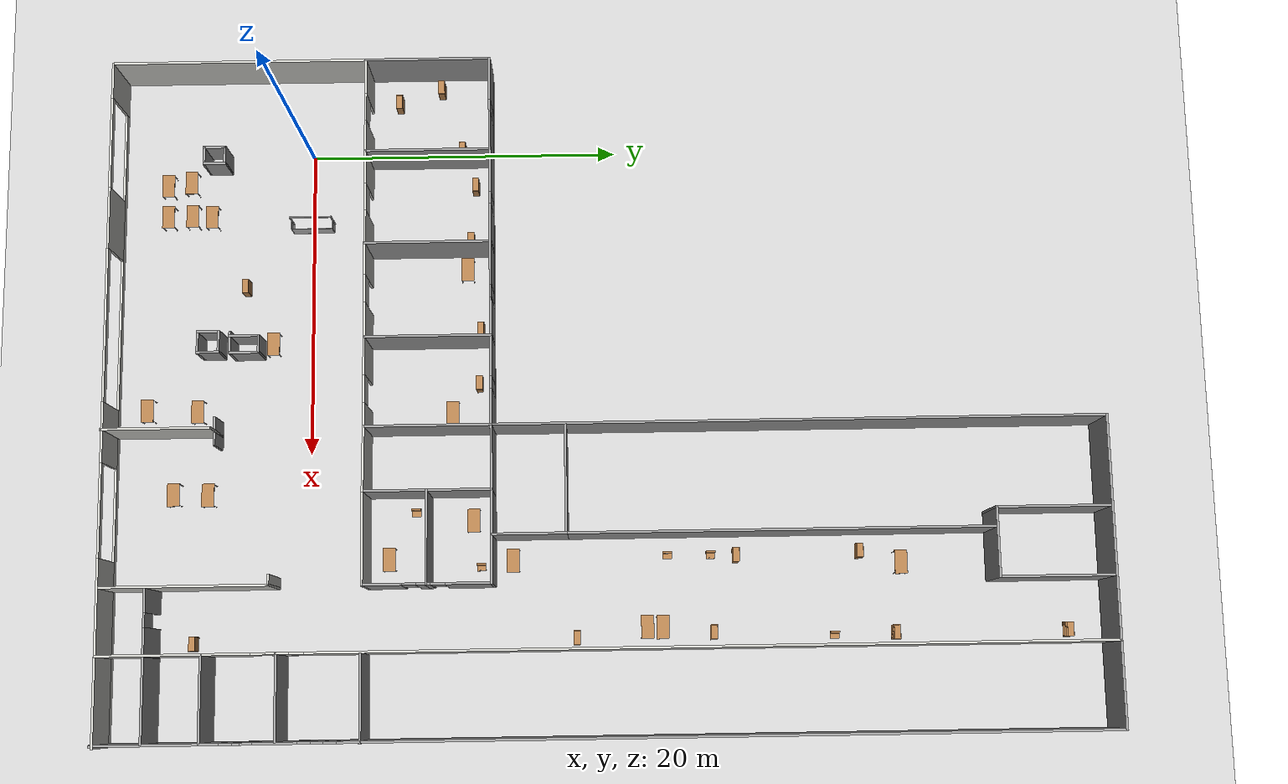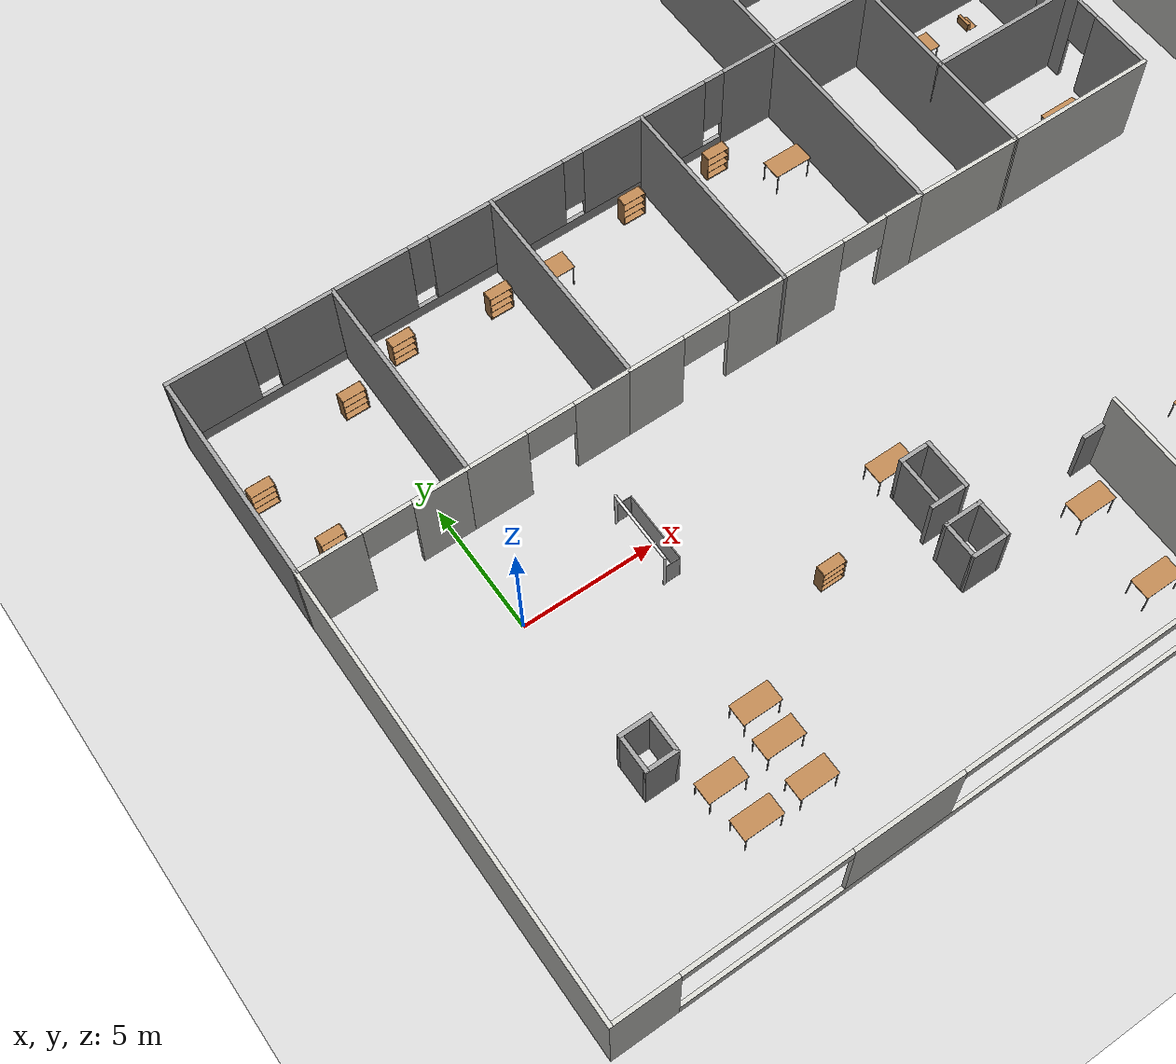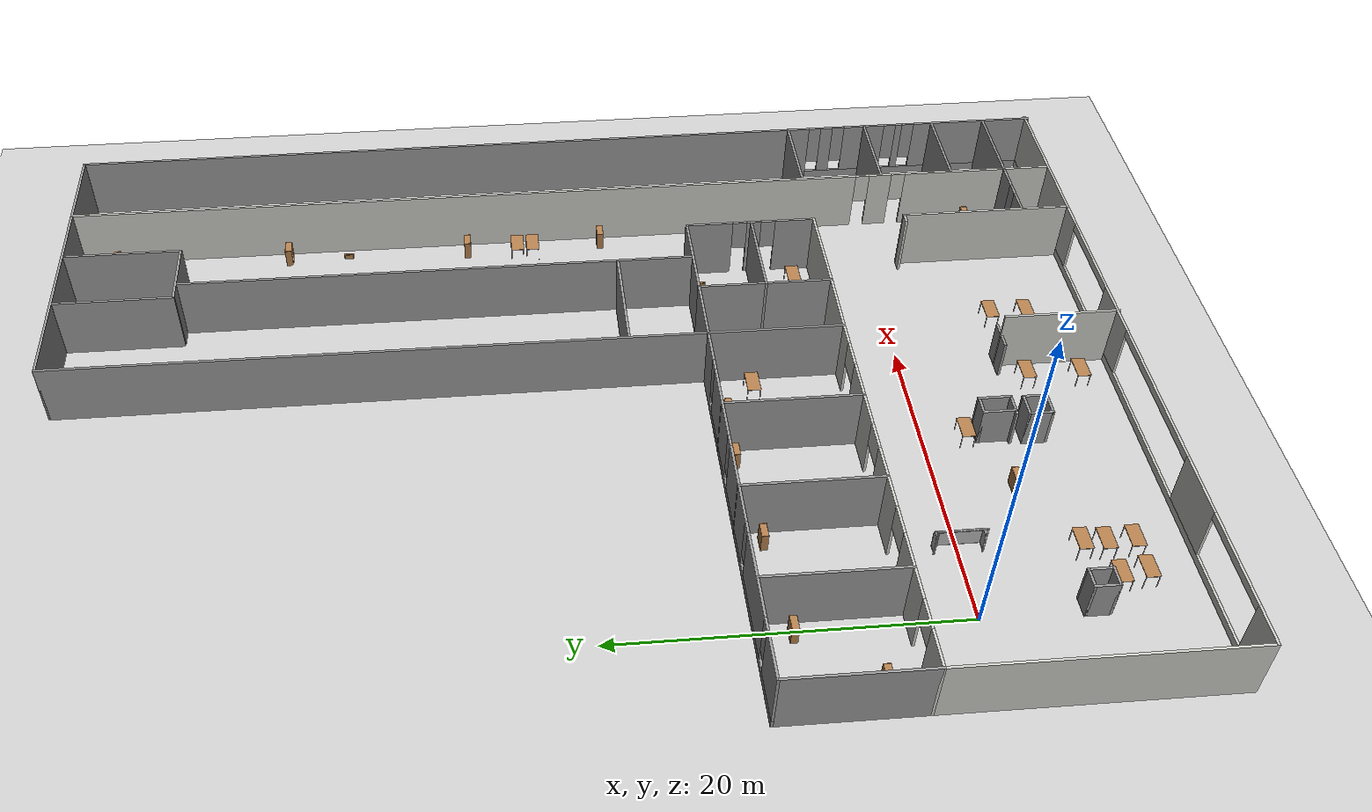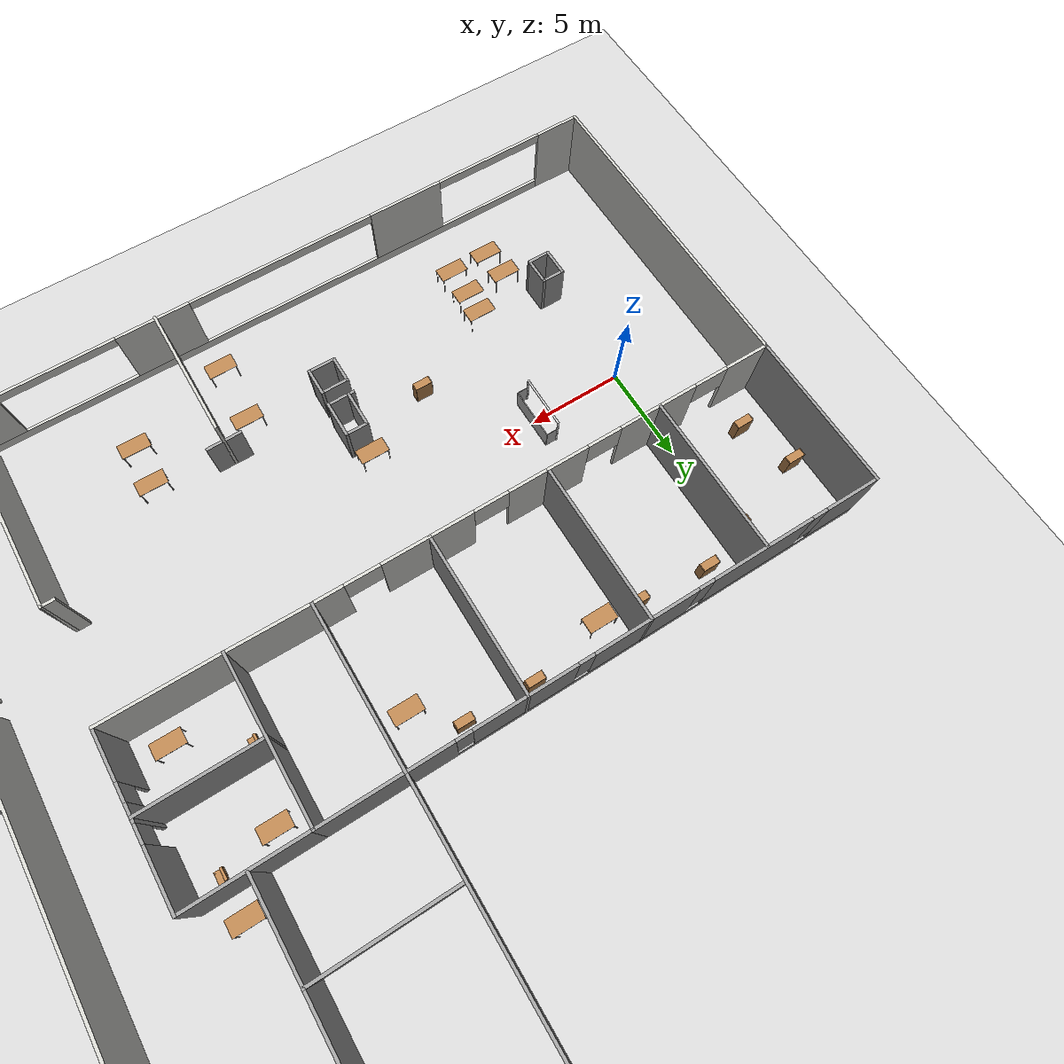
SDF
<sdf version="1.6">
 <world name="default">
  <scene><shadows>0</shadows><ambient>0.4 0.4 0.4 1</ambient><background>0.7 0.7 0.7 1</background></scene>
  <physics name="default_physics" default="0" type="ode">
   <real_time_update_rate>2000</real_time_update_rate>
   <max_step_size>0.0005</max_step_size>
   <ode>
    <solver>
     <type>quick</type>
     <iters>50</iters>
     <sor>1.4</sor>
     <use_dynamic_moi_rescaling>0</use_dynamic_moi_rescaling>
    </solver>
    <constraints>
     <cfm>0</cfm>
     <erp>0.2</erp>
     <contact_max_correcting_vel>100</contact_max_correcting_vel>
     <contact_surface_layer>0</contact_surface_layer>
    </constraints>
   </ode>
   <real_time_factor>1</real_time_factor>
  </physics>
  <model name="ground_plane">
   <static>1</static>
   <link name="link">
    <collision name="collision">
     <geometry><plane><normal>0 0 1</normal><size>100 100</size></plane></geometry>
     <surface><friction><ode><mu>100</mu><mu2>50</mu2></ode></friction></surface>
    </collision>
    <visual name="visual">
     <cast_shadows>0</cast_shadows>
     <geometry><plane><normal>0 0 1</normal><size>100 100</size></plane></geometry>
     <material>
      <script><uri>file://media/materials/scripts/gazebo.material</uri><name>Gazebo/Grey</name></script>
     </material>
    </visual>
   </link>
  </model>
  <model name="teensize_goal">
   <static>1</static>
   <link name="left_post">
    <pose>0 1.35 0.95 0 -0 0</pose>
    <collision name="collision">
     <geometry><cylinder><radius>0.05</radius><length>1.9</length></cylinder></geometry>
    </collision>
    <visual name="visual">
     <geometry><cylinder><radius>0.05</radius><length>1.9</length></cylinder></geometry>
     <material>
      <script><uri>file://media/materials/scripts/gazebo.material</uri><name>Gazebo/White</name></script>
     </material>
    </visual>
   </link>
   <link name="left_support_horiz_lower">
    <pose>0.3 1.35 0.01 0 -0 0</pose>
    <collision name="collision"><geometry><box><size>0.6 0.02 0.02</size></box></geometry></collision>
    <visual name="visual">
     <geometry><box><size>0.6 0.02 0.02</size></box></geometry>
     <material>
      <script><uri>file://media/materials/scripts/gazebo.material</uri><name>Gazebo/White</name></script>
     </material>
    </visual>
   </link>
   <link name="left_support_horiz_upper">
    <pose>0.3 1.35 1.2 0 -0 0</pose>
    <collision name="collision"><geometry><box><size>0.6 0.02 0.02</size></box></geometry></collision>
    <visual name="visual">
     <geometry><box><size>0.6 0.02 0.02</size></box></geometry>
     <material>
      <script><uri>file://media/materials/scripts/gazebo.material</uri><name>Gazebo/White</name></script>
     </material>
    </visual>
   </link>
   <link name="left_support_vertical">
    <pose>0.6 1.35 0.6 3.14159 1.57079 3.14159</pose>
    <collision name="collision"><geometry><box><size>1.2 0.02 0.02</size></box></geometry></collision>
    <visual name="visual">
     <geometry><box><size>1.2 0.02 0.02</size></box></geometry>
     <material>
      <script><uri>file://media/materials/scripts/gazebo.material</uri><name>Gazebo/White</name></script>
     </material>
    </visual>
   </link>
   <link name="right_support_horiz_lower">
    <pose>0.3 -1.35 0.01 0 -0 0</pose>
    <collision name="collision"><geometry><box><size>0.6 0.02 0.02</size></box></geometry></collision>
    <visual name="visual">
     <geometry><box><size>0.6 0.02 0.02</size></box></geometry>
     <material>
      <script><uri>file://media/materials/scripts/gazebo.material</uri><name>Gazebo/White</name></script>
     </material>
    </visual>
   </link>
   <link name="right_support_horiz_upper">
    <pose>0.3 -1.35 1.2 0 -0 0</pose>
    <collision name="collision"><geometry><box><size>0.6 0.02 0.02</size></box></geometry></collision>
    <visual name="visual">
     <geometry><box><size>0.6 0.02 0.02</size></box></geometry>
     <material>
      <script><uri>file://media/materials/scripts/gazebo.material</uri><name>Gazebo/White</name></script>
     </material>
    </visual>
   </link>
   <link name="right_support_vertical">
    <pose>0.6 -1.35 0.6 3.14159 1.57079 3.14159</pose>
    <collision name="collision"><geometry><box><size>1.2 0.02 0.02</size></box></geometry></collision>
    <visual name="visual">
     <geometry><box><size>1.2 0.02 0.02</size></box></geometry>
     <material>
      <script><uri>file://media/materials/scripts/gazebo.material</uri><name>Gazebo/White</name></script>
     </material>
    </visual>
   </link>
   <link name="center_support_horiz_lower">
    <pose>0.6 0 0.01 3.14159 1.57079 3.14159</pose>
    <collision name="collision"><geometry><box><size>0.02 2.7 0.02</size></box></geometry></collision>
    <visual name="visual">
     <geometry><box><size>0.02 2.7 0.02</size></box></geometry>
     <material>
      <script><uri>file://media/materials/scripts/gazebo.material</uri><name>Gazebo/White</name></script>
     </material>
    </visual>
   </link>
   <link name="center_support_horiz_upper">
    <pose>0.6 0 1.2 3.14159 1.57079 3.14159</pose>
    <collision name="collision"><geometry><box><size>0.02 2.7 0.02</size></box></geometry></collision>
    <visual name="visual">
     <geometry><box><size>0.02 2.7 0.02</size></box></geometry>
     <material>
      <script><uri>file://media/materials/scripts/gazebo.material</uri><name>Gazebo/White</name></script>
     </material>
    </visual>
   </link>
   <link name="right_post">
    <pose>0 -1.35 0.95 0 -0 0</pose>
    <collision name="collision">
     <geometry><cylinder><radius>0.05</radius><length>1.9</length></cylinder></geometry>
    </collision>
    <visual name="visual">
     <geometry><cylinder><radius>0.05</radius><length>1.9</length></cylinder></geometry>
     <material>
      <script><uri>file://media/materials/scripts/gazebo.material</uri><name>Gazebo/White</name></script>
     </material>
    </visual>
   </link>
   <link name="crossbar">
    <pose>0 0 1.85 1.57 1.57 0</pose>
    <collision name="collision">
     <geometry><cylinder><radius>0.05</radius><length>2.6</length></cylinder></geometry>
    </collision>
    <visual name="visual">
     <geometry><cylinder><radius>0.05</radius><length>2.6</length></cylinder></geometry>
     <material>
      <script><uri>file://media/materials/scripts/gazebo.material</uri><name>Gazebo/White</name></script>
     </material>
    </visual>
   </link>
   <link name="center_net">
    <pose>0.6 0 0.6 0 -0 0</pose>
    <collision name="collision"><geometry><box><size>0.01 2.7 1.2</size></box></geometry></collision>
    <visual name="visual">
     <geometry><box><size>0.01 2.7 1.2</size></box></geometry>
     <material>
      <script>
       <uri>model://teensize_goal/materials/scripts/</uri>
       <uri>model://teensize_goal/materials/textures/</uri>
       <name>RoboCup/Net</name>
      </script>
     </material>
    </visual>
   </link>
   <link name="left_net">
    <pose>0.3 1.35 0.6 0 -0 0</pose>
    <collision name="collision"><geometry><box><size>0.6 0.01 1.2</size></box></geometry></collision>
    <visual name="visual">
     <geometry><box><size>0.6 0.01 1.2</size></box></geometry>
     <material>
      <script>
       <uri>model://teensize_goal/materials/scripts/</uri>
       <uri>model://teensize_goal/materials/textures/</uri>
       <name>RoboCup/Net</name>
      </script>
     </material>
    </visual>
   </link>
   <link name="right_net">
    <pose>0.3 -1.35 0.6 0 -0 0</pose>
    <collision name="collision"><geometry><box><size>0.6 0.01 1.2</size></box></geometry></collision>
    <visual name="visual">
     <geometry><box><size>0.6 0.01 1.2</size></box></geometry>
     <material>
      <script>
       <uri>model://teensize_goal/materials/scripts/</uri>
       <uri>model://teensize_goal/materials/textures/</uri>
       <name>RoboCup/Net</name>
      </script>
     </material>
    </visual>
   </link>
   <pose>4.525 0 0 0 -0 0</pose>
  </model>
  <model name="teensize_goal">
   <static>1</static>
   <link name="left_post">
    <pose>0 1.35 0.95 0 -0 0</pose>
    <collision name="collision">
     <geometry><cylinder><radius>0.05</radius><length>1.9</length></cylinder></geometry>
    </collision>
    <visual name="visual">
     <geometry><cylinder><radius>0.05</radius><length>1.9</length></cylinder></geometry>
     <material>
      <script><uri>file://media/materials/scripts/gazebo.material</uri><name>Gazebo/White</name></script>
     </material>
    </visual>
   </link>
   <link name="left_support_horiz_lower">
    <pose>0.3 1.35 0.01 0 -0 0</pose>
    <collision name="collision"><geometry><box><size>0.6 0.02 0.02</size></box></geometry></collision>
    <visual name="visual">
     <geometry><box><size>0.6 0.02 0.02</size></box></geometry>
     <material>
      <script><uri>file://media/materials/scripts/gazebo.material</uri><name>Gazebo/White</name></script>
     </material>
    </visual>
   </link>
   <link name="left_support_horiz_upper">
    <pose>0.3 1.35 1.2 0 -0 0</pose>
    <collision name="collision"><geometry><box><size>0.6 0.02 0.02</size></box></geometry></collision>
    <visual name="visual">
     <geometry><box><size>0.6 0.02 0.02</size></box></geometry>
     <material>
      <script><uri>file://media/materials/scripts/gazebo.material</uri><name>Gazebo/White</name></script>
     </material>
    </visual>
   </link>
   <link name="left_support_vertical">
    <pose>0.6 1.35 0.6 3.14159 1.57079 3.14159</pose>
    <collision name="collision"><geometry><box><size>1.2 0.02 0.02</size></box></geometry></collision>
    <visual name="visual">
     <geometry><box><size>1.2 0.02 0.02</size></box></geometry>
     <material>
      <script><uri>file://media/materials/scripts/gazebo.material</uri><name>Gazebo/White</name></script>
     </material>
    </visual>
   </link>
   <link name="right_support_horiz_lower">
    <pose>0.3 -1.35 0.01 0 -0 0</pose>
    <collision name="collision"><geometry><box><size>0.6 0.02 0.02</size></box></geometry></collision>
    <visual name="visual">
     <geometry><box><size>0.6 0.02 0.02</size></box></geometry>
     <material>
      <script><uri>file://media/materials/scripts/gazebo.material</uri><name>Gazebo/White</name></script>
     </material>
    </visual>
   </link>
   <link name="right_support_horiz_upper">
    <pose>0.3 -1.35 1.2 0 -0 0</pose>
    <collision name="collision"><geometry><box><size>0.6 0.02 0.02</size></box></geometry></collision>
    <visual name="visual">
     <geometry><box><size>0.6 0.02 0.02</size></box></geometry>
     <material>
      <script><uri>file://media/materials/scripts/gazebo.material</uri><name>Gazebo/White</name></script>
     </material>
    </visual>
   </link>
   <link name="right_support_vertical">
    <pose>0.6 -1.35 0.6 3.14159 1.57079 3.14159</pose>
    <collision name="collision"><geometry><box><size>1.2 0.02 0.02</size></box></geometry></collision>
    <visual name="visual">
     <geometry><box><size>1.2 0.02 0.02</size></box></geometry>
     <material>
      <script><uri>file://media/materials/scripts/gazebo.material</uri><name>Gazebo/White</name></script>
     </material>
    </visual>
   </link>
   <link name="center_support_horiz_lower">
    <pose>0.6 0 0.01 3.14159 1.57079 3.14159</pose>
    <collision name="collision"><geometry><box><size>0.02 2.7 0.02</size></box></geometry></collision>
    <visual name="visual">
     <geometry><box><size>0.02 2.7 0.02</size></box></geometry>
     <material>
      <script><uri>file://media/materials/scripts/gazebo.material</uri><name>Gazebo/White</name></script>
     </material>
    </visual>
   </link>
   <link name="center_support_horiz_upper">
    <pose>0.6 0 1.2 3.14159 1.57079 3.14159</pose>
    <collision name="collision"><geometry><box><size>0.02 2.7 0.02</size></box></geometry></collision>
    <visual name="visual">
     <geometry><box><size>0.02 2.7 0.02</size></box></geometry>
     <material>
      <script><uri>file://media/materials/scripts/gazebo.material</uri><name>Gazebo/White</name></script>
     </material>
    </visual>
   </link>
   <link name="right_post">
    <pose>0 -1.35 0.95 0 -0 0</pose>
    <collision name="collision">
     <geometry><cylinder><radius>0.05</radius><length>1.9</length></cylinder></geometry>
    </collision>
    <visual name="visual">
     <geometry><cylinder><radius>0.05</radius><length>1.9</length></cylinder></geometry>
     <material>
      <script><uri>file://media/materials/scripts/gazebo.material</uri><name>Gazebo/White</name></script>
     </material>
    </visual>
   </link>
   <link name="crossbar">
    <pose>0 0 1.85 1.57 1.57 0</pose>
    <collision name="collision">
     <geometry><cylinder><radius>0.05</radius><length>2.6</length></cylinder></geometry>
    </collision>
    <visual name="visual">
     <geometry><cylinder><radius>0.05</radius><length>2.6</length></cylinder></geometry>
     <material>
      <script><uri>file://media/materials/scripts/gazebo.material</uri><name>Gazebo/White</name></script>
     </material>
    </visual>
   </link>
   <link name="center_net">
    <pose>0.6 0 0.6 0 -0 0</pose>
    <collision name="collision"><geometry><box><size>0.01 2.7 1.2</size></box></geometry></collision>
    <visual name="visual">
     <geometry><box><size>0.01 2.7 1.2</size></box></geometry>
     <material>
      <script>
       <uri>model://teensize_goal/materials/scripts/</uri>
       <uri>model://teensize_goal/materials/textures/</uri>
       <name>RoboCup/Net</name>
      </script>
     </material>
    </visual>
   </link>
   <link name="left_net">
    <pose>0.3 1.35 0.6 0 -0 0</pose>
    <collision name="collision"><geometry><box><size>0.6 0.01 1.2</size></box></geometry></collision>
    <visual name="visual">
     <geometry><box><size>0.6 0.01 1.2</size></box></geometry>
     <material>
      <script>
       <uri>model://teensize_goal/materials/scripts/</uri>
       <uri>model://teensize_goal/materials/textures/</uri>
       <name>RoboCup/Net</name>
      </script>
     </material>
    </visual>
   </link>
   <link name="right_net">
    <pose>0.3 -1.35 0.6 0 -0 0</pose>
    <collision name="collision"><geometry><box><size>0.6 0.01 1.2</size></box></geometry></collision>
    <visual name="visual">
     <geometry><box><size>0.6 0.01 1.2</size></box></geometry>
     <material>
      <script>
       <uri>model://teensize_goal/materials/scripts/</uri>
       <uri>model://teensize_goal/materials/textures/</uri>
       <name>RoboCup/Net</name>
      </script>
     </material>
    </visual>
   </link>
   <pose>4.525 0 0 0 -0 0</pose>
  </model>
  <model name="zjwall">
   <pose>16.5 19.0001 0 0 0 -1.5708</pose>
   <link name="Wall_0">
    <pose>0.0005 21.815 0 0 -0 0</pose>
    <visual name="Wall_0_Visual_0">
     <pose>-7.59115 0 2 0 -0 0</pose>
     <geometry><box><size>48.4977 0.15 4</size></box></geometry>
     <material>
      <script><uri>file://media/materials/scripts/gazebo.material</uri><name>Gazebo/Grey</name></script>
      <ambient>1 1 1 1</ambient>
     </material>
     <meta><layer>0</layer></meta>
    </visual>
    <collision name="Wall_0_Collision_0">
     <geometry><box><size>48.4977 0.15 4</size></box></geometry>
     <pose>-7.59115 0 2 0 -0 0</pose>
    </collision>
    <visual name="Wall_0_Visual_1">
     <pose>24.2489 0 0.25 0 -0 0</pose>
     <geometry><box><size>15.1823 0.15 0.5</size></box></geometry>
     <material>
      <script><uri>file://media/materials/scripts/gazebo.material</uri><name>Gazebo/Grey</name></script>
      <ambient>1 1 1 1</ambient>
     </material>
     <meta><layer>0</layer></meta>
    </visual>
    <collision name="Wall_0_Collision_1">
     <geometry><box><size>15.1823 0.15 0.5</size></box></geometry>
     <pose>24.2489 0 0.25 0 -0 0</pose>
    </collision>
    <visual name="Wall_0_Visual_2">
     <pose>17.8571 0 2.25 0 -0 0</pose>
     <geometry><box><size>0.798874 0.15 3.5</size></box></geometry>
     <material>
      <script><uri>file://media/materials/scripts/gazebo.material</uri><name>Gazebo/Grey</name></script>
      <ambient>1 1 1 1</ambient>
     </material>
     <meta><layer>0</layer></meta>
    </visual>
    <collision name="Wall_0_Collision_2">
     <geometry><box><size>0.798874 0.15 3.5</size></box></geometry>
     <pose>17.8571 0 2.25 0 -0 0</pose>
    </collision>
    <visual name="Wall_0_Visual_3">
     <pose>20.4331 0 2.25 0 -0 0</pose>
     <geometry><box><size>2.75305 0.15 3.5</size></box></geometry>
     <material>
      <script><uri>file://media/materials/scripts/gazebo.material</uri><name>Gazebo/Grey</name></script>
      <ambient>1 1 1 1</ambient>
     </material>
     <meta><layer>0</layer></meta>
    </visual>
    <collision name="Wall_0_Collision_3">
     <geometry><box><size>2.75305 0.15 3.5</size></box></geometry>
     <pose>20.4331 0 2.25 0 -0 0</pose>
    </collision>
    <visual name="Wall_0_Visual_4">
     <pose>22.8314 0 2.25 0 -0 0</pose>
     <geometry><box><size>0.443569 0.15 3.5</size></box></geometry>
     <material>
      <script><uri>file://media/materials/scripts/gazebo.material</uri><name>Gazebo/Grey</name></script>
      <ambient>1 1 1 1</ambient>
     </material>
     <meta><layer>0</layer></meta>
    </visual>
    <collision name="Wall_0_Collision_4">
     <geometry><box><size>0.443569 0.15 3.5</size></box></geometry>
     <pose>22.8314 0 2.25 0 -0 0</pose>
    </collision>
    <visual name="Wall_0_Visual_5">
     <pose>27.8466 0 2.25 0 -0 0</pose>
     <geometry><box><size>7.9868 0.15 3.5</size></box></geometry>
     <material>
      <script><uri>file://media/materials/scripts/gazebo.material</uri><name>Gazebo/Grey</name></script>
      <ambient>1 1 1 1</ambient>
     </material>
     <meta><layer>0</layer></meta>
    </visual>
    <collision name="Wall_0_Collision_5">
     <geometry><box><size>7.9868 0.15 3.5</size></box></geometry>
     <pose>27.8466 0 2.25 0 -0 0</pose>
    </collision>
    <visual name="Wall_0_Visual_6">
     <pose>17.0577 0 2.65 0 -0 0</pose>
     <geometry><box><size>0.8 0.15 2.7</size></box></geometry>
     <material>
      <script><uri>file://media/materials/scripts/gazebo.material</uri><name>Gazebo/Grey</name></script>
      <ambient>1 1 1 1</ambient>
     </material>
     <meta><layer>0</layer></meta>
    </visual>
    <collision name="Wall_0_Collision_6">
     <geometry><box><size>0.8 0.15 2.7</size></box></geometry>
     <pose>17.0577 0 2.65 0 -0 0</pose>
    </collision>
    <visual name="Wall_0_Visual_7">
     <pose>18.6566 0 2.65 0 -0 0</pose>
     <geometry><box><size>0.8 0.15 2.7</size></box></geometry>
     <material>
      <script><uri>file://media/materials/scripts/gazebo.material</uri><name>Gazebo/Grey</name></script>
      <ambient>1 1 1 1</ambient>
     </material>
     <meta><layer>0</layer></meta>
    </visual>
    <collision name="Wall_0_Collision_7">
     <geometry><box><size>0.8 0.15 2.7</size></box></geometry>
     <pose>18.6566 0 2.65 0 -0 0</pose>
    </collision>
    <visual name="Wall_0_Visual_8">
     <pose>22.2096 0 2.65 0 -0 0</pose>
     <geometry><box><size>0.8 0.15 2.7</size></box></geometry>
     <material>
      <script><uri>file://media/materials/scripts/gazebo.material</uri><name>Gazebo/Grey</name></script>
      <ambient>1 1 1 1</ambient>
     </material>
     <meta><layer>0</layer></meta>
    </visual>
    <collision name="Wall_0_Collision_8">
     <geometry><box><size>0.8 0.15 2.7</size></box></geometry>
     <pose>22.2096 0 2.65 0 -0 0</pose>
    </collision>
    <visual name="Wall_0_Visual_9">
     <pose>23.4532 0 2.65 0 -0 0</pose>
     <geometry><box><size>0.8 0.15 2.7</size></box></geometry>
     <material>
      <script><uri>file://media/materials/scripts/gazebo.material</uri><name>Gazebo/Grey</name></script>
      <ambient>1 1 1 1</ambient>
     </material>
     <meta><layer>0</layer></meta>
    </visual>
    <collision name="Wall_0_Collision_9">
     <geometry><box><size>0.8 0.15 2.7</size></box></geometry>
     <pose>23.4532 0 2.65 0 -0 0</pose>
    </collision>
   </link>
   <link name="Wall_104">
    <collision name="Wall_104_Collision">
     <geometry><box><size>1.5 0.15 2.5</size></box></geometry>
     <pose>0 0 1.25 0 -0 0</pose>
    </collision>
    <visual name="Wall_104_Visual">
     <pose>0 0 1.25 0 -0 0</pose>
     <geometry><box><size>1.5 0.15 2.5</size></box></geometry>
     <material>
      <script><uri>file://media/materials/scripts/gazebo.material</uri><name>Gazebo/Grey</name></script>
      <ambient>1 1 1 1</ambient>
     </material>
     <meta><layer>0</layer></meta>
    </visual>
    <pose>23.9911 -3.55705 0 0 -0 1.5708</pose>
   </link>
   <link name="Wall_105">
    <collision name="Wall_105_Collision">
     <geometry><box><size>2 0.15 2.5</size></box></geometry>
     <pose>0 0 1.25 0 -0 0</pose>
    </collision>
    <visual name="Wall_105_Visual">
     <pose>0 0 1.25 0 -0 0</pose>
     <geometry><box><size>2 0.15 2.5</size></box></geometry>
     <material>
      <script><uri>file://media/materials/scripts/gazebo.material</uri><name>Gazebo/Grey</name></script>
      <ambient>1 1 1 1</ambient>
     </material>
     <meta><layer>0</layer></meta>
    </visual>
    <pose>23.0661 -2.88205 0 0 -0 3.14159</pose>
   </link>
   <link name="Wall_107">
    <collision name="Wall_107_Collision">
     <geometry><box><size>1.25 0.15 2.5</size></box></geometry>
     <pose>0 0 1.25 0 -0 0</pose>
    </collision>
    <visual name="Wall_107_Visual">
     <pose>0 0 1.25 0 -0 0</pose>
     <geometry><box><size>1.25 0.15 2.5</size></box></geometry>
     <material>
      <script><uri>file://media/materials/scripts/gazebo.material</uri><name>Gazebo/Grey</name></script>
      <ambient>1 1 1 1</ambient>
     </material>
     <meta><layer>0</layer></meta>
    </visual>
    <pose>22.1411 -3.43205 0 0 -0 -1.5708</pose>
   </link>
   <link name="Wall_108">
    <collision name="Wall_108_Collision">
     <geometry><box><size>2 0.15 2.5</size></box></geometry>
     <pose>0 0 1.25 0 -0 0</pose>
    </collision>
    <visual name="Wall_108_Visual">
     <pose>0 0 1.25 0 -0 0</pose>
     <geometry><box><size>2 0.15 2.5</size></box></geometry>
     <material>
      <script><uri>file://media/materials/scripts/gazebo.material</uri><name>Gazebo/Grey</name></script>
      <ambient>1 1 1 1</ambient>
     </material>
     <meta><layer>0</layer></meta>
    </visual>
    <pose>23.0661 -3.98205 0 0 -0 0</pose>
   </link>
   <link name="Wall_11">
    <pose>31.6155 0 0 0 -0 1.5708</pose>
    <visual name="Wall_11_Visual_0">
     <pose>-20.7907 0 2 0 -0 0</pose>
     <geometry><box><size>2.41853 0.15 4</size></box></geometry>
     <material>
      <script><uri>file://media/materials/scripts/gazebo.material</uri><name>Gazebo/CeilingTiled</name></script>
      <ambient>1 1 1 1</ambient>
     </material>
     <meta><layer>0</layer></meta>
    </visual>
    <collision name="Wall_11_Collision_0">
     <geometry><box><size>2.41853 0.15 4</size></box></geometry>
     <pose>-20.7907 0 2 0 -0 0</pose>
    </collision>
    <visual name="Wall_11_Visual_1">
     <pose>1.20926 0 0.25 0 -0 0</pose>
     <geometry><box><size>41.5815 0.15 0.5</size></box></geometry>
     <material>
      <script><uri>file://media/materials/scripts/gazebo.material</uri><name>Gazebo/CeilingTiled</name></script>
      <ambient>1 1 1 1</ambient>
     </material>
     <meta><layer>0</layer></meta>
    </visual>
    <collision name="Wall_11_Collision_1">
     <geometry><box><size>41.5815 0.15 0.5</size></box></geometry>
     <pose>1.20926 0 0.25 0 -0 0</pose>
    </collision>
    <visual name="Wall_11_Visual_2">
     <pose>-11.559 0 2.25 0 -0 0</pose>
     <geometry><box><size>4.04501 0.15 3.5</size></box></geometry>
     <material>
      <script><uri>file://media/materials/scripts/gazebo.material</uri><name>Gazebo/CeilingTiled</name></script>
      <ambient>1 1 1 1</ambient>
     </material>
     <meta><layer>0</layer></meta>
    </visual>
    <collision name="Wall_11_Collision_2">
     <geometry><box><size>4.04501 0.15 3.5</size></box></geometry>
     <pose>-11.559 0 2.25 0 -0 0</pose>
    </collision>
    <visual name="Wall_11_Visual_3">
     <pose>2.39649 0 2.25 0 -0 0</pose>
     <geometry><box><size>3.8659 0.15 3.5</size></box></geometry>
     <material>
      <script><uri>file://media/materials/scripts/gazebo.material</uri><name>Gazebo/CeilingTiled</name></script>
      <ambient>1 1 1 1</ambient>
     </material>
     <meta><layer>0</layer></meta>
    </visual>
    <collision name="Wall_11_Collision_3">
     <geometry><box><size>3.8659 0.15 3.5</size></box></geometry>
     <pose>2.39649 0 2.25 0 -0 0</pose>
    </collision>
    <visual name="Wall_11_Visual_4">
     <pose>16.1647 0 2.25 0 -0 0</pose>
     <geometry><box><size>11.6706 0.15 3.5</size></box></geometry>
     <material>
      <script><uri>file://media/materials/scripts/gazebo.material</uri><name>Gazebo/CeilingTiled</name></script>
      <ambient>1 1 1 1</ambient>
     </material>
     <meta><layer>0</layer></meta>
    </visual>
    <collision name="Wall_11_Collision_4">
     <geometry><box><size>11.6706 0.15 3.5</size></box></geometry>
     <pose>16.1647 0 2.25 0 -0 0</pose>
    </collision>
    <visual name="Wall_11_Visual_5">
     <pose>-16.5815 0 3.75 0 -0 0</pose>
     <geometry><box><size>6 0.15 0.5</size></box></geometry>
     <material>
      <script><uri>file://media/materials/scripts/gazebo.material</uri><name>Gazebo/CeilingTiled</name></script>
      <ambient>1 1 1 1</ambient>
     </material>
     <meta><layer>0</layer></meta>
    </visual>
    <collision name="Wall_11_Collision_5">
     <geometry><box><size>6 0.15 0.5</size></box></geometry>
     <pose>-16.5815 0 3.75 0 -0 0</pose>
    </collision>
    <visual name="Wall_11_Visual_6">
     <pose>-4.53646 0 3.75 0 -0 0</pose>
     <geometry><box><size>10 0.15 0.5</size></box></geometry>
     <material>
      <script><uri>file://media/materials/scripts/gazebo.material</uri><name>Gazebo/CeilingTiled</name></script>
      <ambient>1 1 1 1</ambient>
     </material>
     <meta><layer>0</layer></meta>
    </visual>
    <collision name="Wall_11_Collision_6">
     <geometry><box><size>10 0.15 0.5</size></box></geometry>
     <pose>-4.53646 0 3.75 0 -0 0</pose>
    </collision>
    <visual name="Wall_11_Visual_7">
     <pose>7.32944 0 3.75 0 -0 0</pose>
     <geometry><box><size>6 0.15 0.5</size></box></geometry>
     <material>
      <script><uri>file://media/materials/scripts/gazebo.material</uri><name>Gazebo/CeilingTiled</name></script>
      <ambient>1 1 1 1</ambient>
     </material>
     <meta><layer>0</layer></meta>
    </visual>
    <collision name="Wall_11_Collision_7">
     <geometry><box><size>6 0.15 0.5</size></box></geometry>
     <pose>7.32944 0 3.75 0 -0 0</pose>
    </collision>
   </link>
   <link name="Wall_110">
    <collision name="Wall_110_Collision">
     <geometry><box><size>1.25 0.15 2.5</size></box></geometry>
     <pose>0 0 1.25 0 -0 0</pose>
    </collision>
    <visual name="Wall_110_Visual">
     <pose>0 0 1.25 0 -0 0</pose>
     <geometry><box><size>1.25 0.15 2.5</size></box></geometry>
     <material>
      <script><uri>file://media/materials/scripts/gazebo.material</uri><name>Gazebo/Grey</name></script>
      <ambient>1 1 1 1</ambient>
     </material>
     <meta><layer>0</layer></meta>
    </visual>
    <pose>24.5599 -16.0944 0 0 -0 -1.5708</pose>
   </link>
   <link name="Wall_111">
    <collision name="Wall_111_Collision">
     <geometry><box><size>1.5 0.15 2.5</size></box></geometry>
     <pose>0 0 1.25 0 -0 0</pose>
    </collision>
    <visual name="Wall_111_Visual">
     <pose>0 0 1.25 0 -0 0</pose>
     <geometry><box><size>1.5 0.15 2.5</size></box></geometry>
     <material>
      <script><uri>file://media/materials/scripts/gazebo.material</uri><name>Gazebo/Grey</name></script>
      <ambient>1 1 1 1</ambient>
     </material>
     <meta><layer>0</layer></meta>
    </visual>
    <pose>25.2349 -16.6444 0 0 -0 0</pose>
   </link>
   <link name="Wall_112">
    <collision name="Wall_112_Collision">
     <geometry><box><size>1.25 0.15 2.5</size></box></geometry>
     <pose>0 0 1.25 0 -0 0</pose>
    </collision>
    <visual name="Wall_112_Visual">
     <pose>0 0 1.25 0 -0 0</pose>
     <geometry><box><size>1.25 0.15 2.5</size></box></geometry>
     <material>
      <script><uri>file://media/materials/scripts/gazebo.material</uri><name>Gazebo/Grey</name></script>
      <ambient>1 1 1 1</ambient>
     </material>
     <meta><layer>0</layer></meta>
    </visual>
    <pose>25.9099 -16.0944 0 0 -0 1.5708</pose>
   </link>
   <link name="Wall_115">
    <collision name="Wall_115_Collision">
     <geometry><box><size>1.5 0.15 2.5</size></box></geometry>
     <pose>0 0 1.25 0 -0 0</pose>
    </collision>
    <visual name="Wall_115_Visual">
     <pose>0 0 1.25 0 -0 0</pose>
     <geometry><box><size>1.5 0.15 2.5</size></box></geometry>
     <material>
      <script><uri>file://media/materials/scripts/gazebo.material</uri><name>Gazebo/Grey</name></script>
      <ambient>1 1 1 1</ambient>
     </material>
     <meta><layer>0</layer></meta>
    </visual>
    <pose>25.2349 -15.5444 0 0 -0 3.14159</pose>
   </link>
   <link name="Wall_117">
    <collision name="Wall_117_Collision">
     <geometry><box><size>1.5 0.15 2.5</size></box></geometry>
     <pose>0 0 1.25 0 -0 0</pose>
    </collision>
    <visual name="Wall_117_Visual">
     <pose>0 0 1.25 0 -0 0</pose>
     <geometry><box><size>1.5 0.15 2.5</size></box></geometry>
     <material>
      <script><uri>file://media/materials/scripts/gazebo.material</uri><name>Gazebo/Grey</name></script>
      <ambient>1 1 1 1</ambient>
     </material>
     <meta><layer>0</layer></meta>
    </visual>
    <pose>24.7261 -3.61102 0 0 -0 -1.5708</pose>
   </link>
   <link name="Wall_118">
    <collision name="Wall_118_Collision">
     <geometry><box><size>1.5 0.15 2.5</size></box></geometry>
     <pose>0 0 1.25 0 -0 0</pose>
    </collision>
    <visual name="Wall_118_Visual">
     <pose>0 0 1.25 0 -0 0</pose>
     <geometry><box><size>1.5 0.15 2.5</size></box></geometry>
     <material>
      <script><uri>file://media/materials/scripts/gazebo.material</uri><name>Gazebo/Grey</name></script>
      <ambient>1 1 1 1</ambient>
     </material>
     <meta><layer>0</layer></meta>
    </visual>
    <pose>25.4011 -4.28602 0 0 -0 0</pose>
   </link>
   <link name="Wall_119">
    <collision name="Wall_119_Collision">
     <geometry><box><size>1.5 0.15 2.5</size></box></geometry>
     <pose>0 0 1.25 0 -0 0</pose>
    </collision>
    <visual name="Wall_119_Visual">
     <pose>0 0 1.25 0 -0 0</pose>
     <geometry><box><size>1.5 0.15 2.5</size></box></geometry>
     <material>
      <script><uri>file://media/materials/scripts/gazebo.material</uri><name>Gazebo/Grey</name></script>
      <ambient>1 1 1 1</ambient>
     </material>
     <meta><layer>0</layer></meta>
    </visual>
    <pose>26.0761 -3.61102 0 0 -0 1.5708</pose>
   </link>
   <link name="Wall_120">
    <collision name="Wall_120_Collision">
     <geometry><box><size>1.5 0.15 2.5</size></box></geometry>
     <pose>0 0 1.25 0 -0 0</pose>
    </collision>
    <visual name="Wall_120_Visual">
     <pose>0 0 1.25 0 -0 0</pose>
     <geometry><box><size>1.5 0.15 2.5</size></box></geometry>
     <material>
      <script><uri>file://media/materials/scripts/gazebo.material</uri><name>Gazebo/Grey</name></script>
      <ambient>1 1 1 1</ambient>
     </material>
     <meta><layer>0</layer></meta>
    </visual>
    <pose>25.4011 -2.93602 0 0 -0 3.14159</pose>
   </link>
   <link name="Wall_122">
    <collision name="Wall_122_Collision">
     <geometry><box><size>1 0.15 2.5</size></box></geometry>
     <pose>0 0 1.25 0 -0 0</pose>
    </collision>
    <visual name="Wall_122_Visual">
     <pose>0 0 1.25 0 -0 0</pose>
     <geometry><box><size>1 0.15 2.5</size></box></geometry>
     <material>
      <script><uri>file://media/materials/scripts/gazebo.material</uri><name>Gazebo/Grey</name></script>
      <ambient>1 1 1 1</ambient>
     </material>
     <meta><layer>0</layer></meta>
    </visual>
    <pose>24.8575 2.641 0 0 -0 1.5708</pose>
   </link>
   <link name="Wall_124">
    <collision name="Wall_124_Collision">
     <geometry><box><size>1 0.15 2.5</size></box></geometry>
     <pose>0 0 1.25 0 -0 0</pose>
    </collision>
    <visual name="Wall_124_Visual">
     <pose>0 0 1.25 0 -0 0</pose>
     <geometry><box><size>1 0.15 2.5</size></box></geometry>
     <material>
      <script><uri>file://media/materials/scripts/gazebo.material</uri><name>Gazebo/Grey</name></script>
      <ambient>1 1 1 1</ambient>
     </material>
     <meta><layer>0</layer></meta>
    </visual>
    <pose>24.8575 1.791 0 0 -0 -1.5708</pose>
   </link>
   <link name="Wall_19">
    <collision name="Wall_19_Collision">
     <geometry><box><size>8.2 0.15 4</size></box></geometry>
     <pose>0 0 2 0 -0 0</pose>
    </collision>
    <visual name="Wall_19_Visual">
     <pose>0 0 2 0 -0 0</pose>
     <geometry><box><size>8.2 0.15 4</size></box></geometry>
     <material>
      <script><uri>file://media/materials/scripts/gazebo.material</uri><name>Gazebo/Grey</name></script>
      <ambient>1 1 1 1</ambient>
     </material>
     <meta><layer>0</layer></meta>
    </visual>
    <pose>11.1105 -21.925 0 0 -0 0</pose>
   </link>
   <link name="Wall_2">
    <collision name="Wall_2_Collision">
     <geometry><box><size>19.68 0.15 4</size></box></geometry>
     <pose>0 0 2 0 -0 0</pose>
    </collision>
    <visual name="Wall_2_Visual">
     <pose>0 0 2 0 -0 0</pose>
     <geometry><box><size>19.68 0.15 4</size></box></geometry>
     <material>
      <script><uri>file://media/materials/scripts/gazebo.material</uri><name>Gazebo/Grey</name></script>
      <ambient>1 1 1 1</ambient>
     </material>
     <meta><layer>0</layer></meta>
    </visual>
    <pose>-31.7645 12.05 0 0 -0 -1.5708</pose>
   </link>
   <link name="Wall_22">
    <pose>15.1355 -18.85 0 0 -0 1.5708</pose>
    <visual name="Wall_22_Visual_0">
     <pose>-1.95853 0 2 0 -0 0</pose>
     <geometry><box><size>2.38295 0.15 4</size></box></geometry>
     <material>
      <script><uri>file://media/materials/scripts/gazebo.material</uri><name>Gazebo/CeilingTiled</name></script>
      <ambient>1 1 1 1</ambient>
     </material>
     <meta><layer>0</layer></meta>
    </visual>
    <collision name="Wall_22_Collision_0">
     <geometry><box><size>2.38295 0.15 4</size></box></geometry>
     <pose>-1.95853 0 2 0 -0 0</pose>
    </collision>
    <visual name="Wall_22_Visual_1">
     <pose>2.09147 0 2 0 -0 0</pose>
     <geometry><box><size>2.11705 0.15 4</size></box></geometry>
     <material>
      <script><uri>file://media/materials/scripts/gazebo.material</uri><name>Gazebo/CeilingTiled</name></script>
      <ambient>1 1 1 1</ambient>
     </material>
     <meta><layer>0</layer></meta>
    </visual>
    <collision name="Wall_22_Collision_1">
     <geometry><box><size>2.11705 0.15 4</size></box></geometry>
     <pose>2.09147 0 2 0 -0 0</pose>
    </collision>
    <visual name="Wall_22_Visual_2">
     <pose>0.132951 0 3.15 0 -0 0</pose>
     <geometry><box><size>1.8 0.15 1.7</size></box></geometry>
     <material>
      <script><uri>file://media/materials/scripts/gazebo.material</uri><name>Gazebo/CeilingTiled</name></script>
      <ambient>1 1 1 1</ambient>
     </material>
     <meta><layer>0</layer></meta>
    </visual>
    <collision name="Wall_22_Collision_2">
     <geometry><box><size>1.8 0.15 1.7</size></box></geometry>
     <pose>0.132951 0 3.15 0 -0 0</pose>
    </collision>
   </link>
   <link name="Wall_24">
    <collision name="Wall_24_Collision">
     <geometry><box><size>8.2 0.15 4</size></box></geometry>
     <pose>0 0 2 0 -0 0</pose>
    </collision>
    <visual name="Wall_24_Visual">
     <pose>0 0 2 0 -0 0</pose>
     <geometry><box><size>8.2 0.15 4</size></box></geometry>
     <material>
      <script><uri>file://media/materials/scripts/gazebo.material</uri><name>Gazebo/Grey</name></script>
      <ambient>1 1 1 1</ambient>
     </material>
     <meta><layer>0</layer></meta>
    </visual>
    <pose>11.1105 -15.775 0 0 -0 3.14159</pose>
   </link>
   <link name="Wall_26">
    <pose>15.1355 -12.7 0 0 -0 1.5708</pose>
    <visual name="Wall_26_Visual_0">
     <pose>-2.02018 0 2 0 -0 0</pose>
     <geometry><box><size>2.25964 0.15 4</size></box></geometry>
     <material>
      <script><uri>file://media/materials/scripts/gazebo.material</uri><name>Gazebo/CeilingTiled</name></script>
      <ambient>1 1 1 1</ambient>
     </material>
     <meta><layer>0</layer></meta>
    </visual>
    <collision name="Wall_26_Collision_0">
     <geometry><box><size>2.25964 0.15 4</size></box></geometry>
     <pose>-2.02018 0 2 0 -0 0</pose>
    </collision>
    <visual name="Wall_26_Visual_1">
     <pose>2.02982 0 2 0 -0 0</pose>
     <geometry><box><size>2.24036 0.15 4</size></box></geometry>
     <material>
      <script><uri>file://media/materials/scripts/gazebo.material</uri><name>Gazebo/CeilingTiled</name></script>
      <ambient>1 1 1 1</ambient>
     </material>
     <meta><layer>0</layer></meta>
    </visual>
    <collision name="Wall_26_Collision_1">
     <geometry><box><size>2.24036 0.15 4</size></box></geometry>
     <pose>2.02982 0 2 0 -0 0</pose>
    </collision>
    <visual name="Wall_26_Visual_2">
     <pose>0.009645 0 3.15 0 -0 0</pose>
     <geometry><box><size>1.8 0.15 1.7</size></box></geometry>
     <material>
      <script><uri>file://media/materials/scripts/gazebo.material</uri><name>Gazebo/CeilingTiled</name></script>
      <ambient>1 1 1 1</ambient>
     </material>
     <meta><layer>0</layer></meta>
    </visual>
    <collision name="Wall_26_Collision_2">
     <geometry><box><size>1.8 0.15 1.7</size></box></geometry>
     <pose>0.009645 0 3.15 0 -0 0</pose>
    </collision>
   </link>
   <link name="Wall_28">
    <collision name="Wall_28_Collision">
     <geometry><box><size>8.2 0.15 4</size></box></geometry>
     <pose>0 0 2 0 -0 0</pose>
    </collision>
    <visual name="Wall_28_Visual">
     <pose>0 0 2 0 -0 0</pose>
     <geometry><box><size>8.2 0.15 4</size></box></geometry>
     <material>
      <script><uri>file://media/materials/scripts/gazebo.material</uri><name>Gazebo/Grey</name></script>
      <ambient>1 1 1 1</ambient>
     </material>
     <meta><layer>0</layer></meta>
    </visual>
    <pose>11.1105 -9.625 0 0 -0 3.14159</pose>
   </link>
   <link name="Wall_30">
    <pose>15.1355 -6.55 0 0 -0 1.5708</pose>
    <visual name="Wall_30_Visual_0">
     <pose>-2.0649 0 2 0 -0 0</pose>
     <geometry><box><size>2.1702 0.15 4</size></box></geometry>
     <material>
      <script><uri>file://media/materials/scripts/gazebo.material</uri><name>Gazebo/CeilingTiled</name></script>
      <ambient>1 1 1 1</ambient>
     </material>
     <meta><layer>0</layer></meta>
    </visual>
    <collision name="Wall_30_Collision_0">
     <geometry><box><size>2.1702 0.15 4</size></box></geometry>
     <pose>-2.0649 0 2 0 -0 0</pose>
    </collision>
    <visual name="Wall_30_Visual_1">
     <pose>1.9851 0 2 0 -0 0</pose>
     <geometry><box><size>2.3298 0.15 4</size></box></geometry>
     <material>
      <script><uri>file://media/materials/scripts/gazebo.material</uri><name>Gazebo/CeilingTiled</name></script>
      <ambient>1 1 1 1</ambient>
     </material>
     <meta><layer>0</layer></meta>
    </visual>
    <collision name="Wall_30_Collision_1">
     <geometry><box><size>2.3298 0.15 4</size></box></geometry>
     <pose>1.9851 0 2 0 -0 0</pose>
    </collision>
    <visual name="Wall_30_Visual_2">
     <pose>-0.079803 0 3.15 0 -0 0</pose>
     <geometry><box><size>1.8 0.15 1.7</size></box></geometry>
     <material>
      <script><uri>file://media/materials/scripts/gazebo.material</uri><name>Gazebo/CeilingTiled</name></script>
      <ambient>1 1 1 1</ambient>
     </material>
     <meta><layer>0</layer></meta>
    </visual>
    <collision name="Wall_30_Collision_2">
     <geometry><box><size>1.8 0.15 1.7</size></box></geometry>
     <pose>-0.079803 0 3.15 0 -0 0</pose>
    </collision>
   </link>
   <link name="Wall_32">
    <collision name="Wall_32_Collision">
     <geometry><box><size>8.2 0.15 4</size></box></geometry>
     <pose>0 0 2 0 -0 0</pose>
    </collision>
    <visual name="Wall_32_Visual">
     <pose>0 0 2 0 -0 0</pose>
     <geometry><box><size>8.2 0.15 4</size></box></geometry>
     <material>
      <script><uri>file://media/materials/scripts/gazebo.material</uri><name>Gazebo/Grey</name></script>
      <ambient>1 1 1 1</ambient>
     </material>
     <meta><layer>0</layer></meta>
    </visual>
    <pose>11.1105 -3.475 0 0 -0 3.14159</pose>
   </link>
   <link name="Wall_34">
    <collision name="Wall_34_Collision">
     <geometry><box><size>8.2 0.15 4</size></box></geometry>
     <pose>0 0 2 0 -0 0</pose>
    </collision>
    <visual name="Wall_34_Visual">
     <pose>0 0 2 0 -0 0</pose>
     <geometry><box><size>8.2 0.15 4</size></box></geometry>
     <material>
      <script><uri>file://media/materials/scripts/gazebo.material</uri><name>Gazebo/Grey</name></script>
      <ambient>1 1 1 1</ambient>
     </material>
     <meta><layer>0</layer></meta>
    </visual>
    <pose>11.1105 2.285 0 0 -0 0</pose>
   </link>
   <link name="Wall_36">
    <pose>15.1355 -0.595 0 0 -0 -1.5708</pose>
    <visual name="Wall_36_Visual_0">
     <pose>-2.15825 0 2 0 -0 0</pose>
     <geometry><box><size>1.59351 0.15 4</size></box></geometry>
     <material>
      <script><uri>file://media/materials/scripts/gazebo.material</uri><name>Gazebo/CeilingTiled</name></script>
      <ambient>1 1 1 1</ambient>
     </material>
     <meta><layer>0</layer></meta>
    </visual>
    <collision name="Wall_36_Collision_0">
     <geometry><box><size>1.59351 0.15 4</size></box></geometry>
     <pose>-2.15825 0 2 0 -0 0</pose>
    </collision>
    <visual name="Wall_36_Visual_1">
     <pose>1.69675 0 2 0 -0 0</pose>
     <geometry><box><size>2.51649 0.15 4</size></box></geometry>
     <material>
      <script><uri>file://media/materials/scripts/gazebo.material</uri><name>Gazebo/CeilingTiled</name></script>
      <ambient>1 1 1 1</ambient>
     </material>
     <meta><layer>0</layer></meta>
    </visual>
    <collision name="Wall_36_Collision_1">
     <geometry><box><size>2.51649 0.15 4</size></box></geometry>
     <pose>1.69675 0 2 0 -0 0</pose>
    </collision>
    <visual name="Wall_36_Visual_2">
     <pose>-0.461493 0 3.15 0 -0 0</pose>
     <geometry><box><size>1.8 0.15 1.7</size></box></geometry>
     <material>
      <script><uri>file://media/materials/scripts/gazebo.material</uri><name>Gazebo/CeilingTiled</name></script>
      <ambient>1 1 1 1</ambient>
     </material>
     <meta><layer>0</layer></meta>
    </visual>
    <collision name="Wall_36_Collision_2">
     <geometry><box><size>1.8 0.15 1.7</size></box></geometry>
     <pose>-0.461493 0 3.15 0 -0 0</pose>
    </collision>
   </link>
   <link name="Wall_38">
    <collision name="Wall_38_Collision">
     <geometry><box><size>16.63 0.15 4</size></box></geometry>
     <pose>0 0 2 0 -0 0</pose>
    </collision>
    <visual name="Wall_38_Visual">
     <pose>0 0 2 0 -0 0</pose>
     <geometry><box><size>16.63 0.15 4</size></box></geometry>
     <material>
      <script><uri>file://media/materials/scripts/gazebo.material</uri><name>Gazebo/CeilingTiled</name></script>
      <ambient>1 1 1 1</ambient>
     </material>
     <meta><layer>0</layer></meta>
    </visual>
    <pose>23.3755 -21.925 0 0 -0 0</pose>
   </link>
   <link name="Wall_4">
    <collision name="Wall_4_Collision">
     <geometry><box><size>39 0.15 4</size></box></geometry>
     <pose>0 0 2 0 -0 0</pose>
    </collision>
    <visual name="Wall_4_Visual">
     <pose>0 0 2 0 -0 0</pose>
     <geometry><box><size>39 0.15 4</size></box></geometry>
     <material>
      <script><uri>file://media/materials/scripts/gazebo.material</uri><name>Gazebo/Grey</name></script>
      <ambient>1 1 1 1</ambient>
     </material>
     <meta><layer>0</layer></meta>
    </visual>
    <pose>-12.3395 2.285 0 0 -0 0</pose>
   </link>
   <link name="Wall_40">
    <pose>-0.0905 16.365 0 0 -0 0</pose>
    <visual name="Wall_40_Visual_0">
     <pose>-6.45973 0 2 0 -0 0</pose>
     <geometry><box><size>50.5805 0.15 4</size></box></geometry>
     <material>
      <script><uri>file://media/materials/scripts/gazebo.material</uri><name>Gazebo/CeilingTiled</name></script>
      <ambient>1 1 1 1</ambient>
     </material>
     <meta><layer>0</layer></meta>
    </visual>
    <collision name="Wall_40_Collision_0">
     <geometry><box><size>50.5805 0.15 4</size></box></geometry>
     <pose>-6.45973 0 2 0 -0 0</pose>
    </collision>
    <visual name="Wall_40_Visual_1">
     <pose>20.4649 0 2 0 -0 0</pose>
     <geometry><box><size>1.4687 0.15 4</size></box></geometry>
     <material>
      <script><uri>file://media/materials/scripts/gazebo.material</uri><name>Gazebo/CeilingTiled</name></script>
      <ambient>1 1 1 1</ambient>
     </material>
     <meta><layer>0</layer></meta>
    </visual>
    <collision name="Wall_40_Collision_1">
     <geometry><box><size>1.4687 0.15 4</size></box></geometry>
     <pose>20.4649 0 2 0 -0 0</pose>
    </collision>
    <visual name="Wall_40_Visual_2">
     <pose>26.9246 0 2 0 -0 0</pose>
     <geometry><box><size>9.65076 0.15 4</size></box></geometry>
     <material>
      <script><uri>file://media/materials/scripts/gazebo.material</uri><name>Gazebo/CeilingTiled</name></script>
      <ambient>1 1 1 1</ambient>
     </material>
     <meta><layer>0</layer></meta>
    </visual>
    <collision name="Wall_40_Collision_2">
     <geometry><box><size>9.65076 0.15 4</size></box></geometry>
     <pose>26.9246 0 2 0 -0 0</pose>
    </collision>
    <visual name="Wall_40_Visual_3">
     <pose>19.2805 0 3 0 -0 0</pose>
     <geometry><box><size>0.9 0.15 2</size></box></geometry>
     <material>
      <script><uri>file://media/materials/scripts/gazebo.material</uri><name>Gazebo/CeilingTiled</name></script>
      <ambient>1 1 1 1</ambient>
     </material>
     <meta><layer>0</layer></meta>
    </visual>
    <collision name="Wall_40_Collision_3">
     <geometry><box><size>0.9 0.15 2</size></box></geometry>
     <pose>19.2805 0 3 0 -0 0</pose>
    </collision>
    <visual name="Wall_40_Visual_4">
     <pose>21.6492 0 3 0 -0 0</pose>
     <geometry><box><size>0.9 0.15 2</size></box></geometry>
     <material>
      <script><uri>file://media/materials/scripts/gazebo.material</uri><name>Gazebo/CeilingTiled</name></script>
      <ambient>1 1 1 1</ambient>
     </material>
     <meta><layer>0</layer></meta>
    </visual>
    <collision name="Wall_40_Collision_4">
     <geometry><box><size>0.9 0.15 2</size></box></geometry>
     <pose>21.6492 0 3 0 -0 0</pose>
    </collision>
   </link>
   <link name="Wall_42">
    <collision name="Wall_42_Collision">
     <geometry><box><size>4.25 0.15 4</size></box></geometry>
     <pose>0 0 2 0 -0 0</pose>
    </collision>
    <visual name="Wall_42_Visual">
     <pose>0 0 2 0 -0 0</pose>
     <geometry><box><size>4.25 0.15 4</size></box></geometry>
     <material>
      <script><uri>file://media/materials/scripts/gazebo.material</uri><name>Gazebo/Grey</name></script>
      <ambient>1 1 1 1</ambient>
     </material>
     <meta><layer>0</layer></meta>
    </visual>
    <pose>7.0855 4.335 0 0 -0 1.5708</pose>
   </link>
   <link name="Wall_43">
    <collision name="Wall_43_Collision">
     <geometry><box><size>8.25 0.15 4</size></box></geometry>
     <pose>0 0 2 0 -0 0</pose>
    </collision>
    <visual name="Wall_43_Visual">
     <pose>0 0 2 0 -0 0</pose>
     <geometry><box><size>8.25 0.15 4</size></box></geometry>
     <material>
      <script><uri>file://media/materials/scripts/gazebo.material</uri><name>Gazebo/Grey</name></script>
      <ambient>1 1 1 1</ambient>
     </material>
     <meta><layer>0</layer></meta>
    </visual>
    <pose>11.1355 6.385 0 0 -0 0</pose>
   </link>
   <link name="Wall_44">
    <collision name="Wall_44_Collision">
     <geometry><box><size>4.2503 0.15 4</size></box></geometry>
     <pose>0 0 2 0 -0 0</pose>
    </collision>
    <visual name="Wall_44_Visual">
     <pose>0 0 2 0 -0 0</pose>
     <geometry><box><size>4.2503 0.15 4</size></box></geometry>
     <material>
      <script><uri>file://media/materials/scripts/gazebo.material</uri><name>Gazebo/CeilingTiled</name></script>
      <ambient>1 1 1 1</ambient>
     </material>
     <meta><layer>0</layer></meta>
    </visual>
    <pose>15.1605 4.335 0 0 -0 -1.58299</pose>
   </link>
   <link name="Wall_46">
    <collision name="Wall_46_Collision">
     <geometry><box><size>6 0.15 4</size></box></geometry>
     <pose>0 0 2 0 -0 0</pose>
    </collision>
    <visual name="Wall_46_Visual">
     <pose>0 0 2 0 -0 0</pose>
     <geometry><box><size>6 0.15 4</size></box></geometry>
     <material>
      <script><uri>file://media/materials/scripts/gazebo.material</uri><name>Gazebo/Grey</name></script>
      <ambient>1 1 1 1</ambient>
     </material>
     <meta><layer>0</layer></meta>
    </visual>
    <pose>7.0855 9.31 0 0 -0 1.5708</pose>
   </link>
   <link name="Wall_47">
    <pose>9.1355 12.235 0 0 -0 0</pose>
    <visual name="Wall_47_Visual_0">
     <pose>-0.623127 0 2 0 -0 0</pose>
     <geometry><box><size>3.00375 0.15 4</size></box></geometry>
     <material>
      <script><uri>file://media/materials/scripts/gazebo.material</uri><name>Gazebo/Grey</name></script>
      <ambient>1 1 1 1</ambient>
     </material>
     <meta><layer>0</layer></meta>
    </visual>
    <collision name="Wall_47_Collision_0">
     <geometry><box><size>3.00375 0.15 4</size></box></geometry>
     <pose>-0.623127 0 2 0 -0 0</pose>
    </collision>
    <visual name="Wall_47_Visual_1">
     <pose>1.95187 0 2 0 -0 0</pose>
     <geometry><box><size>0.346254 0.15 4</size></box></geometry>
     <material>
      <script><uri>file://media/materials/scripts/gazebo.material</uri><name>Gazebo/Grey</name></script>
      <ambient>1 1 1 1</ambient>
     </material>
     <meta><layer>0</layer></meta>
    </visual>
    <collision name="Wall_47_Collision_1">
     <geometry><box><size>0.346254 0.15 4</size></box></geometry>
     <pose>1.95187 0 2 0 -0 0</pose>
    </collision>
    <visual name="Wall_47_Visual_2">
     <pose>1.32875 0 3 0 -0 0</pose>
     <geometry><box><size>0.9 0.15 2</size></box></geometry>
     <material>
      <script><uri>file://media/materials/scripts/gazebo.material</uri><name>Gazebo/Grey</name></script>
      <ambient>1 1 1 1</ambient>
     </material>
     <meta><layer>0</layer></meta>
    </visual>
    <collision name="Wall_47_Collision_2">
     <geometry><box><size>0.9 0.15 2</size></box></geometry>
     <pose>1.32875 0 3 0 -0 0</pose>
    </collision>
   </link>
   <link name="Wall_48">
    <collision name="Wall_48_Collision">
     <geometry><box><size>6 0.15 4</size></box></geometry>
     <pose>0 0 2 0 -0 0</pose>
    </collision>
    <visual name="Wall_48_Visual">
     <pose>0 0 2 0 -0 0</pose>
     <geometry><box><size>6 0.15 4</size></box></geometry>
     <material>
      <script><uri>file://media/materials/scripts/gazebo.material</uri><name>Gazebo/Grey</name></script>
      <ambient>1 1 1 1</ambient>
     </material>
     <meta><layer>0</layer></meta>
    </visual>
    <pose>11.1855 9.31 0 0 -0 -1.5708</pose>
   </link>
   <link name="Wall_50">
    <pose>13.1105 12.235 0 0 -0 0</pose>
    <visual name="Wall_50_Visual_0">
     <pose>-1.64699 0 2 0 -0 0</pose>
     <geometry><box><size>0.706019 0.15 4</size></box></geometry>
     <material>
      <script><uri>file://media/materials/scripts/gazebo.material</uri><name>Gazebo/Grey</name></script>
      <ambient>1 1 1 1</ambient>
     </material>
     <meta><layer>0</layer></meta>
    </visual>
    <collision name="Wall_50_Collision_0">
     <geometry><box><size>0.706019 0.15 4</size></box></geometry>
     <pose>-1.64699 0 2 0 -0 0</pose>
    </collision>
    <visual name="Wall_50_Visual_1">
     <pose>0.80301 0 2 0 -0 0</pose>
     <geometry><box><size>2.39398 0.15 4</size></box></geometry>
     <material>
      <script><uri>file://media/materials/scripts/gazebo.material</uri><name>Gazebo/Grey</name></script>
      <ambient>1 1 1 1</ambient>
     </material>
     <meta><layer>0</layer></meta>
    </visual>
    <collision name="Wall_50_Collision_1">
     <geometry><box><size>2.39398 0.15 4</size></box></geometry>
     <pose>0.80301 0 2 0 -0 0</pose>
    </collision>
    <visual name="Wall_50_Visual_2">
     <pose>-0.843981 0 3 0 -0 0</pose>
     <geometry><box><size>0.9 0.15 2</size></box></geometry>
     <material>
      <script><uri>file://media/materials/scripts/gazebo.material</uri><name>Gazebo/Grey</name></script>
      <ambient>1 1 1 1</ambient>
     </material>
     <meta><layer>0</layer></meta>
    </visual>
    <collision name="Wall_50_Collision_2">
     <geometry><box><size>0.9 0.15 2</size></box></geometry>
     <pose>-0.843981 0 3 0 -0 0</pose>
    </collision>
   </link>
   <link name="Wall_52">
    <collision name="Wall_52_Collision">
     <geometry><box><size>6 0.15 4</size></box></geometry>
     <pose>0 0 2 0 -0 0</pose>
    </collision>
    <visual name="Wall_52_Visual">
     <pose>0 0 2 0 -0 0</pose>
     <geometry><box><size>6 0.15 4</size></box></geometry>
     <material>
      <script><uri>file://media/materials/scripts/gazebo.material</uri><name>Gazebo/CeilingTiled</name></script>
      <ambient>1 1 1 1</ambient>
     </material>
     <meta><layer>0</layer></meta>
    </visual>
    <pose>15.1855 9.31 0 0 -0 1.5708</pose>
   </link>
   <link name="Wall_54">
    <collision name="Wall_54_Collision">
     <geometry><box><size>10.75 0.15 4</size></box></geometry>
     <pose>0 0 2 0 -0 0</pose>
    </collision>
    <visual name="Wall_54_Visual">
     <pose>0 0 2 0 -0 0</pose>
     <geometry><box><size>10.75 0.15 4</size></box></geometry>
     <material>
      <script><uri>file://media/materials/scripts/gazebo.material</uri><name>Gazebo/CeilingTiled</name></script>
      <ambient>1 1 1 1</ambient>
     </material>
     <meta><layer>0</layer></meta>
    </visual>
    <pose>26.3065 12.151 0 0 -0 3.14159</pose>
   </link>
   <link name="Wall_55">
    <collision name="Wall_55_Collision">
     <geometry><box><size>0.75 0.15 4</size></box></geometry>
     <pose>0 0 2 0 -0 0</pose>
    </collision>
    <visual name="Wall_55_Visual">
     <pose>0 0 2 0 -0 0</pose>
     <geometry><box><size>0.75 0.15 4</size></box></geometry>
     <material>
      <script><uri>file://media/materials/scripts/gazebo.material</uri><name>Gazebo/CeilingTiled</name></script>
      <ambient>1 1 1 1</ambient>
     </material>
     <meta><layer>0</layer></meta>
    </visual>
    <pose>21.0065 11.851 0 0 -0 -1.5708</pose>
   </link>
   <link name="Wall_57">
    <collision name="Wall_57_Collision">
     <geometry><box><size>7 0.15 4</size></box></geometry>
     <pose>0 0 2 0 -0 0</pose>
    </collision>
    <visual name="Wall_57_Visual">
     <pose>0 0 2 0 -0 0</pose>
     <geometry><box><size>7 0.15 4</size></box></geometry>
     <material>
      <script><uri>file://media/materials/scripts/gazebo.material</uri><name>Gazebo/CeilingTiled</name></script>
      <ambient>1 1 1 1</ambient>
     </material>
     <meta><layer>0</layer></meta>
    </visual>
    <pose>28.2825 2.216 0 0 -0 3.14159</pose>
   </link>
   <link name="Wall_59">
    <collision name="Wall_59_Collision">
     <geometry><box><size>4.75 0.15 4</size></box></geometry>
     <pose>0 0 2 0 -0 0</pose>
    </collision>
    <visual name="Wall_59_Visual">
     <pose>0 0 2 0 -0 0</pose>
     <geometry><box><size>4.75 0.15 4</size></box></geometry>
     <material>
      <script><uri>file://media/materials/scripts/gazebo.material</uri><name>Gazebo/Grey</name></script>
      <ambient>1 1 1 1</ambient>
     </material>
     <meta><layer>0</layer></meta>
    </visual>
    <pose>4.7205 9.212 0 0 -0 3.14159</pose>
   </link>
   <link name="Wall_60">
    <collision name="Wall_60_Collision">
     <geometry><box><size>7 0.15 4</size></box></geometry>
     <pose>0 0 2 0 -0 0</pose>
    </collision>
    <visual name="Wall_60_Visual">
     <pose>0 0 2 0 -0 0</pose>
     <geometry><box><size>7 0.15 4</size></box></geometry>
     <material>
      <script><uri>file://media/materials/scripts/gazebo.material</uri><name>Gazebo/Grey</name></script>
      <ambient>1 1 1 1</ambient>
     </material>
     <meta><layer>0</layer></meta>
    </visual>
    <pose>2.4205 5.787 0 0 -0 -1.5708</pose>
   </link>
   <link name="Wall_62">
    <collision name="Wall_62_Collision">
     <geometry><box><size>7.25 0.15 4</size></box></geometry>
     <pose>0 0 2 0 -0 0</pose>
    </collision>
    <visual name="Wall_62_Visual">
     <pose>0 0 2 0 -0 0</pose>
     <geometry><box><size>7.25 0.15 4</size></box></geometry>
     <material>
      <script><uri>file://media/materials/scripts/gazebo.material</uri><name>Gazebo/Grey</name></script>
      <ambient>1 1 1 1</ambient>
     </material>
     <meta><layer>0</layer></meta>
    </visual>
    <pose>-28.0665 12.362 0 0 -0 0</pose>
   </link>
   <link name="Wall_63">
    <collision name="Wall_63_Collision">
     <geometry><box><size>4.5 0.15 4</size></box></geometry>
     <pose>0 0 2 0 -0 0</pose>
    </collision>
    <visual name="Wall_63_Visual">
     <pose>0 0 2 0 -0 0</pose>
     <geometry><box><size>4.5 0.15 4</size></box></geometry>
     <material>
      <script><uri>file://media/materials/scripts/gazebo.material</uri><name>Gazebo/Grey</name></script>
      <ambient>1 1 1 1</ambient>
     </material>
     <meta><layer>0</layer></meta>
    </visual>
    <pose>-24.5165 10.187 0 0 -0 -1.5708</pose>
   </link>
   <link name="Wall_64">
    <collision name="Wall_64_Collision">
     <geometry><box><size>7.25 0.15 4</size></box></geometry>
     <pose>0 0 2 0 -0 0</pose>
    </collision>
    <visual name="Wall_64_Visual">
     <pose>0 0 2 0 -0 0</pose>
     <geometry><box><size>7.25 0.15 4</size></box></geometry>
     <material>
      <script><uri>file://media/materials/scripts/gazebo.material</uri><name>Gazebo/Grey</name></script>
      <ambient>1 1 1 1</ambient>
     </material>
     <meta><layer>0</layer></meta>
    </visual>
    <pose>-28.0665 8.012 0 0 -0 3.14159</pose>
   </link>
   <link name="Wall_66">
    <collision name="Wall_66_Collision">
     <geometry><box><size>27 0.15 4</size></box></geometry>
     <pose>0 0 2 0 -0 0</pose>
    </collision>
    <visual name="Wall_66_Visual">
     <pose>0 0 2 0 -0 0</pose>
     <geometry><box><size>27 0.15 4</size></box></geometry>
     <material>
      <script><uri>file://media/materials/scripts/gazebo.material</uri><name>Gazebo/Grey</name></script>
      <ambient>1 1 1 1</ambient>
     </material>
     <meta><layer>0</layer></meta>
    </visual>
    <pose>-11.0045 9.212 0 0 -0 3.14159</pose>
   </link>
   <link name="Wall_68">
    <pose>28.6385 14.358 0 0 -0 -1.5708</pose>
    <visual name="Wall_68_Visual_0">
     <pose>-1.20061 0 2 0 -0 0</pose>
     <geometry><box><size>1.84879 0.15 4</size></box></geometry>
     <material>
      <script><uri>file://media/materials/scripts/gazebo.material</uri><name>Gazebo/Grey</name></script>
      <ambient>1 1 1 1</ambient>
     </material>
     <meta><layer>0</layer></meta>
    </visual>
    <collision name="Wall_68_Collision_0">
     <geometry><box><size>1.84879 0.15 4</size></box></geometry>
     <pose>-1.20061 0 2 0 -0 0</pose>
    </collision>
    <visual name="Wall_68_Visual_1">
     <pose>1.37439 0 2 0 -0 0</pose>
     <geometry><box><size>1.50121 0.15 4</size></box></geometry>
     <material>
      <script><uri>file://media/materials/scripts/gazebo.material</uri><name>Gazebo/Grey</name></script>
      <ambient>1 1 1 1</ambient>
     </material>
     <meta><layer>0</layer></meta>
    </visual>
    <collision name="Wall_68_Collision_1">
     <geometry><box><size>1.50121 0.15 4</size></box></geometry>
     <pose>1.37439 0 2 0 -0 0</pose>
    </collision>
    <visual name="Wall_68_Visual_2">
     <pose>0.173786 0 3 0 -0 0</pose>
     <geometry><box><size>0.9 0.15 2</size></box></geometry>
     <material>
      <script><uri>file://media/materials/scripts/gazebo.material</uri><name>Gazebo/Grey</name></script>
      <ambient>1 1 1 1</ambient>
     </material>
     <meta><layer>0</layer></meta>
    </visual>
    <collision name="Wall_68_Collision_2">
     <geometry><box><size>0.9 0.15 2</size></box></geometry>
     <pose>0.173786 0 3 0 -0 0</pose>
    </collision>
   </link>
   <link name="Wall_7">
    <pose>7.0855 -9.82 0 0 -0 -1.5708</pose>
    <visual name="Wall_7_Visual_0">
     <pose>-10.9956 0 2 0 -0 0</pose>
     <geometry><box><size>2.36874 0.15 4</size></box></geometry>
     <material>
      <script><uri>file://media/materials/scripts/gazebo.material</uri><name>Gazebo/Grey</name></script>
      <ambient>1 1 1 1</ambient>
     </material>
     <meta><layer>0</layer></meta>
    </visual>
    <collision name="Wall_7_Collision_0">
     <geometry><box><size>2.36874 0.15 4</size></box></geometry>
     <pose>-10.9956 0 2 0 -0 0</pose>
    </collision>
    <visual name="Wall_7_Visual_1">
     <pose>1.18437 0 0.25 0 -0 0</pose>
     <geometry><box><size>21.9913 0.15 0.5</size></box></geometry>
     <material>
      <script><uri>file://media/materials/scripts/gazebo.material</uri><name>Gazebo/Grey</name></script>
      <ambient>1 1 1 1</ambient>
     </material>
     <meta><layer>0</layer></meta>
    </visual>
    <collision name="Wall_7_Collision_1">
     <geometry><box><size>21.9913 0.15 0.5</size></box></geometry>
     <pose>1.18437 0 0.25 0 -0 0</pose>
    </collision>
    <visual name="Wall_7_Visual_2">
     <pose>-6.43766 0 2.25 0 -0 0</pose>
     <geometry><box><size>5.1472 0.15 3.5</size></box></geometry>
     <material>
      <script><uri>file://media/materials/scripts/gazebo.material</uri><name>Gazebo/Grey</name></script>
      <ambient>1 1 1 1</ambient>
     </material>
     <meta><layer>0</layer></meta>
    </visual>
    <collision name="Wall_7_Collision_2">
     <geometry><box><size>5.1472 0.15 3.5</size></box></geometry>
     <pose>-6.43766 0 2.25 0 -0 0</pose>
    </collision>
    <visual name="Wall_7_Visual_3">
     <pose>-0.386424 0 2.25 0 -0 0</pose>
     <geometry><box><size>5.35526 0.15 3.5</size></box></geometry>
     <material>
      <script><uri>file://media/materials/scripts/gazebo.material</uri><name>Gazebo/Grey</name></script>
      <ambient>1 1 1 1</ambient>
     </material>
     <meta><layer>0</layer></meta>
    </visual>
    <collision name="Wall_7_Collision_3">
     <geometry><box><size>5.35526 0.15 3.5</size></box></geometry>
     <pose>-0.386424 0 2.25 0 -0 0</pose>
    </collision>
    <visual name="Wall_7_Visual_4">
     <pose>5.78159 0 2.25 0 -0 0</pose>
     <geometry><box><size>5.38077 0.15 3.5</size></box></geometry>
     <material>
      <script><uri>file://media/materials/scripts/gazebo.material</uri><name>Gazebo/Grey</name></script>
      <ambient>1 1 1 1</ambient>
     </material>
     <meta><layer>0</layer></meta>
    </visual>
    <collision name="Wall_7_Collision_4">
     <geometry><box><size>5.38077 0.15 3.5</size></box></geometry>
     <pose>5.78159 0 2.25 0 -0 0</pose>
    </collision>
    <visual name="Wall_7_Visual_5">
     <pose>10.726 0 2.25 0 -0 0</pose>
     <geometry><box><size>2.90803 0.15 3.5</size></box></geometry>
     <material>
      <script><uri>file://media/materials/scripts/gazebo.material</uri><name>Gazebo/Grey</name></script>
      <ambient>1 1 1 1</ambient>
     </material>
     <meta><layer>0</layer></meta>
    </visual>
    <collision name="Wall_7_Collision_5">
     <geometry><box><size>2.90803 0.15 3.5</size></box></geometry>
     <pose>10.726 0 2.25 0 -0 0</pose>
    </collision>
    <visual name="Wall_7_Visual_6">
     <pose>-9.41126 0 2.65 0 -0 0</pose>
     <geometry><box><size>0.8 0.15 2.7</size></box></geometry>
     <material>
      <script><uri>file://media/materials/scripts/gazebo.material</uri><name>Gazebo/Grey</name></script>
      <ambient>1 1 1 1</ambient>
     </material>
     <meta><layer>0</layer></meta>
    </visual>
    <collision name="Wall_7_Collision_6">
     <geometry><box><size>0.8 0.15 2.7</size></box></geometry>
     <pose>-9.41126 0 2.65 0 -0 0</pose>
    </collision>
    <visual name="Wall_7_Visual_7">
     <pose>-3.46406 0 2.65 0 -0 0</pose>
     <geometry><box><size>0.8 0.15 2.7</size></box></geometry>
     <material>
      <script><uri>file://media/materials/scripts/gazebo.material</uri><name>Gazebo/Grey</name></script>
      <ambient>1 1 1 1</ambient>
     </material>
     <meta><layer>0</layer></meta>
    </visual>
    <collision name="Wall_7_Collision_7">
     <geometry><box><size>0.8 0.15 2.7</size></box></geometry>
     <pose>-3.46406 0 2.65 0 -0 0</pose>
    </collision>
    <visual name="Wall_7_Visual_8">
     <pose>2.69121 0 2.65 0 -0 0</pose>
     <geometry><box><size>0.8 0.15 2.7</size></box></geometry>
     <material>
      <script><uri>file://media/materials/scripts/gazebo.material</uri><name>Gazebo/Grey</name></script>
      <ambient>1 1 1 1</ambient>
     </material>
     <meta><layer>0</layer></meta>
    </visual>
    <collision name="Wall_7_Collision_8">
     <geometry><box><size>0.8 0.15 2.7</size></box></geometry>
     <pose>2.69121 0 2.65 0 -0 0</pose>
    </collision>
    <visual name="Wall_7_Visual_9">
     <pose>8.87197 0 2.65 0 -0 0</pose>
     <geometry><box><size>0.8 0.15 2.7</size></box></geometry>
     <material>
      <script><uri>file://media/materials/scripts/gazebo.material</uri><name>Gazebo/Grey</name></script>
      <ambient>1 1 1 1</ambient>
     </material>
     <meta><layer>0</layer></meta>
    </visual>
    <collision name="Wall_7_Collision_9">
     <geometry><box><size>0.8 0.15 2.7</size></box></geometry>
     <pose>8.87197 0 2.65 0 -0 0</pose>
    </collision>
   </link>
   <link name="Wall_70">
    <collision name="Wall_70_Collision">
     <geometry><box><size>5.5 0.15 4</size></box></geometry>
     <pose>0 0 2 0 -0 0</pose>
    </collision>
    <visual name="Wall_70_Visual">
     <pose>0 0 2 0 -0 0</pose>
     <geometry><box><size>5.5 0.15 4</size></box></geometry>
     <material>
      <script><uri>file://media/materials/scripts/gazebo.material</uri><name>Gazebo/Grey</name></script>
      <ambient>1 1 1 1</ambient>
     </material>
     <meta><layer>0</layer></meta>
    </visual>
    <pose>28.6385 19.083 0 0 -0 1.5708</pose>
   </link>
   <link name="Wall_72">
    <collision name="Wall_72_Collision">
     <geometry><box><size>5.5 0.15 4</size></box></geometry>
     <pose>0 0 2 0 -0 0</pose>
    </collision>
    <visual name="Wall_72_Visual">
     <pose>0 0 2 0 -0 0</pose>
     <geometry><box><size>5.5 0.15 4</size></box></geometry>
     <material>
      <script><uri>file://media/materials/scripts/gazebo.material</uri><name>Gazebo/Grey</name></script>
      <ambient>1 1 1 1</ambient>
     </material>
     <meta><layer>0</layer></meta>
    </visual>
    <pose>25.0905 19.116 0 0 -0 -1.5708</pose>
   </link>
   <link name="Wall_77">
    <collision name="Wall_77_Collision">
     <geometry><box><size>5.5 0.15 4</size></box></geometry>
     <pose>0 0 2 0 -0 0</pose>
    </collision>
    <visual name="Wall_77_Visual">
     <pose>0 0 2 0 -0 0</pose>
     <geometry><box><size>5.5 0.15 4</size></box></geometry>
     <material>
      <script><uri>file://media/materials/scripts/gazebo.material</uri><name>Gazebo/Grey</name></script>
      <ambient>1 1 1 1</ambient>
     </material>
     <meta><layer>0</layer></meta>
    </visual>
    <pose>15.2225 19.178 0 0 -0 1.5708</pose>
   </link>
   <link name="Wall_79">
    <collision name="Wall_79_Collision">
     <geometry><box><size>5.5 0.15 4</size></box></geometry>
     <pose>0 0 2 0 -0 0</pose>
    </collision>
    <visual name="Wall_79_Visual">
     <pose>0 0 2 0 -0 0</pose>
     <geometry><box><size>5.5 0.15 4</size></box></geometry>
     <material>
      <script><uri>file://media/materials/scripts/gazebo.material</uri><name>Gazebo/Grey</name></script>
      <ambient>1 1 1 1</ambient>
     </material>
     <meta><layer>0</layer></meta>
    </visual>
    <pose>20.4335 19.06 0 0 -0 1.5708</pose>
   </link>
   <static>1</static>
  </model>
  <light name="sun" type="directional">
   <pose>0 0 10 0 -0 0</pose>
   <diffuse>0.8 0.8 0.8 1</diffuse>
   <specular>0.2 0.2 0.2 1</specular>
   <attenuation>
    <range>1000</range>
    <constant>0.9</constant>
    <linear>0.01</linear>
    <quadratic>0.001</quadratic>
   </attenuation>
   <direction>-0.5 0.1 -0.9</direction>
  </light>
  <gravity>0 0 -9.81</gravity>
  <magnetic_field>6e-06 2.3e-05 -4.2e-05</magnetic_field>
  <atmosphere type="adiabatic"/>
  <audio><device>default</device></audio>
  <spherical_coordinates>
   <surface_model>EARTH_WGS84</surface_model>
   <latitude_deg>0</latitude_deg>
   <longitude_deg>0</longitude_deg>
   <elevation>0</elevation>
   <heading_deg>0</heading_deg>
  </spherical_coordinates>
  <model name="bookshelf">
   <static>1</static>
   <link name="link">
    <inertial><mass>1</mass></inertial>
    <collision name="back">
     <pose>0 0.005 0.6 0 -0 0</pose>
     <geometry><box><size>0.9 0.01 1.2</size></box></geometry>
    </collision>
    <visual name="visual1">
     <pose>0 0.005 0.6 0 -0 0</pose>
     <geometry><box><size>0.9 0.01 1.2</size></box></geometry>
     <material>
      <script><uri>file://media/materials/scripts/gazebo.material</uri><name>Gazebo/Wood</name></script>
     </material>
    </visual>
    <collision name="left_side">
     <pose>0.45 -0.195 0.6 0 -0 0</pose>
     <geometry><box><size>0.02 0.4 1.2</size></box></geometry>
    </collision>
    <visual name="visual2">
     <pose>0.45 -0.195 0.6 0 -0 0</pose>
     <geometry><box><size>0.02 0.4 1.2</size></box></geometry>
     <material>
      <script><uri>file://media/materials/scripts/gazebo.material</uri><name>Gazebo/Wood</name></script>
     </material>
    </visual>
    <collision name="right_side">
     <pose>-0.45 -0.195 0.6 0 -0 0</pose>
     <geometry><box><size>0.02 0.4 1.2</size></box></geometry>
    </collision>
    <visual name="visual3">
     <pose>-0.45 -0.195 0.6 0 -0 0</pose>
     <geometry><box><size>0.02 0.4 1.2</size></box></geometry>
     <material>
      <script><uri>file://media/materials/scripts/gazebo.material</uri><name>Gazebo/Wood</name></script>
     </material>
    </visual>
    <collision name="bottom">
     <pose>0 -0.195 0.03 0 -0 0</pose>
     <geometry><box><size>0.88 0.4 0.06</size></box></geometry>
    </collision>
    <visual name="visual4">
     <pose>0 -0.195 0.03 0 -0 0</pose>
     <geometry><box><size>0.88 0.4 0.06</size></box></geometry>
     <material>
      <script><uri>file://media/materials/scripts/gazebo.material</uri><name>Gazebo/Wood</name></script>
     </material>
    </visual>
    <collision name="top">
     <pose>0 -0.195 1.19 0 -0 0</pose>
     <geometry><box><size>0.88 0.4 0.02</size></box></geometry>
    </collision>
    <visual name="visual5">
     <pose>0 -0.195 1.19 0 -0 0</pose>
     <geometry><box><size>0.88 0.4 0.02</size></box></geometry>
     <material>
      <script><uri>file://media/materials/scripts/gazebo.material</uri><name>Gazebo/Wood</name></script>
     </material>
    </visual>
    <collision name="low_shelf">
     <pose>0 -0.195 0.43 0 -0 0</pose>
     <geometry><box><size>0.88 0.4 0.02</size></box></geometry>
    </collision>
    <visual name="visual6">
     <pose>0 -0.195 0.43 0 -0 0</pose>
     <geometry><box><size>0.88 0.4 0.02</size></box></geometry>
     <material>
      <script><uri>file://media/materials/scripts/gazebo.material</uri><name>Gazebo/Wood</name></script>
     </material>
    </visual>
    <collision name="high_shelf">
     <pose>0 -0.195 0.8 0 -0 0</pose>
     <geometry><box><size>0.88 0.4 0.02</size></box></geometry>
    </collision>
    <visual name="visual7">
     <pose>0 -0.195 0.8 0 -0 0</pose>
     <geometry><box><size>0.88 0.4 0.02</size></box></geometry>
     <material>
      <script><uri>file://media/materials/scripts/gazebo.material</uri><name>Gazebo/Wood</name></script>
     </material>
    </visual>
   </link>
   <pose>8.91039 -4.11005 0 0 -0 0</pose>
  </model>
  <model name="bookshelf_0">
   <static>1</static>
   <link name="link">
    <inertial><mass>1</mass></inertial>
    <collision name="back">
     <pose>0 0.005 0.6 0 -0 0</pose>
     <geometry><box><size>0.9 0.01 1.2</size></box></geometry>
    </collision>
    <visual name="visual1">
     <pose>0 0.005 0.6 0 -0 0</pose>
     <geometry><box><size>0.9 0.01 1.2</size></box></geometry>
     <material>
      <script><uri>file://media/materials/scripts/gazebo.material</uri><name>Gazebo/Wood</name></script>
     </material>
    </visual>
    <collision name="left_side">
     <pose>0.45 -0.195 0.6 0 -0 0</pose>
     <geometry><box><size>0.02 0.4 1.2</size></box></geometry>
    </collision>
    <visual name="visual2">
     <pose>0.45 -0.195 0.6 0 -0 0</pose>
     <geometry><box><size>0.02 0.4 1.2</size></box></geometry>
     <material>
      <script><uri>file://media/materials/scripts/gazebo.material</uri><name>Gazebo/Wood</name></script>
     </material>
    </visual>
    <collision name="right_side">
     <pose>-0.45 -0.195 0.6 0 -0 0</pose>
     <geometry><box><size>0.02 0.4 1.2</size></box></geometry>
    </collision>
    <visual name="visual3">
     <pose>-0.45 -0.195 0.6 0 -0 0</pose>
     <geometry><box><size>0.02 0.4 1.2</size></box></geometry>
     <material>
      <script><uri>file://media/materials/scripts/gazebo.material</uri><name>Gazebo/Wood</name></script>
     </material>
    </visual>
    <collision name="bottom">
     <pose>0 -0.195 0.03 0 -0 0</pose>
     <geometry><box><size>0.88 0.4 0.06</size></box></geometry>
    </collision>
    <visual name="visual4">
     <pose>0 -0.195 0.03 0 -0 0</pose>
     <geometry><box><size>0.88 0.4 0.06</size></box></geometry>
     <material>
      <script><uri>file://media/materials/scripts/gazebo.material</uri><name>Gazebo/Wood</name></script>
     </material>
    </visual>
    <collision name="top">
     <pose>0 -0.195 1.19 0 -0 0</pose>
     <geometry><box><size>0.88 0.4 0.02</size></box></geometry>
    </collision>
    <visual name="visual5">
     <pose>0 -0.195 1.19 0 -0 0</pose>
     <geometry><box><size>0.88 0.4 0.02</size></box></geometry>
     <material>
      <script><uri>file://media/materials/scripts/gazebo.material</uri><name>Gazebo/Wood</name></script>
     </material>
    </visual>
    <collision name="low_shelf">
     <pose>0 -0.195 0.43 0 -0 0</pose>
     <geometry><box><size>0.88 0.4 0.02</size></box></geometry>
    </collision>
    <visual name="visual6">
     <pose>0 -0.195 0.43 0 -0 0</pose>
     <geometry><box><size>0.88 0.4 0.02</size></box></geometry>
     <material>
      <script><uri>file://media/materials/scripts/gazebo.material</uri><name>Gazebo/Wood</name></script>
     </material>
    </visual>
    <collision name="high_shelf">
     <pose>0 -0.195 0.8 0 -0 0</pose>
     <geometry><box><size>0.88 0.4 0.02</size></box></geometry>
    </collision>
    <visual name="visual7">
     <pose>0 -0.195 0.8 0 -0 0</pose>
     <geometry><box><size>0.88 0.4 0.02</size></box></geometry>
     <material>
      <script><uri>file://media/materials/scripts/gazebo.material</uri><name>Gazebo/Wood</name></script>
     </material>
    </visual>
   </link>
   <pose>-0.198887 10.1235 0 0 -0 0</pose>
  </model>
  <model name="bookshelf_1">
   <static>1</static>
   <link name="link">
    <inertial><mass>1</mass></inertial>
    <collision name="back">
     <pose>0 0.005 0.6 0 -0 0</pose>
     <geometry><box><size>0.9 0.01 1.2</size></box></geometry>
    </collision>
    <visual name="visual1">
     <pose>0 0.005 0.6 0 -0 0</pose>
     <geometry><box><size>0.9 0.01 1.2</size></box></geometry>
     <material>
      <script><uri>file://media/materials/scripts/gazebo.material</uri><name>Gazebo/Wood</name></script>
     </material>
    </visual>
    <collision name="left_side">
     <pose>0.45 -0.195 0.6 0 -0 0</pose>
     <geometry><box><size>0.02 0.4 1.2</size></box></geometry>
    </collision>
    <visual name="visual2">
     <pose>0.45 -0.195 0.6 0 -0 0</pose>
     <geometry><box><size>0.02 0.4 1.2</size></box></geometry>
     <material>
      <script><uri>file://media/materials/scripts/gazebo.material</uri><name>Gazebo/Wood</name></script>
     </material>
    </visual>
    <collision name="right_side">
     <pose>-0.45 -0.195 0.6 0 -0 0</pose>
     <geometry><box><size>0.02 0.4 1.2</size></box></geometry>
    </collision>
    <visual name="visual3">
     <pose>-0.45 -0.195 0.6 0 -0 0</pose>
     <geometry><box><size>0.02 0.4 1.2</size></box></geometry>
     <material>
      <script><uri>file://media/materials/scripts/gazebo.material</uri><name>Gazebo/Wood</name></script>
     </material>
    </visual>
    <collision name="bottom">
     <pose>0 -0.195 0.03 0 -0 0</pose>
     <geometry><box><size>0.88 0.4 0.06</size></box></geometry>
    </collision>
    <visual name="visual4">
     <pose>0 -0.195 0.03 0 -0 0</pose>
     <geometry><box><size>0.88 0.4 0.06</size></box></geometry>
     <material>
      <script><uri>file://media/materials/scripts/gazebo.material</uri><name>Gazebo/Wood</name></script>
     </material>
    </visual>
    <collision name="top">
     <pose>0 -0.195 1.19 0 -0 0</pose>
     <geometry><box><size>0.88 0.4 0.02</size></box></geometry>
    </collision>
    <visual name="visual5">
     <pose>0 -0.195 1.19 0 -0 0</pose>
     <geometry><box><size>0.88 0.4 0.02</size></box></geometry>
     <material>
      <script><uri>file://media/materials/scripts/gazebo.material</uri><name>Gazebo/Wood</name></script>
     </material>
    </visual>
    <collision name="low_shelf">
     <pose>0 -0.195 0.43 0 -0 0</pose>
     <geometry><box><size>0.88 0.4 0.02</size></box></geometry>
    </collision>
    <visual name="visual6">
     <pose>0 -0.195 0.43 0 -0 0</pose>
     <geometry><box><size>0.88 0.4 0.02</size></box></geometry>
     <material>
      <script><uri>file://media/materials/scripts/gazebo.material</uri><name>Gazebo/Wood</name></script>
     </material>
    </visual>
    <collision name="high_shelf">
     <pose>0 -0.195 0.8 0 -0 0</pose>
     <geometry><box><size>0.88 0.4 0.02</size></box></geometry>
    </collision>
    <visual name="visual7">
     <pose>0 -0.195 0.8 0 -0 0</pose>
     <geometry><box><size>0.88 0.4 0.02</size></box></geometry>
     <material>
      <script><uri>file://media/materials/scripts/gazebo.material</uri><name>Gazebo/Wood</name></script>
     </material>
    </visual>
   </link>
   <pose>-4.48308 8.75314 0 0 -0 0</pose>
  </model>
  <model name="bookshelf_2">
   <static>1</static>
   <link name="link">
    <inertial><mass>1</mass></inertial>
    <collision name="back">
     <pose>0 0.005 0.6 0 -0 0</pose>
     <geometry><box><size>0.9 0.01 1.2</size></box></geometry>
    </collision>
    <visual name="visual1">
     <pose>0 0.005 0.6 0 -0 0</pose>
     <geometry><box><size>0.9 0.01 1.2</size></box></geometry>
     <material>
      <script><uri>file://media/materials/scripts/gazebo.material</uri><name>Gazebo/Wood</name></script>
     </material>
    </visual>
    <collision name="left_side">
     <pose>0.45 -0.195 0.6 0 -0 0</pose>
     <geometry><box><size>0.02 0.4 1.2</size></box></geometry>
    </collision>
    <visual name="visual2">
     <pose>0.45 -0.195 0.6 0 -0 0</pose>
     <geometry><box><size>0.02 0.4 1.2</size></box></geometry>
     <material>
      <script><uri>file://media/materials/scripts/gazebo.material</uri><name>Gazebo/Wood</name></script>
     </material>
    </visual>
    <collision name="right_side">
     <pose>-0.45 -0.195 0.6 0 -0 0</pose>
     <geometry><box><size>0.02 0.4 1.2</size></box></geometry>
    </collision>
    <visual name="visual3">
     <pose>-0.45 -0.195 0.6 0 -0 0</pose>
     <geometry><box><size>0.02 0.4 1.2</size></box></geometry>
     <material>
      <script><uri>file://media/materials/scripts/gazebo.material</uri><name>Gazebo/Wood</name></script>
     </material>
    </visual>
    <collision name="bottom">
     <pose>0 -0.195 0.03 0 -0 0</pose>
     <geometry><box><size>0.88 0.4 0.06</size></box></geometry>
    </collision>
    <visual name="visual4">
     <pose>0 -0.195 0.03 0 -0 0</pose>
     <geometry><box><size>0.88 0.4 0.06</size></box></geometry>
     <material>
      <script><uri>file://media/materials/scripts/gazebo.material</uri><name>Gazebo/Wood</name></script>
     </material>
    </visual>
    <collision name="top">
     <pose>0 -0.195 1.19 0 -0 0</pose>
     <geometry><box><size>0.88 0.4 0.02</size></box></geometry>
    </collision>
    <visual name="visual5">
     <pose>0 -0.195 1.19 0 -0 0</pose>
     <geometry><box><size>0.88 0.4 0.02</size></box></geometry>
     <material>
      <script><uri>file://media/materials/scripts/gazebo.material</uri><name>Gazebo/Wood</name></script>
     </material>
    </visual>
    <collision name="low_shelf">
     <pose>0 -0.195 0.43 0 -0 0</pose>
     <geometry><box><size>0.88 0.4 0.02</size></box></geometry>
    </collision>
    <visual name="visual6">
     <pose>0 -0.195 0.43 0 -0 0</pose>
     <geometry><box><size>0.88 0.4 0.02</size></box></geometry>
     <material>
      <script><uri>file://media/materials/scripts/gazebo.material</uri><name>Gazebo/Wood</name></script>
     </material>
    </visual>
    <collision name="high_shelf">
     <pose>0 -0.195 0.8 0 -0 0</pose>
     <geometry><box><size>0.88 0.4 0.02</size></box></geometry>
    </collision>
    <visual name="visual7">
     <pose>0 -0.195 0.8 0 -0 0</pose>
     <geometry><box><size>0.88 0.4 0.02</size></box></geometry>
     <material>
      <script><uri>file://media/materials/scripts/gazebo.material</uri><name>Gazebo/Wood</name></script>
     </material>
    </visual>
   </link>
   <pose>-3.5213 5.94907 0 0 -0 0</pose>
  </model>
  <model name="bookshelf_3">
   <static>1</static>
   <link name="link">
    <inertial><mass>1</mass></inertial>
    <collision name="back">
     <pose>0 0.005 0.6 0 -0 0</pose>
     <geometry><box><size>0.9 0.01 1.2</size></box></geometry>
    </collision>
    <visual name="visual1">
     <pose>0 0.005 0.6 0 -0 0</pose>
     <geometry><box><size>0.9 0.01 1.2</size></box></geometry>
     <material>
      <script><uri>file://media/materials/scripts/gazebo.material</uri><name>Gazebo/Wood</name></script>
     </material>
    </visual>
    <collision name="left_side">
     <pose>0.45 -0.195 0.6 0 -0 0</pose>
     <geometry><box><size>0.02 0.4 1.2</size></box></geometry>
    </collision>
    <visual name="visual2">
     <pose>0.45 -0.195 0.6 0 -0 0</pose>
     <geometry><box><size>0.02 0.4 1.2</size></box></geometry>
     <material>
      <script><uri>file://media/materials/scripts/gazebo.material</uri><name>Gazebo/Wood</name></script>
     </material>
    </visual>
    <collision name="right_side">
     <pose>-0.45 -0.195 0.6 0 -0 0</pose>
     <geometry><box><size>0.02 0.4 1.2</size></box></geometry>
    </collision>
    <visual name="visual3">
     <pose>-0.45 -0.195 0.6 0 -0 0</pose>
     <geometry><box><size>0.02 0.4 1.2</size></box></geometry>
     <material>
      <script><uri>file://media/materials/scripts/gazebo.material</uri><name>Gazebo/Wood</name></script>
     </material>
    </visual>
    <collision name="bottom">
     <pose>0 -0.195 0.03 0 -0 0</pose>
     <geometry><box><size>0.88 0.4 0.06</size></box></geometry>
    </collision>
    <visual name="visual4">
     <pose>0 -0.195 0.03 0 -0 0</pose>
     <geometry><box><size>0.88 0.4 0.06</size></box></geometry>
     <material>
      <script><uri>file://media/materials/scripts/gazebo.material</uri><name>Gazebo/Wood</name></script>
     </material>
    </visual>
    <collision name="top">
     <pose>0 -0.195 1.19 0 -0 0</pose>
     <geometry><box><size>0.88 0.4 0.02</size></box></geometry>
    </collision>
    <visual name="visual5">
     <pose>0 -0.195 1.19 0 -0 0</pose>
     <geometry><box><size>0.88 0.4 0.02</size></box></geometry>
     <material>
      <script><uri>file://media/materials/scripts/gazebo.material</uri><name>Gazebo/Wood</name></script>
     </material>
    </visual>
    <collision name="low_shelf">
     <pose>0 -0.195 0.43 0 -0 0</pose>
     <geometry><box><size>0.88 0.4 0.02</size></box></geometry>
    </collision>
    <visual name="visual6">
     <pose>0 -0.195 0.43 0 -0 0</pose>
     <geometry><box><size>0.88 0.4 0.02</size></box></geometry>
     <material>
      <script><uri>file://media/materials/scripts/gazebo.material</uri><name>Gazebo/Wood</name></script>
     </material>
    </visual>
    <collision name="high_shelf">
     <pose>0 -0.195 0.8 0 -0 0</pose>
     <geometry><box><size>0.88 0.4 0.02</size></box></geometry>
    </collision>
    <visual name="visual7">
     <pose>0 -0.195 0.8 0 -0 0</pose>
     <geometry><box><size>0.88 0.4 0.02</size></box></geometry>
     <material>
      <script><uri>file://media/materials/scripts/gazebo.material</uri><name>Gazebo/Wood</name></script>
     </material>
    </visual>
   </link>
   <pose>6.00109 10.6837 0 0 -0 0</pose>
  </model>
  <model name="bookshelf_4">
   <static>1</static>
   <link name="link">
    <inertial><mass>1</mass></inertial>
    <collision name="back">
     <pose>0 0.005 0.6 0 -0 0</pose>
     <geometry><box><size>0.9 0.01 1.2</size></box></geometry>
    </collision>
    <visual name="visual1">
     <pose>0 0.005 0.6 0 -0 0</pose>
     <geometry><box><size>0.9 0.01 1.2</size></box></geometry>
     <material>
      <script><uri>file://media/materials/scripts/gazebo.material</uri><name>Gazebo/Wood</name></script>
     </material>
    </visual>
    <collision name="left_side">
     <pose>0.45 -0.195 0.6 0 -0 0</pose>
     <geometry><box><size>0.02 0.4 1.2</size></box></geometry>
    </collision>
    <visual name="visual2">
     <pose>0.45 -0.195 0.6 0 -0 0</pose>
     <geometry><box><size>0.02 0.4 1.2</size></box></geometry>
     <material>
      <script><uri>file://media/materials/scripts/gazebo.material</uri><name>Gazebo/Wood</name></script>
     </material>
    </visual>
    <collision name="right_side">
     <pose>-0.45 -0.195 0.6 0 -0 0</pose>
     <geometry><box><size>0.02 0.4 1.2</size></box></geometry>
    </collision>
    <visual name="visual3">
     <pose>-0.45 -0.195 0.6 0 -0 0</pose>
     <geometry><box><size>0.02 0.4 1.2</size></box></geometry>
     <material>
      <script><uri>file://media/materials/scripts/gazebo.material</uri><name>Gazebo/Wood</name></script>
     </material>
    </visual>
    <collision name="bottom">
     <pose>0 -0.195 0.03 0 -0 0</pose>
     <geometry><box><size>0.88 0.4 0.06</size></box></geometry>
    </collision>
    <visual name="visual4">
     <pose>0 -0.195 0.03 0 -0 0</pose>
     <geometry><box><size>0.88 0.4 0.06</size></box></geometry>
     <material>
      <script><uri>file://media/materials/scripts/gazebo.material</uri><name>Gazebo/Wood</name></script>
     </material>
    </visual>
    <collision name="top">
     <pose>0 -0.195 1.19 0 -0 0</pose>
     <geometry><box><size>0.88 0.4 0.02</size></box></geometry>
    </collision>
    <visual name="visual5">
     <pose>0 -0.195 1.19 0 -0 0</pose>
     <geometry><box><size>0.88 0.4 0.02</size></box></geometry>
     <material>
      <script><uri>file://media/materials/scripts/gazebo.material</uri><name>Gazebo/Wood</name></script>
     </material>
    </visual>
    <collision name="low_shelf">
     <pose>0 -0.195 0.43 0 -0 0</pose>
     <geometry><box><size>0.88 0.4 0.02</size></box></geometry>
    </collision>
    <visual name="visual6">
     <pose>0 -0.195 0.43 0 -0 0</pose>
     <geometry><box><size>0.88 0.4 0.02</size></box></geometry>
     <material>
      <script><uri>file://media/materials/scripts/gazebo.material</uri><name>Gazebo/Wood</name></script>
     </material>
    </visual>
    <collision name="high_shelf">
     <pose>0 -0.195 0.8 0 -0 0</pose>
     <geometry><box><size>0.88 0.4 0.02</size></box></geometry>
    </collision>
    <visual name="visual7">
     <pose>0 -0.195 0.8 0 -0 0</pose>
     <geometry><box><size>0.88 0.4 0.02</size></box></geometry>
     <material>
      <script><uri>file://media/materials/scripts/gazebo.material</uri><name>Gazebo/Wood</name></script>
     </material>
    </visual>
   </link>
   <pose>2.27217 10.9906 0 0 -0 0</pose>
  </model>
  <model name="bookshelf_5">
   <static>1</static>
   <link name="link">
    <inertial><mass>1</mass></inertial>
    <collision name="back">
     <pose>0 0.005 0.6 0 -0 0</pose>
     <geometry><box><size>0.9 0.01 1.2</size></box></geometry>
    </collision>
    <visual name="visual1">
     <pose>0 0.005 0.6 0 -0 0</pose>
     <geometry><box><size>0.9 0.01 1.2</size></box></geometry>
     <material>
      <script><uri>file://media/materials/scripts/gazebo.material</uri><name>Gazebo/Wood</name></script>
     </material>
    </visual>
    <collision name="left_side">
     <pose>0.45 -0.195 0.6 0 -0 0</pose>
     <geometry><box><size>0.02 0.4 1.2</size></box></geometry>
    </collision>
    <visual name="visual2">
     <pose>0.45 -0.195 0.6 0 -0 0</pose>
     <geometry><box><size>0.02 0.4 1.2</size></box></geometry>
     <material>
      <script><uri>file://media/materials/scripts/gazebo.material</uri><name>Gazebo/Wood</name></script>
     </material>
    </visual>
    <collision name="right_side">
     <pose>-0.45 -0.195 0.6 0 -0 0</pose>
     <geometry><box><size>0.02 0.4 1.2</size></box></geometry>
    </collision>
    <visual name="visual3">
     <pose>-0.45 -0.195 0.6 0 -0 0</pose>
     <geometry><box><size>0.02 0.4 1.2</size></box></geometry>
     <material>
      <script><uri>file://media/materials/scripts/gazebo.material</uri><name>Gazebo/Wood</name></script>
     </material>
    </visual>
    <collision name="bottom">
     <pose>0 -0.195 0.03 0 -0 0</pose>
     <geometry><box><size>0.88 0.4 0.06</size></box></geometry>
    </collision>
    <visual name="visual4">
     <pose>0 -0.195 0.03 0 -0 0</pose>
     <geometry><box><size>0.88 0.4 0.06</size></box></geometry>
     <material>
      <script><uri>file://media/materials/scripts/gazebo.material</uri><name>Gazebo/Wood</name></script>
     </material>
    </visual>
    <collision name="top">
     <pose>0 -0.195 1.19 0 -0 0</pose>
     <geometry><box><size>0.88 0.4 0.02</size></box></geometry>
    </collision>
    <visual name="visual5">
     <pose>0 -0.195 1.19 0 -0 0</pose>
     <geometry><box><size>0.88 0.4 0.02</size></box></geometry>
     <material>
      <script><uri>file://media/materials/scripts/gazebo.material</uri><name>Gazebo/Wood</name></script>
     </material>
    </visual>
    <collision name="low_shelf">
     <pose>0 -0.195 0.43 0 -0 0</pose>
     <geometry><box><size>0.88 0.4 0.02</size></box></geometry>
    </collision>
    <visual name="visual6">
     <pose>0 -0.195 0.43 0 -0 0</pose>
     <geometry><box><size>0.88 0.4 0.02</size></box></geometry>
     <material>
      <script><uri>file://media/materials/scripts/gazebo.material</uri><name>Gazebo/Wood</name></script>
     </material>
    </visual>
    <collision name="high_shelf">
     <pose>0 -0.195 0.8 0 -0 0</pose>
     <geometry><box><size>0.88 0.4 0.02</size></box></geometry>
    </collision>
    <visual name="visual7">
     <pose>0 -0.195 0.8 0 -0 0</pose>
     <geometry><box><size>0.88 0.4 0.02</size></box></geometry>
     <material>
      <script><uri>file://media/materials/scripts/gazebo.material</uri><name>Gazebo/Wood</name></script>
     </material>
    </visual>
   </link>
   <pose>12.0256 11.299 0 0 -0 0</pose>
  </model>
  <model name="bookshelf_6">
   <static>1</static>
   <link name="link">
    <inertial><mass>1</mass></inertial>
    <collision name="back">
     <pose>0 0.005 0.6 0 -0 0</pose>
     <geometry><box><size>0.9 0.01 1.2</size></box></geometry>
    </collision>
    <visual name="visual1">
     <pose>0 0.005 0.6 0 -0 0</pose>
     <geometry><box><size>0.9 0.01 1.2</size></box></geometry>
     <material>
      <script><uri>file://media/materials/scripts/gazebo.material</uri><name>Gazebo/Wood</name></script>
     </material>
    </visual>
    <collision name="left_side">
     <pose>0.45 -0.195 0.6 0 -0 0</pose>
     <geometry><box><size>0.02 0.4 1.2</size></box></geometry>
    </collision>
    <visual name="visual2">
     <pose>0.45 -0.195 0.6 0 -0 0</pose>
     <geometry><box><size>0.02 0.4 1.2</size></box></geometry>
     <material>
      <script><uri>file://media/materials/scripts/gazebo.material</uri><name>Gazebo/Wood</name></script>
     </material>
    </visual>
    <collision name="right_side">
     <pose>-0.45 -0.195 0.6 0 -0 0</pose>
     <geometry><box><size>0.02 0.4 1.2</size></box></geometry>
    </collision>
    <visual name="visual3">
     <pose>-0.45 -0.195 0.6 0 -0 0</pose>
     <geometry><box><size>0.02 0.4 1.2</size></box></geometry>
     <material>
      <script><uri>file://media/materials/scripts/gazebo.material</uri><name>Gazebo/Wood</name></script>
     </material>
    </visual>
    <collision name="bottom">
     <pose>0 -0.195 0.03 0 -0 0</pose>
     <geometry><box><size>0.88 0.4 0.06</size></box></geometry>
    </collision>
    <visual name="visual4">
     <pose>0 -0.195 0.03 0 -0 0</pose>
     <geometry><box><size>0.88 0.4 0.06</size></box></geometry>
     <material>
      <script><uri>file://media/materials/scripts/gazebo.material</uri><name>Gazebo/Wood</name></script>
     </material>
    </visual>
    <collision name="top">
     <pose>0 -0.195 1.19 0 -0 0</pose>
     <geometry><box><size>0.88 0.4 0.02</size></box></geometry>
    </collision>
    <visual name="visual5">
     <pose>0 -0.195 1.19 0 -0 0</pose>
     <geometry><box><size>0.88 0.4 0.02</size></box></geometry>
     <material>
      <script><uri>file://media/materials/scripts/gazebo.material</uri><name>Gazebo/Wood</name></script>
     </material>
    </visual>
    <collision name="low_shelf">
     <pose>0 -0.195 0.43 0 -0 0</pose>
     <geometry><box><size>0.88 0.4 0.02</size></box></geometry>
    </collision>
    <visual name="visual6">
     <pose>0 -0.195 0.43 0 -0 0</pose>
     <geometry><box><size>0.88 0.4 0.02</size></box></geometry>
     <material>
      <script><uri>file://media/materials/scripts/gazebo.material</uri><name>Gazebo/Wood</name></script>
     </material>
    </visual>
    <collision name="high_shelf">
     <pose>0 -0.195 0.8 0 -0 0</pose>
     <geometry><box><size>0.88 0.4 0.02</size></box></geometry>
    </collision>
    <visual name="visual7">
     <pose>0 -0.195 0.8 0 -0 0</pose>
     <geometry><box><size>0.88 0.4 0.02</size></box></geometry>
     <material>
      <script><uri>file://media/materials/scripts/gazebo.material</uri><name>Gazebo/Wood</name></script>
     </material>
    </visual>
   </link>
   <pose>15.6066 11.1952 0 0 -0 0</pose>
  </model>
  <model name="table">
   <static>1</static>
   <link name="link">
    <collision name="surface">
     <pose>0 0 1 0 -0 0</pose>
     <geometry><box><size>1.5 0.8 0.03</size></box></geometry>
     <surface><friction><ode><mu>0.6</mu><mu2>0.6</mu2></ode></friction></surface>
    </collision>
    <visual name="visual1">
     <pose>0 0 1 0 -0 0</pose>
     <geometry><box><size>1.5 0.8 0.03</size></box></geometry>
     <material>
      <script><uri>file://media/materials/scripts/gazebo.material</uri><name>Gazebo/Wood</name></script>
     </material>
    </visual>
    <collision name="front_left_leg">
     <pose>0.68 0.38 0.5 0 -0 0</pose>
     <geometry><cylinder><radius>0.02</radius><length>1</length></cylinder></geometry>
    </collision>
    <visual name="front_left_leg">
     <pose>0.68 0.38 0.5 0 -0 0</pose>
     <geometry><cylinder><radius>0.02</radius><length>1</length></cylinder></geometry>
     <material>
      <script><uri>file://media/materials/scripts/gazebo.material</uri><name>Gazebo/Grey</name></script>
     </material>
    </visual>
    <collision name="front_right_leg">
     <pose>0.68 -0.38 0.5 0 -0 0</pose>
     <geometry><cylinder><radius>0.02</radius><length>1</length></cylinder></geometry>
    </collision>
    <visual name="front_right_leg">
     <pose>0.68 -0.38 0.5 0 -0 0</pose>
     <geometry><cylinder><radius>0.02</radius><length>1</length></cylinder></geometry>
     <material>
      <script><uri>file://media/materials/scripts/gazebo.material</uri><name>Gazebo/Grey</name></script>
     </material>
    </visual>
    <collision name="back_right_leg">
     <pose>-0.68 -0.38 0.5 0 -0 0</pose>
     <geometry><cylinder><radius>0.02</radius><length>1</length></cylinder></geometry>
    </collision>
    <visual name="back_right_leg">
     <pose>-0.68 -0.38 0.5 0 -0 0</pose>
     <geometry><cylinder><radius>0.02</radius><length>1</length></cylinder></geometry>
     <material>
      <script><uri>file://media/materials/scripts/gazebo.material</uri><name>Gazebo/Grey</name></script>
     </material>
    </visual>
    <collision name="back_left_leg">
     <pose>-0.68 0.38 0.5 0 -0 0</pose>
     <geometry><cylinder><radius>0.02</radius><length>1</length></cylinder></geometry>
    </collision>
    <visual name="back_left_leg">
     <pose>-0.68 0.38 0.5 0 -0 0</pose>
     <geometry><cylinder><radius>0.02</radius><length>1</length></cylinder></geometry>
     <material>
      <script><uri>file://media/materials/scripts/gazebo.material</uri><name>Gazebo/Grey</name></script>
     </material>
    </visual>
   </link>
   <pose>8.01567 10.268 0 0 -0 0</pose>
  </model>
  <model name="table_0">
   <static>1</static>
   <link name="link">
    <collision name="surface">
     <pose>0 0 1 0 -0 0</pose>
     <geometry><box><size>1.5 0.8 0.03</size></box></geometry>
     <surface><friction><ode><mu>0.6</mu><mu2>0.6</mu2></ode></friction></surface>
    </collision>
    <visual name="visual1">
     <pose>0 0 1 0 -0 0</pose>
     <geometry><box><size>1.5 0.8 0.03</size></box></geometry>
     <material>
      <script><uri>file://media/materials/scripts/gazebo.material</uri><name>Gazebo/Wood</name></script>
     </material>
    </visual>
    <collision name="front_left_leg">
     <pose>0.68 0.38 0.5 0 -0 0</pose>
     <geometry><cylinder><radius>0.02</radius><length>1</length></cylinder></geometry>
    </collision>
    <visual name="front_left_leg">
     <pose>0.68 0.38 0.5 0 -0 0</pose>
     <geometry><cylinder><radius>0.02</radius><length>1</length></cylinder></geometry>
     <material>
      <script><uri>file://media/materials/scripts/gazebo.material</uri><name>Gazebo/Grey</name></script>
     </material>
    </visual>
    <collision name="front_right_leg">
     <pose>0.68 -0.38 0.5 0 -0 0</pose>
     <geometry><cylinder><radius>0.02</radius><length>1</length></cylinder></geometry>
    </collision>
    <visual name="front_right_leg">
     <pose>0.68 -0.38 0.5 0 -0 0</pose>
     <geometry><cylinder><radius>0.02</radius><length>1</length></cylinder></geometry>
     <material>
      <script><uri>file://media/materials/scripts/gazebo.material</uri><name>Gazebo/Grey</name></script>
     </material>
    </visual>
    <collision name="back_right_leg">
     <pose>-0.68 -0.38 0.5 0 -0 0</pose>
     <geometry><cylinder><radius>0.02</radius><length>1</length></cylinder></geometry>
    </collision>
    <visual name="back_right_leg">
     <pose>-0.68 -0.38 0.5 0 -0 0</pose>
     <geometry><cylinder><radius>0.02</radius><length>1</length></cylinder></geometry>
     <material>
      <script><uri>file://media/materials/scripts/gazebo.material</uri><name>Gazebo/Grey</name></script>
     </material>
    </visual>
    <collision name="back_left_leg">
     <pose>-0.68 0.38 0.5 0 -0 0</pose>
     <geometry><cylinder><radius>0.02</radius><length>1</length></cylinder></geometry>
    </collision>
    <visual name="back_left_leg">
     <pose>-0.68 0.38 0.5 0 -0 0</pose>
     <geometry><cylinder><radius>0.02</radius><length>1</length></cylinder></geometry>
     <material>
      <script><uri>file://media/materials/scripts/gazebo.material</uri><name>Gazebo/Grey</name></script>
     </material>
    </visual>
   </link>
   <pose>17.5297 9.27634 0 0 -0 0</pose>
  </model>
  <model name="table_1">
   <static>1</static>
   <link name="link">
    <collision name="surface">
     <pose>0 0 1 0 -0 0</pose>
     <geometry><box><size>1.5 0.8 0.03</size></box></geometry>
     <surface><friction><ode><mu>0.6</mu><mu2>0.6</mu2></ode></friction></surface>
    </collision>
    <visual name="visual1">
     <pose>0 0 1 0 -0 0</pose>
     <geometry><box><size>1.5 0.8 0.03</size></box></geometry>
     <material>
      <script><uri>file://media/materials/scripts/gazebo.material</uri><name>Gazebo/Wood</name></script>
     </material>
    </visual>
    <collision name="front_left_leg">
     <pose>0.68 0.38 0.5 0 -0 0</pose>
     <geometry><cylinder><radius>0.02</radius><length>1</length></cylinder></geometry>
    </collision>
    <visual name="front_left_leg">
     <pose>0.68 0.38 0.5 0 -0 0</pose>
     <geometry><cylinder><radius>0.02</radius><length>1</length></cylinder></geometry>
     <material>
      <script><uri>file://media/materials/scripts/gazebo.material</uri><name>Gazebo/Grey</name></script>
     </material>
    </visual>
    <collision name="front_right_leg">
     <pose>0.68 -0.38 0.5 0 -0 0</pose>
     <geometry><cylinder><radius>0.02</radius><length>1</length></cylinder></geometry>
    </collision>
    <visual name="front_right_leg">
     <pose>0.68 -0.38 0.5 0 -0 0</pose>
     <geometry><cylinder><radius>0.02</radius><length>1</length></cylinder></geometry>
     <material>
      <script><uri>file://media/materials/scripts/gazebo.material</uri><name>Gazebo/Grey</name></script>
     </material>
    </visual>
    <collision name="back_right_leg">
     <pose>-0.68 -0.38 0.5 0 -0 0</pose>
     <geometry><cylinder><radius>0.02</radius><length>1</length></cylinder></geometry>
    </collision>
    <visual name="back_right_leg">
     <pose>-0.68 -0.38 0.5 0 -0 0</pose>
     <geometry><cylinder><radius>0.02</radius><length>1</length></cylinder></geometry>
     <material>
      <script><uri>file://media/materials/scripts/gazebo.material</uri><name>Gazebo/Grey</name></script>
     </material>
    </visual>
    <collision name="back_left_leg">
     <pose>-0.68 0.38 0.5 0 -0 0</pose>
     <geometry><cylinder><radius>0.02</radius><length>1</length></cylinder></geometry>
    </collision>
    <visual name="back_left_leg">
     <pose>-0.68 0.38 0.5 0 -0 0</pose>
     <geometry><cylinder><radius>0.02</radius><length>1</length></cylinder></geometry>
     <material>
      <script><uri>file://media/materials/scripts/gazebo.material</uri><name>Gazebo/Grey</name></script>
     </material>
    </visual>
   </link>
   <pose>17.2145 -7.28235 0 0 -0 0</pose>
  </model>
  <model name="table_2">
   <static>1</static>
   <link name="link">
    <collision name="surface">
     <pose>0 0 1 0 -0 0</pose>
     <geometry><box><size>1.5 0.8 0.03</size></box></geometry>
     <surface><friction><ode><mu>0.6</mu><mu2>0.6</mu2></ode></friction></surface>
    </collision>
    <visual name="visual1">
     <pose>0 0 1 0 -0 0</pose>
     <geometry><box><size>1.5 0.8 0.03</size></box></geometry>
     <material>
      <script><uri>file://media/materials/scripts/gazebo.material</uri><name>Gazebo/Wood</name></script>
     </material>
    </visual>
    <collision name="front_left_leg">
     <pose>0.68 0.38 0.5 0 -0 0</pose>
     <geometry><cylinder><radius>0.02</radius><length>1</length></cylinder></geometry>
    </collision>
    <visual name="front_left_leg">
     <pose>0.68 0.38 0.5 0 -0 0</pose>
     <geometry><cylinder><radius>0.02</radius><length>1</length></cylinder></geometry>
     <material>
      <script><uri>file://media/materials/scripts/gazebo.material</uri><name>Gazebo/Grey</name></script>
     </material>
    </visual>
    <collision name="front_right_leg">
     <pose>0.68 -0.38 0.5 0 -0 0</pose>
     <geometry><cylinder><radius>0.02</radius><length>1</length></cylinder></geometry>
    </collision>
    <visual name="front_right_leg">
     <pose>0.68 -0.38 0.5 0 -0 0</pose>
     <geometry><cylinder><radius>0.02</radius><length>1</length></cylinder></geometry>
     <material>
      <script><uri>file://media/materials/scripts/gazebo.material</uri><name>Gazebo/Grey</name></script>
     </material>
    </visual>
    <collision name="back_right_leg">
     <pose>-0.68 -0.38 0.5 0 -0 0</pose>
     <geometry><cylinder><radius>0.02</radius><length>1</length></cylinder></geometry>
    </collision>
    <visual name="back_right_leg">
     <pose>-0.68 -0.38 0.5 0 -0 0</pose>
     <geometry><cylinder><radius>0.02</radius><length>1</length></cylinder></geometry>
     <material>
      <script><uri>file://media/materials/scripts/gazebo.material</uri><name>Gazebo/Grey</name></script>
     </material>
    </visual>
    <collision name="back_left_leg">
     <pose>-0.68 0.38 0.5 0 -0 0</pose>
     <geometry><cylinder><radius>0.02</radius><length>1</length></cylinder></geometry>
    </collision>
    <visual name="back_left_leg">
     <pose>-0.68 0.38 0.5 0 -0 0</pose>
     <geometry><cylinder><radius>0.02</radius><length>1</length></cylinder></geometry>
     <material>
      <script><uri>file://media/materials/scripts/gazebo.material</uri><name>Gazebo/Grey</name></script>
     </material>
    </visual>
   </link>
   <pose>17.0961 -10.5556 0 0 -0 0</pose>
  </model>
  <model name="table_3">
   <static>1</static>
   <link name="link">
    <collision name="surface">
     <pose>0 0 1 0 -0 0</pose>
     <geometry><box><size>1.5 0.8 0.03</size></box></geometry>
     <surface><friction><ode><mu>0.6</mu><mu2>0.6</mu2></ode></friction></surface>
    </collision>
    <visual name="visual1">
     <pose>0 0 1 0 -0 0</pose>
     <geometry><box><size>1.5 0.8 0.03</size></box></geometry>
     <material>
      <script><uri>file://media/materials/scripts/gazebo.material</uri><name>Gazebo/Wood</name></script>
     </material>
    </visual>
    <collision name="front_left_leg">
     <pose>0.68 0.38 0.5 0 -0 0</pose>
     <geometry><cylinder><radius>0.02</radius><length>1</length></cylinder></geometry>
    </collision>
    <visual name="front_left_leg">
     <pose>0.68 0.38 0.5 0 -0 0</pose>
     <geometry><cylinder><radius>0.02</radius><length>1</length></cylinder></geometry>
     <material>
      <script><uri>file://media/materials/scripts/gazebo.material</uri><name>Gazebo/Grey</name></script>
     </material>
    </visual>
    <collision name="front_right_leg">
     <pose>0.68 -0.38 0.5 0 -0 0</pose>
     <geometry><cylinder><radius>0.02</radius><length>1</length></cylinder></geometry>
    </collision>
    <visual name="front_right_leg">
     <pose>0.68 -0.38 0.5 0 -0 0</pose>
     <geometry><cylinder><radius>0.02</radius><length>1</length></cylinder></geometry>
     <material>
      <script><uri>file://media/materials/scripts/gazebo.material</uri><name>Gazebo/Grey</name></script>
     </material>
    </visual>
    <collision name="back_right_leg">
     <pose>-0.68 -0.38 0.5 0 -0 0</pose>
     <geometry><cylinder><radius>0.02</radius><length>1</length></cylinder></geometry>
    </collision>
    <visual name="back_right_leg">
     <pose>-0.68 -0.38 0.5 0 -0 0</pose>
     <geometry><cylinder><radius>0.02</radius><length>1</length></cylinder></geometry>
     <material>
      <script><uri>file://media/materials/scripts/gazebo.material</uri><name>Gazebo/Grey</name></script>
     </material>
    </visual>
    <collision name="back_left_leg">
     <pose>-0.68 0.38 0.5 0 -0 0</pose>
     <geometry><cylinder><radius>0.02</radius><length>1</length></cylinder></geometry>
    </collision>
    <visual name="back_left_leg">
     <pose>-0.68 0.38 0.5 0 -0 0</pose>
     <geometry><cylinder><radius>0.02</radius><length>1</length></cylinder></geometry>
     <material>
      <script><uri>file://media/materials/scripts/gazebo.material</uri><name>Gazebo/Grey</name></script>
     </material>
    </visual>
   </link>
   <pose>22.5984 -8.7231 0 0 -0 0</pose>
  </model>
  <model name="table_4">
   <static>1</static>
   <link name="link">
    <collision name="surface">
     <pose>0 0 1 0 -0 0</pose>
     <geometry><box><size>1.5 0.8 0.03</size></box></geometry>
     <surface><friction><ode><mu>0.6</mu><mu2>0.6</mu2></ode></friction></surface>
    </collision>
    <visual name="visual1">
     <pose>0 0 1 0 -0 0</pose>
     <geometry><box><size>1.5 0.8 0.03</size></box></geometry>
     <material>
      <script><uri>file://media/materials/scripts/gazebo.material</uri><name>Gazebo/Wood</name></script>
     </material>
    </visual>
    <collision name="front_left_leg">
     <pose>0.68 0.38 0.5 0 -0 0</pose>
     <geometry><cylinder><radius>0.02</radius><length>1</length></cylinder></geometry>
    </collision>
    <visual name="front_left_leg">
     <pose>0.68 0.38 0.5 0 -0 0</pose>
     <geometry><cylinder><radius>0.02</radius><length>1</length></cylinder></geometry>
     <material>
      <script><uri>file://media/materials/scripts/gazebo.material</uri><name>Gazebo/Grey</name></script>
     </material>
    </visual>
    <collision name="front_right_leg">
     <pose>0.68 -0.38 0.5 0 -0 0</pose>
     <geometry><cylinder><radius>0.02</radius><length>1</length></cylinder></geometry>
    </collision>
    <visual name="front_right_leg">
     <pose>0.68 -0.38 0.5 0 -0 0</pose>
     <geometry><cylinder><radius>0.02</radius><length>1</length></cylinder></geometry>
     <material>
      <script><uri>file://media/materials/scripts/gazebo.material</uri><name>Gazebo/Grey</name></script>
     </material>
    </visual>
    <collision name="back_right_leg">
     <pose>-0.68 -0.38 0.5 0 -0 0</pose>
     <geometry><cylinder><radius>0.02</radius><length>1</length></cylinder></geometry>
    </collision>
    <visual name="back_right_leg">
     <pose>-0.68 -0.38 0.5 0 -0 0</pose>
     <geometry><cylinder><radius>0.02</radius><length>1</length></cylinder></geometry>
     <material>
      <script><uri>file://media/materials/scripts/gazebo.material</uri><name>Gazebo/Grey</name></script>
     </material>
    </visual>
    <collision name="back_left_leg">
     <pose>-0.68 0.38 0.5 0 -0 0</pose>
     <geometry><cylinder><radius>0.02</radius><length>1</length></cylinder></geometry>
    </collision>
    <visual name="back_left_leg">
     <pose>-0.68 0.38 0.5 0 -0 0</pose>
     <geometry><cylinder><radius>0.02</radius><length>1</length></cylinder></geometry>
     <material>
      <script><uri>file://media/materials/scripts/gazebo.material</uri><name>Gazebo/Grey</name></script>
     </material>
    </visual>
   </link>
   <pose>22.669 -6.5013 0 0 -0 0</pose>
  </model>
  <model name="bookshelf_7">
   <static>1</static>
   <link name="link">
    <inertial><mass>1</mass></inertial>
    <collision name="back">
     <pose>0 0.005 0.6 0 -0 0</pose>
     <geometry><box><size>0.9 0.01 1.2</size></box></geometry>
    </collision>
    <visual name="visual1">
     <pose>0 0.005 0.6 0 -0 0</pose>
     <geometry><box><size>0.9 0.01 1.2</size></box></geometry>
     <material>
      <script><uri>file://media/materials/scripts/gazebo.material</uri><name>Gazebo/Wood</name></script>
     </material>
    </visual>
    <collision name="left_side">
     <pose>0.45 -0.195 0.6 0 -0 0</pose>
     <geometry><box><size>0.02 0.4 1.2</size></box></geometry>
    </collision>
    <visual name="visual2">
     <pose>0.45 -0.195 0.6 0 -0 0</pose>
     <geometry><box><size>0.02 0.4 1.2</size></box></geometry>
     <material>
      <script><uri>file://media/materials/scripts/gazebo.material</uri><name>Gazebo/Wood</name></script>
     </material>
    </visual>
    <collision name="right_side">
     <pose>-0.45 -0.195 0.6 0 -0 0</pose>
     <geometry><box><size>0.02 0.4 1.2</size></box></geometry>
    </collision>
    <visual name="visual3">
     <pose>-0.45 -0.195 0.6 0 -0 0</pose>
     <geometry><box><size>0.02 0.4 1.2</size></box></geometry>
     <material>
      <script><uri>file://media/materials/scripts/gazebo.material</uri><name>Gazebo/Wood</name></script>
     </material>
    </visual>
    <collision name="bottom">
     <pose>0 -0.195 0.03 0 -0 0</pose>
     <geometry><box><size>0.88 0.4 0.06</size></box></geometry>
    </collision>
    <visual name="visual4">
     <pose>0 -0.195 0.03 0 -0 0</pose>
     <geometry><box><size>0.88 0.4 0.06</size></box></geometry>
     <material>
      <script><uri>file://media/materials/scripts/gazebo.material</uri><name>Gazebo/Wood</name></script>
     </material>
    </visual>
    <collision name="top">
     <pose>0 -0.195 1.19 0 -0 0</pose>
     <geometry><box><size>0.88 0.4 0.02</size></box></geometry>
    </collision>
    <visual name="visual5">
     <pose>0 -0.195 1.19 0 -0 0</pose>
     <geometry><box><size>0.88 0.4 0.02</size></box></geometry>
     <material>
      <script><uri>file://media/materials/scripts/gazebo.material</uri><name>Gazebo/Wood</name></script>
     </material>
    </visual>
    <collision name="low_shelf">
     <pose>0 -0.195 0.43 0 -0 0</pose>
     <geometry><box><size>0.88 0.4 0.02</size></box></geometry>
    </collision>
    <visual name="visual6">
     <pose>0 -0.195 0.43 0 -0 0</pose>
     <geometry><box><size>0.88 0.4 0.02</size></box></geometry>
     <material>
      <script><uri>file://media/materials/scripts/gazebo.material</uri><name>Gazebo/Wood</name></script>
     </material>
    </visual>
    <collision name="high_shelf">
     <pose>0 -0.195 0.8 0 -0 0</pose>
     <geometry><box><size>0.88 0.4 0.02</size></box></geometry>
    </collision>
    <visual name="visual7">
     <pose>0 -0.195 0.8 0 -0 0</pose>
     <geometry><box><size>0.88 0.4 0.02</size></box></geometry>
     <material>
      <script><uri>file://media/materials/scripts/gazebo.material</uri><name>Gazebo/Wood</name></script>
     </material>
    </visual>
   </link>
   <pose>31.8937 26.0281 0 0 -0 0</pose>
  </model>
  <model name="bookshelf_8">
   <static>1</static>
   <link name="link">
    <inertial><mass>1</mass></inertial>
    <collision name="back">
     <pose>0 0.005 0.6 0 -0 0</pose>
     <geometry><box><size>0.9 0.01 1.2</size></box></geometry>
    </collision>
    <visual name="visual1">
     <pose>0 0.005 0.6 0 -0 0</pose>
     <geometry><box><size>0.9 0.01 1.2</size></box></geometry>
     <material>
      <script><uri>file://media/materials/scripts/gazebo.material</uri><name>Gazebo/Wood</name></script>
     </material>
    </visual>
    <collision name="left_side">
     <pose>0.45 -0.195 0.6 0 -0 0</pose>
     <geometry><box><size>0.02 0.4 1.2</size></box></geometry>
    </collision>
    <visual name="visual2">
     <pose>0.45 -0.195 0.6 0 -0 0</pose>
     <geometry><box><size>0.02 0.4 1.2</size></box></geometry>
     <material>
      <script><uri>file://media/materials/scripts/gazebo.material</uri><name>Gazebo/Wood</name></script>
     </material>
    </visual>
    <collision name="right_side">
     <pose>-0.45 -0.195 0.6 0 -0 0</pose>
     <geometry><box><size>0.02 0.4 1.2</size></box></geometry>
    </collision>
    <visual name="visual3">
     <pose>-0.45 -0.195 0.6 0 -0 0</pose>
     <geometry><box><size>0.02 0.4 1.2</size></box></geometry>
     <material>
      <script><uri>file://media/materials/scripts/gazebo.material</uri><name>Gazebo/Wood</name></script>
     </material>
    </visual>
    <collision name="bottom">
     <pose>0 -0.195 0.03 0 -0 0</pose>
     <geometry><box><size>0.88 0.4 0.06</size></box></geometry>
    </collision>
    <visual name="visual4">
     <pose>0 -0.195 0.03 0 -0 0</pose>
     <geometry><box><size>0.88 0.4 0.06</size></box></geometry>
     <material>
      <script><uri>file://media/materials/scripts/gazebo.material</uri><name>Gazebo/Wood</name></script>
     </material>
    </visual>
    <collision name="top">
     <pose>0 -0.195 1.19 0 -0 0</pose>
     <geometry><box><size>0.88 0.4 0.02</size></box></geometry>
    </collision>
    <visual name="visual5">
     <pose>0 -0.195 1.19 0 -0 0</pose>
     <geometry><box><size>0.88 0.4 0.02</size></box></geometry>
     <material>
      <script><uri>file://media/materials/scripts/gazebo.material</uri><name>Gazebo/Wood</name></script>
     </material>
    </visual>
    <collision name="low_shelf">
     <pose>0 -0.195 0.43 0 -0 0</pose>
     <geometry><box><size>0.88 0.4 0.02</size></box></geometry>
    </collision>
    <visual name="visual6">
     <pose>0 -0.195 0.43 0 -0 0</pose>
     <geometry><box><size>0.88 0.4 0.02</size></box></geometry>
     <material>
      <script><uri>file://media/materials/scripts/gazebo.material</uri><name>Gazebo/Wood</name></script>
     </material>
    </visual>
    <collision name="high_shelf">
     <pose>0 -0.195 0.8 0 -0 0</pose>
     <geometry><box><size>0.88 0.4 0.02</size></box></geometry>
    </collision>
    <visual name="visual7">
     <pose>0 -0.195 0.8 0 -0 0</pose>
     <geometry><box><size>0.88 0.4 0.02</size></box></geometry>
     <material>
      <script><uri>file://media/materials/scripts/gazebo.material</uri><name>Gazebo/Wood</name></script>
     </material>
    </visual>
   </link>
   <pose>27.0094 27.5541 0 0 -0 0</pose>
  </model>
  <model name="bookshelf_9">
   <static>1</static>
   <link name="link">
    <inertial><mass>1</mass></inertial>
    <collision name="back">
     <pose>0 0.005 0.6 0 -0 0</pose>
     <geometry><box><size>0.9 0.01 1.2</size></box></geometry>
    </collision>
    <visual name="visual1">
     <pose>0 0.005 0.6 0 -0 0</pose>
     <geometry><box><size>0.9 0.01 1.2</size></box></geometry>
     <material>
      <script><uri>file://media/materials/scripts/gazebo.material</uri><name>Gazebo/Wood</name></script>
     </material>
    </visual>
    <collision name="left_side">
     <pose>0.45 -0.195 0.6 0 -0 0</pose>
     <geometry><box><size>0.02 0.4 1.2</size></box></geometry>
    </collision>
    <visual name="visual2">
     <pose>0.45 -0.195 0.6 0 -0 0</pose>
     <geometry><box><size>0.02 0.4 1.2</size></box></geometry>
     <material>
      <script><uri>file://media/materials/scripts/gazebo.material</uri><name>Gazebo/Wood</name></script>
     </material>
    </visual>
    <collision name="right_side">
     <pose>-0.45 -0.195 0.6 0 -0 0</pose>
     <geometry><box><size>0.02 0.4 1.2</size></box></geometry>
    </collision>
    <visual name="visual3">
     <pose>-0.45 -0.195 0.6 0 -0 0</pose>
     <geometry><box><size>0.02 0.4 1.2</size></box></geometry>
     <material>
      <script><uri>file://media/materials/scripts/gazebo.material</uri><name>Gazebo/Wood</name></script>
     </material>
    </visual>
    <collision name="bottom">
     <pose>0 -0.195 0.03 0 -0 0</pose>
     <geometry><box><size>0.88 0.4 0.06</size></box></geometry>
    </collision>
    <visual name="visual4">
     <pose>0 -0.195 0.03 0 -0 0</pose>
     <geometry><box><size>0.88 0.4 0.06</size></box></geometry>
     <material>
      <script><uri>file://media/materials/scripts/gazebo.material</uri><name>Gazebo/Wood</name></script>
     </material>
    </visual>
    <collision name="top">
     <pose>0 -0.195 1.19 0 -0 0</pose>
     <geometry><box><size>0.88 0.4 0.02</size></box></geometry>
    </collision>
    <visual name="visual5">
     <pose>0 -0.195 1.19 0 -0 0</pose>
     <geometry><box><size>0.88 0.4 0.02</size></box></geometry>
     <material>
      <script><uri>file://media/materials/scripts/gazebo.material</uri><name>Gazebo/Wood</name></script>
     </material>
    </visual>
    <collision name="low_shelf">
     <pose>0 -0.195 0.43 0 -0 0</pose>
     <geometry><box><size>0.88 0.4 0.02</size></box></geometry>
    </collision>
    <visual name="visual6">
     <pose>0 -0.195 0.43 0 -0 0</pose>
     <geometry><box><size>0.88 0.4 0.02</size></box></geometry>
     <material>
      <script><uri>file://media/materials/scripts/gazebo.material</uri><name>Gazebo/Wood</name></script>
     </material>
    </visual>
    <collision name="high_shelf">
     <pose>0 -0.195 0.8 0 -0 0</pose>
     <geometry><box><size>0.88 0.4 0.02</size></box></geometry>
    </collision>
    <visual name="visual7">
     <pose>0 -0.195 0.8 0 -0 0</pose>
     <geometry><box><size>0.88 0.4 0.02</size></box></geometry>
     <material>
      <script><uri>file://media/materials/scripts/gazebo.material</uri><name>Gazebo/Wood</name></script>
     </material>
    </visual>
   </link>
   <pose>32.0753 37.6292 0 0 -0 0</pose>
  </model>
  <model name="bookshelf_10">
   <static>1</static>
   <link name="link">
    <inertial><mass>1</mass></inertial>
    <collision name="back">
     <pose>0 0.005 0.6 0 -0 0</pose>
     <geometry><box><size>0.9 0.01 1.2</size></box></geometry>
    </collision>
    <visual name="visual1">
     <pose>0 0.005 0.6 0 -0 0</pose>
     <geometry><box><size>0.9 0.01 1.2</size></box></geometry>
     <material>
      <script><uri>file://media/materials/scripts/gazebo.material</uri><name>Gazebo/Wood</name></script>
     </material>
    </visual>
    <collision name="left_side">
     <pose>0.45 -0.195 0.6 0 -0 0</pose>
     <geometry><box><size>0.02 0.4 1.2</size></box></geometry>
    </collision>
    <visual name="visual2">
     <pose>0.45 -0.195 0.6 0 -0 0</pose>
     <geometry><box><size>0.02 0.4 1.2</size></box></geometry>
     <material>
      <script><uri>file://media/materials/scripts/gazebo.material</uri><name>Gazebo/Wood</name></script>
     </material>
    </visual>
    <collision name="right_side">
     <pose>-0.45 -0.195 0.6 0 -0 0</pose>
     <geometry><box><size>0.02 0.4 1.2</size></box></geometry>
    </collision>
    <visual name="visual3">
     <pose>-0.45 -0.195 0.6 0 -0 0</pose>
     <geometry><box><size>0.02 0.4 1.2</size></box></geometry>
     <material>
      <script><uri>file://media/materials/scripts/gazebo.material</uri><name>Gazebo/Wood</name></script>
     </material>
    </visual>
    <collision name="bottom">
     <pose>0 -0.195 0.03 0 -0 0</pose>
     <geometry><box><size>0.88 0.4 0.06</size></box></geometry>
    </collision>
    <visual name="visual4">
     <pose>0 -0.195 0.03 0 -0 0</pose>
     <geometry><box><size>0.88 0.4 0.06</size></box></geometry>
     <material>
      <script><uri>file://media/materials/scripts/gazebo.material</uri><name>Gazebo/Wood</name></script>
     </material>
    </visual>
    <collision name="top">
     <pose>0 -0.195 1.19 0 -0 0</pose>
     <geometry><box><size>0.88 0.4 0.02</size></box></geometry>
    </collision>
    <visual name="visual5">
     <pose>0 -0.195 1.19 0 -0 0</pose>
     <geometry><box><size>0.88 0.4 0.02</size></box></geometry>
     <material>
      <script><uri>file://media/materials/scripts/gazebo.material</uri><name>Gazebo/Wood</name></script>
     </material>
    </visual>
    <collision name="low_shelf">
     <pose>0 -0.195 0.43 0 -0 0</pose>
     <geometry><box><size>0.88 0.4 0.02</size></box></geometry>
    </collision>
    <visual name="visual6">
     <pose>0 -0.195 0.43 0 -0 0</pose>
     <geometry><box><size>0.88 0.4 0.02</size></box></geometry>
     <material>
      <script><uri>file://media/materials/scripts/gazebo.material</uri><name>Gazebo/Wood</name></script>
     </material>
    </visual>
    <collision name="high_shelf">
     <pose>0 -0.195 0.8 0 -0 0</pose>
     <geometry><box><size>0.88 0.4 0.02</size></box></geometry>
    </collision>
    <visual name="visual7">
     <pose>0 -0.195 0.8 0 -0 0</pose>
     <geometry><box><size>0.88 0.4 0.02</size></box></geometry>
     <material>
      <script><uri>file://media/materials/scripts/gazebo.material</uri><name>Gazebo/Wood</name></script>
     </material>
    </visual>
   </link>
   <pose>26.8578 35.4705 0 0 -0 0</pose>
  </model>
  <model name="bookshelf_11">
   <static>1</static>
   <link name="link">
    <inertial><mass>1</mass></inertial>
    <collision name="back">
     <pose>0 0.005 0.6 0 -0 0</pose>
     <geometry><box><size>0.9 0.01 1.2</size></box></geometry>
    </collision>
    <visual name="visual1">
     <pose>0 0.005 0.6 0 -0 0</pose>
     <geometry><box><size>0.9 0.01 1.2</size></box></geometry>
     <material>
      <script><uri>file://media/materials/scripts/gazebo.material</uri><name>Gazebo/Wood</name></script>
     </material>
    </visual>
    <collision name="left_side">
     <pose>0.45 -0.195 0.6 0 -0 0</pose>
     <geometry><box><size>0.02 0.4 1.2</size></box></geometry>
    </collision>
    <visual name="visual2">
     <pose>0.45 -0.195 0.6 0 -0 0</pose>
     <geometry><box><size>0.02 0.4 1.2</size></box></geometry>
     <material>
      <script><uri>file://media/materials/scripts/gazebo.material</uri><name>Gazebo/Wood</name></script>
     </material>
    </visual>
    <collision name="right_side">
     <pose>-0.45 -0.195 0.6 0 -0 0</pose>
     <geometry><box><size>0.02 0.4 1.2</size></box></geometry>
    </collision>
    <visual name="visual3">
     <pose>-0.45 -0.195 0.6 0 -0 0</pose>
     <geometry><box><size>0.02 0.4 1.2</size></box></geometry>
     <material>
      <script><uri>file://media/materials/scripts/gazebo.material</uri><name>Gazebo/Wood</name></script>
     </material>
    </visual>
    <collision name="bottom">
     <pose>0 -0.195 0.03 0 -0 0</pose>
     <geometry><box><size>0.88 0.4 0.06</size></box></geometry>
    </collision>
    <visual name="visual4">
     <pose>0 -0.195 0.03 0 -0 0</pose>
     <geometry><box><size>0.88 0.4 0.06</size></box></geometry>
     <material>
      <script><uri>file://media/materials/scripts/gazebo.material</uri><name>Gazebo/Wood</name></script>
     </material>
    </visual>
    <collision name="top">
     <pose>0 -0.195 1.19 0 -0 0</pose>
     <geometry><box><size>0.88 0.4 0.02</size></box></geometry>
    </collision>
    <visual name="visual5">
     <pose>0 -0.195 1.19 0 -0 0</pose>
     <geometry><box><size>0.88 0.4 0.02</size></box></geometry>
     <material>
      <script><uri>file://media/materials/scripts/gazebo.material</uri><name>Gazebo/Wood</name></script>
     </material>
    </visual>
    <collision name="low_shelf">
     <pose>0 -0.195 0.43 0 -0 0</pose>
     <geometry><box><size>0.88 0.4 0.02</size></box></geometry>
    </collision>
    <visual name="visual6">
     <pose>0 -0.195 0.43 0 -0 0</pose>
     <geometry><box><size>0.88 0.4 0.02</size></box></geometry>
     <material>
      <script><uri>file://media/materials/scripts/gazebo.material</uri><name>Gazebo/Wood</name></script>
     </material>
    </visual>
    <collision name="high_shelf">
     <pose>0 -0.195 0.8 0 -0 0</pose>
     <geometry><box><size>0.88 0.4 0.02</size></box></geometry>
    </collision>
    <visual name="visual7">
     <pose>0 -0.195 0.8 0 -0 0</pose>
     <geometry><box><size>0.88 0.4 0.02</size></box></geometry>
     <material>
      <script><uri>file://media/materials/scripts/gazebo.material</uri><name>Gazebo/Wood</name></script>
     </material>
    </visual>
   </link>
   <pose>32.0634 48.6179 0 0 -0 0</pose>
  </model>
  <model name="bookshelf_12">
   <static>1</static>
   <link name="link">
    <inertial><mass>1</mass></inertial>
    <collision name="back">
     <pose>0 0.005 0.6 0 -0 0</pose>
     <geometry><box><size>0.9 0.01 1.2</size></box></geometry>
    </collision>
    <visual name="visual1">
     <pose>0 0.005 0.6 0 -0 0</pose>
     <geometry><box><size>0.9 0.01 1.2</size></box></geometry>
     <material>
      <script><uri>file://media/materials/scripts/gazebo.material</uri><name>Gazebo/Wood</name></script>
     </material>
    </visual>
    <collision name="left_side">
     <pose>0.45 -0.195 0.6 0 -0 0</pose>
     <geometry><box><size>0.02 0.4 1.2</size></box></geometry>
    </collision>
    <visual name="visual2">
     <pose>0.45 -0.195 0.6 0 -0 0</pose>
     <geometry><box><size>0.02 0.4 1.2</size></box></geometry>
     <material>
      <script><uri>file://media/materials/scripts/gazebo.material</uri><name>Gazebo/Wood</name></script>
     </material>
    </visual>
    <collision name="right_side">
     <pose>-0.45 -0.195 0.6 0 -0 0</pose>
     <geometry><box><size>0.02 0.4 1.2</size></box></geometry>
    </collision>
    <visual name="visual3">
     <pose>-0.45 -0.195 0.6 0 -0 0</pose>
     <geometry><box><size>0.02 0.4 1.2</size></box></geometry>
     <material>
      <script><uri>file://media/materials/scripts/gazebo.material</uri><name>Gazebo/Wood</name></script>
     </material>
    </visual>
    <collision name="bottom">
     <pose>0 -0.195 0.03 0 -0 0</pose>
     <geometry><box><size>0.88 0.4 0.06</size></box></geometry>
    </collision>
    <visual name="visual4">
     <pose>0 -0.195 0.03 0 -0 0</pose>
     <geometry><box><size>0.88 0.4 0.06</size></box></geometry>
     <material>
      <script><uri>file://media/materials/scripts/gazebo.material</uri><name>Gazebo/Wood</name></script>
     </material>
    </visual>
    <collision name="top">
     <pose>0 -0.195 1.19 0 -0 0</pose>
     <geometry><box><size>0.88 0.4 0.02</size></box></geometry>
    </collision>
    <visual name="visual5">
     <pose>0 -0.195 1.19 0 -0 0</pose>
     <geometry><box><size>0.88 0.4 0.02</size></box></geometry>
     <material>
      <script><uri>file://media/materials/scripts/gazebo.material</uri><name>Gazebo/Wood</name></script>
     </material>
    </visual>
    <collision name="low_shelf">
     <pose>0 -0.195 0.43 0 -0 0</pose>
     <geometry><box><size>0.88 0.4 0.02</size></box></geometry>
    </collision>
    <visual name="visual6">
     <pose>0 -0.195 0.43 0 -0 0</pose>
     <geometry><box><size>0.88 0.4 0.02</size></box></geometry>
     <material>
      <script><uri>file://media/materials/scripts/gazebo.material</uri><name>Gazebo/Wood</name></script>
     </material>
    </visual>
    <collision name="high_shelf">
     <pose>0 -0.195 0.8 0 -0 0</pose>
     <geometry><box><size>0.88 0.4 0.02</size></box></geometry>
    </collision>
    <visual name="visual7">
     <pose>0 -0.195 0.8 0 -0 0</pose>
     <geometry><box><size>0.88 0.4 0.02</size></box></geometry>
     <material>
      <script><uri>file://media/materials/scripts/gazebo.material</uri><name>Gazebo/Wood</name></script>
     </material>
    </visual>
   </link>
   <pose>32.1284 -7.09392 0 0 -0 0</pose>
  </model>
  <model name="bookshelf_13">
   <static>1</static>
   <link name="link">
    <inertial><mass>1</mass></inertial>
    <collision name="back">
     <pose>0 0.005 0.6 0 -0 0</pose>
     <geometry><box><size>0.9 0.01 1.2</size></box></geometry>
    </collision>
    <visual name="visual1">
     <pose>0 0.005 0.6 0 -0 0</pose>
     <geometry><box><size>0.9 0.01 1.2</size></box></geometry>
     <material>
      <script><uri>file://media/materials/scripts/gazebo.material</uri><name>Gazebo/Wood</name></script>
     </material>
    </visual>
    <collision name="left_side">
     <pose>0.45 -0.195 0.6 0 -0 0</pose>
     <geometry><box><size>0.02 0.4 1.2</size></box></geometry>
    </collision>
    <visual name="visual2">
     <pose>0.45 -0.195 0.6 0 -0 0</pose>
     <geometry><box><size>0.02 0.4 1.2</size></box></geometry>
     <material>
      <script><uri>file://media/materials/scripts/gazebo.material</uri><name>Gazebo/Wood</name></script>
     </material>
    </visual>
    <collision name="right_side">
     <pose>-0.45 -0.195 0.6 0 -0 0</pose>
     <geometry><box><size>0.02 0.4 1.2</size></box></geometry>
    </collision>
    <visual name="visual3">
     <pose>-0.45 -0.195 0.6 0 -0 0</pose>
     <geometry><box><size>0.02 0.4 1.2</size></box></geometry>
     <material>
      <script><uri>file://media/materials/scripts/gazebo.material</uri><name>Gazebo/Wood</name></script>
     </material>
    </visual>
    <collision name="bottom">
     <pose>0 -0.195 0.03 0 -0 0</pose>
     <geometry><box><size>0.88 0.4 0.06</size></box></geometry>
    </collision>
    <visual name="visual4">
     <pose>0 -0.195 0.03 0 -0 0</pose>
     <geometry><box><size>0.88 0.4 0.06</size></box></geometry>
     <material>
      <script><uri>file://media/materials/scripts/gazebo.material</uri><name>Gazebo/Wood</name></script>
     </material>
    </visual>
    <collision name="top">
     <pose>0 -0.195 1.19 0 -0 0</pose>
     <geometry><box><size>0.88 0.4 0.02</size></box></geometry>
    </collision>
    <visual name="visual5">
     <pose>0 -0.195 1.19 0 -0 0</pose>
     <geometry><box><size>0.88 0.4 0.02</size></box></geometry>
     <material>
      <script><uri>file://media/materials/scripts/gazebo.material</uri><name>Gazebo/Wood</name></script>
     </material>
    </visual>
    <collision name="low_shelf">
     <pose>0 -0.195 0.43 0 -0 0</pose>
     <geometry><box><size>0.88 0.4 0.02</size></box></geometry>
    </collision>
    <visual name="visual6">
     <pose>0 -0.195 0.43 0 -0 0</pose>
     <geometry><box><size>0.88 0.4 0.02</size></box></geometry>
     <material>
      <script><uri>file://media/materials/scripts/gazebo.material</uri><name>Gazebo/Wood</name></script>
     </material>
    </visual>
    <collision name="high_shelf">
     <pose>0 -0.195 0.8 0 -0 0</pose>
     <geometry><box><size>0.88 0.4 0.02</size></box></geometry>
    </collision>
    <visual name="visual7">
     <pose>0 -0.195 0.8 0 -0 0</pose>
     <geometry><box><size>0.88 0.4 0.02</size></box></geometry>
     <material>
      <script><uri>file://media/materials/scripts/gazebo.material</uri><name>Gazebo/Wood</name></script>
     </material>
    </visual>
   </link>
   <pose>32.1184 17.3344 0 0 -0 0</pose>
  </model>
  <model name="wooden_case_metal_peg">
   <link name="wooden_case::base">
    <pose>0 0 0.024 0 -0 0</pose>
    <inertial>
     <pose>-0.022184 0 0.171592 0 -0 0</pose>
     <mass>3.96264</mass>
     <inertia>
      <ixx>0.213536</ixx>
      <ixy>0</ixy>
      <ixz>0.000779377</ixz>
      <iyy>0.0708943</iyy>
      <iyz>0</iyz>
      <izz>0.154604</izz>
     </inertia>
    </inertial>
    <collision name="collision_back">
     <pose>-0.053975 0 0.1778 0 -0 0</pose>
     <geometry><box><size>0.01905 0.5461 0.3175</size></box></geometry>
     <surface>
      <contact>
       <poissons_ratio>0.347</poissons_ratio>
       <elastic_modulus>8.8e+09</elastic_modulus>
       <ode><kp>100000</kp><kd>100</kd><max_vel>100</max_vel><min_depth>0.001</min_depth></ode>
      </contact>
      <friction>
       <torsional>
        <coefficient>1</coefficient>
        <use_patch_radius>0</use_patch_radius>
        <surface_radius>0.01</surface_radius>
       </torsional>
      </friction>
     </surface>
    </collision>
    <visual name="visual_back">
     <pose>-0.053975 0 0.1778 0 -0 0</pose>
     <geometry><box><size>0.01905 0.5461 0.3175</size></box></geometry>
     <material>
      <script><uri>file://media/materials/scripts/gazebo.material</uri><name>Gazebo/Wood</name></script>
     </material>
    </visual>
    <collision name="collision_bottom">
     <pose>0 0 0.009525 0 -0 0</pose>
     <geometry><box><size>0.127 0.5842 0.01905</size></box></geometry>
     <surface>
      <contact>
       <poissons_ratio>0.347</poissons_ratio>
       <elastic_modulus>8.8e+09</elastic_modulus>
       <ode><kp>100000</kp><kd>100</kd><max_vel>100</max_vel><min_depth>0.001</min_depth></ode>
      </contact>
      <friction>
       <torsional>
        <coefficient>1</coefficient>
        <use_patch_radius>0</use_patch_radius>
        <surface_radius>0.01</surface_radius>
       </torsional>
      </friction>
     </surface>
    </collision>
    <visual name="visual_bottom">
     <pose>0 0 0.009525 0 -0 0</pose>
     <geometry><box><size>0.127 0.5842 0.01905</size></box></geometry>
     <material>
      <script><uri>file://media/materials/scripts/gazebo.material</uri><name>Gazebo/Wood</name></script>
     </material>
    </visual>
    <collision name="collision_top">
     <pose>0 0 0.346075 0 -0 0</pose>
     <geometry><box><size>0.127 0.5842 0.01905</size></box></geometry>
     <surface>
      <contact>
       <poissons_ratio>0.347</poissons_ratio>
       <elastic_modulus>8.8e+09</elastic_modulus>
       <ode><kp>100000</kp><kd>100</kd><max_vel>100</max_vel><min_depth>0.001</min_depth></ode>
      </contact>
      <friction>
       <torsional>
        <coefficient>1</coefficient>
        <use_patch_radius>0</use_patch_radius>
        <surface_radius>0.01</surface_radius>
       </torsional>
      </friction>
     </surface>
    </collision>
    <visual name="visual_top">
     <pose>0 0 0.346075 0 -0 0</pose>
     <geometry><box><size>0.127 0.5842 0.01905</size></box></geometry>
     <material>
      <script><uri>file://media/materials/scripts/gazebo.material</uri><name>Gazebo/Wood</name></script>
     </material>
    </visual>
    <collision name="collision_left">
     <pose>0 -0.282575 0.1778 0 -0 0</pose>
     <geometry><box><size>0.127 0.01905 0.3175</size></box></geometry>
     <surface>
      <contact>
       <poissons_ratio>0.347</poissons_ratio>
       <elastic_modulus>8.8e+09</elastic_modulus>
       <ode><kp>100000</kp><kd>100</kd><max_vel>100</max_vel><min_depth>0.001</min_depth></ode>
      </contact>
      <friction>
       <torsional>
        <coefficient>1</coefficient>
        <use_patch_radius>0</use_patch_radius>
        <surface_radius>0.01</surface_radius>
       </torsional>
      </friction>
     </surface>
    </collision>
    <visual name="visual_left">
     <pose>0 -0.282575 0.1778 0 -0 0</pose>
     <geometry><box><size>0.127 0.01905 0.3175</size></box></geometry>
     <material>
      <script><uri>file://media/materials/scripts/gazebo.material</uri><name>Gazebo/Wood</name></script>
     </material>
    </visual>
    <collision name="collision_right">
     <pose>0 0.282575 0.1778 0 -0 0</pose>
     <geometry><box><size>0.127 0.01905 0.3175</size></box></geometry>
     <surface>
      <contact>
       <poissons_ratio>0.347</poissons_ratio>
       <elastic_modulus>8.8e+09</elastic_modulus>
       <ode><kp>100000</kp><kd>100</kd><max_vel>100</max_vel><min_depth>0.001</min_depth></ode>
      </contact>
      <friction>
       <torsional>
        <coefficient>1</coefficient>
        <use_patch_radius>0</use_patch_radius>
        <surface_radius>0.01</surface_radius>
       </torsional>
      </friction>
     </surface>
    </collision>
    <visual name="visual_right">
     <pose>0 0.282575 0.1778 0 -0 0</pose>
     <geometry><box><size>0.127 0.01905 0.3175</size></box></geometry>
     <material>
      <script><uri>file://media/materials/scripts/gazebo.material</uri><name>Gazebo/Wood</name></script>
     </material>
    </visual>
    <collision name="collision_block_left">
     <pose>0.0095 -0.2151 -0.012 0 -0 0</pose>
     <geometry><box><size>0.108 0.05 0.024</size></box></geometry>
     <surface>
      <contact>
       <poissons_ratio>0.347</poissons_ratio>
       <elastic_modulus>8.8e+09</elastic_modulus>
       <ode><kp>100000</kp><kd>100</kd><max_vel>100</max_vel><min_depth>0.001</min_depth></ode>
      </contact>
      <friction>
       <torsional>
        <coefficient>1</coefficient>
        <use_patch_radius>0</use_patch_radius>
        <surface_radius>0.01</surface_radius>
       </torsional>
      </friction>
     </surface>
    </collision>
    <visual name="visual_block_left">
     <pose>0.0095 -0.2151 -0.012 0 -0 0</pose>
     <geometry><box><size>0.108 0.05 0.024</size></box></geometry>
     <material>
      <script><uri>file://media/materials/scripts/gazebo.material</uri><name>Gazebo/Wood</name></script>
     </material>
    </visual>
    <collision name="collision_block_right">
     <pose>0.0095 0.2151 -0.012 0 -0 0</pose>
     <geometry><box><size>0.108 0.05 0.024</size></box></geometry>
     <surface>
      <contact>
       <poissons_ratio>0.347</poissons_ratio>
       <elastic_modulus>8.8e+09</elastic_modulus>
       <ode><kp>100000</kp><kd>100</kd><max_vel>100</max_vel><min_depth>0.001</min_depth></ode>
      </contact>
      <friction>
       <torsional>
        <coefficient>1</coefficient>
        <use_patch_radius>0</use_patch_radius>
        <surface_radius>0.01</surface_radius>
       </torsional>
      </friction>
     </surface>
    </collision>
    <visual name="visual_block_right">
     <pose>0.0095 0.2151 -0.012 0 -0 0</pose>
     <geometry><box><size>0.108 0.05 0.024</size></box></geometry>
     <material>
      <script><uri>file://media/materials/scripts/gazebo.material</uri><name>Gazebo/Wood</name></script>
     </material>
    </visual>
   </link>
   <link name="wooden_case::lid">
    <pose>0.243775 0 0.009525 0 -0 0</pose>
    <inertial>
     <mass>1.97874</mass>
     <inertia>
      <ixx>0.0563367</ixx>
      <ixy>0</ixy>
      <ixz>0</ixz>
      <iyy>0.020911</iyy>
      <iyz>0</iyz>
      <izz>0.0771281</izz>
     </inertia>
    </inertial>
    <collision name="collision">
     <geometry><box><size>0.3556 0.5842 0.01905</size></box></geometry>
     <surface>
      <contact>
       <poissons_ratio>0.347</poissons_ratio>
       <elastic_modulus>8.8e+09</elastic_modulus>
       <ode><kp>100000</kp><kd>100</kd><max_vel>100</max_vel><min_depth>0.001</min_depth></ode>
      </contact>
      <friction>
       <torsional>
        <coefficient>1</coefficient>
        <use_patch_radius>0</use_patch_radius>
        <surface_radius>0.01</surface_radius>
       </torsional>
      </friction>
     </surface>
    </collision>
    <visual name="visual">
     <geometry><box><size>0.3556 0.5842 0.01905</size></box></geometry>
     <material>
      <script><uri>file://media/materials/scripts/gazebo.material</uri><name>Gazebo/Wood</name></script>
     </material>
    </visual>
    <visual name="tee_nut_1">
     <pose>0.122 -0.216 0 0 -0 0</pose>
     <geometry><cylinder><radius>0.00635</radius><length>0.0192405</length></cylinder></geometry>
     <material>
      <script><uri>file://media/materials/scripts/gazebo.material</uri><name>Gazebo/Grey</name></script>
     </material>
    </visual>
    <visual name="tee_nut_2">
     <pose>0.122 -0.088 0 0 -0 0</pose>
     <geometry><cylinder><radius>0.00635</radius><length>0.0192405</length></cylinder></geometry>
     <material>
      <script><uri>file://media/materials/scripts/gazebo.material</uri><name>Gazebo/Grey</name></script>
     </material>
    </visual>
    <visual name="tee_nut_3">
     <pose>0.122 0.088 0 0 -0 0</pose>
     <geometry><cylinder><radius>0.00635</radius><length>0.0192405</length></cylinder></geometry>
     <material>
      <script><uri>file://media/materials/scripts/gazebo.material</uri><name>Gazebo/Grey</name></script>
     </material>
    </visual>
    <visual name="tee_nut_4">
     <pose>0.122 0.216 0 0 -0 0</pose>
     <geometry><cylinder><radius>0.00635</radius><length>0.0192405</length></cylinder></geometry>
     <material>
      <script><uri>file://media/materials/scripts/gazebo.material</uri><name>Gazebo/Grey</name></script>
     </material>
    </visual>
   </link>
   <joint name="wooden_case::lid_hinge" type="revolute">
    <pose>-0.1778 0 0.01905 0 -0 0</pose>
    <parent>wooden_case::base</parent>
    <child>wooden_case::lid</child>
    <axis>
     <xyz>0 1 0</xyz>
     <limit><upper>0.523599</upper><lower>-1.5708</lower></limit>
     <use_parent_model_frame>0</use_parent_model_frame>
     <dynamics><spring_reference>0</spring_reference><spring_stiffness>0</spring_stiffness></dynamics>
    </axis>
   </joint>
   <link name="peg::link">
    <pose>0.365774 0.216 0.05005 0 -0 0</pose>
    <inertial>
     <mass>0.0121</mass>
     <inertia>
      <ixx>3.90898e-06</ixx>
      <ixy>0</ixy>
      <ixz>0</ixz>
      <iyy>3.90898e-06</iyy>
      <iyz>0</iyz>
      <izz>6.58845e-08</izz>
     </inertia>
    </inertial>
    <collision name="collision">
     <geometry><cylinder><radius>0.0033</radius><length>0.062</length></cylinder></geometry>
     <surface>
      <contact>
       <poissons_ratio>0.305</poissons_ratio>
       <elastic_modulus>2e+11</elastic_modulus>
       <ode><kp>100000</kp><kd>100</kd><max_vel>100</max_vel><min_depth>0.001</min_depth></ode>
      </contact>
      <friction>
       <torsional>
        <coefficient>1</coefficient>
        <use_patch_radius>0</use_patch_radius>
        <surface_radius>0.01</surface_radius>
       </torsional>
      </friction>
     </surface>
    </collision>
    <visual name="visual">
     <geometry><cylinder><radius>0.0033</radius><length>0.062</length></cylinder></geometry>
     <material>
      <script><uri>file://media/materials/scripts/gazebo.material</uri><name>Gazebo/Grey</name></script>
     </material>
    </visual>
   </link>
   <joint name="case_peg" type="revolute">
    <child>peg::link</child>
    <parent>wooden_case::lid</parent>
    <axis>
     <xyz>0 0 1</xyz>
     <limit><upper>0</upper><lower>0</lower></limit>
     <use_parent_model_frame>0</use_parent_model_frame>
     <dynamics><spring_reference>0</spring_reference><spring_stiffness>0</spring_stiffness></dynamics>
    </axis>
   </joint>
   <pose>26.746 25.7744 -0.001057 0 -0.000431 0</pose>
  </model>
  <model name="wooden_case_wooden_peg">
   <link name="wooden_case::base">
    <pose>0 0 0.024 0 -0 0</pose>
    <inertial>
     <pose>-0.022184 0 0.171592 0 -0 0</pose>
     <mass>3.96264</mass>
     <inertia>
      <ixx>0.213536</ixx>
      <ixy>0</ixy>
      <ixz>0.000779377</ixz>
      <iyy>0.0708943</iyy>
      <iyz>0</iyz>
      <izz>0.154604</izz>
     </inertia>
    </inertial>
    <collision name="collision_back">
     <pose>-0.053975 0 0.1778 0 -0 0</pose>
     <geometry><box><size>0.01905 0.5461 0.3175</size></box></geometry>
     <surface>
      <contact>
       <poissons_ratio>0.347</poissons_ratio>
       <elastic_modulus>8.8e+09</elastic_modulus>
       <ode><kp>100000</kp><kd>100</kd><max_vel>100</max_vel><min_depth>0.001</min_depth></ode>
      </contact>
      <friction>
       <torsional>
        <coefficient>1</coefficient>
        <use_patch_radius>0</use_patch_radius>
        <surface_radius>0.01</surface_radius>
       </torsional>
      </friction>
     </surface>
    </collision>
    <visual name="visual_back">
     <pose>-0.053975 0 0.1778 0 -0 0</pose>
     <geometry><box><size>0.01905 0.5461 0.3175</size></box></geometry>
     <material>
      <script><uri>file://media/materials/scripts/gazebo.material</uri><name>Gazebo/Wood</name></script>
     </material>
    </visual>
    <collision name="collision_bottom">
     <pose>0 0 0.009525 0 -0 0</pose>
     <geometry><box><size>0.127 0.5842 0.01905</size></box></geometry>
     <surface>
      <contact>
       <poissons_ratio>0.347</poissons_ratio>
       <elastic_modulus>8.8e+09</elastic_modulus>
       <ode><kp>100000</kp><kd>100</kd><max_vel>100</max_vel><min_depth>0.001</min_depth></ode>
      </contact>
      <friction>
       <torsional>
        <coefficient>1</coefficient>
        <use_patch_radius>0</use_patch_radius>
        <surface_radius>0.01</surface_radius>
       </torsional>
      </friction>
     </surface>
    </collision>
    <visual name="visual_bottom">
     <pose>0 0 0.009525 0 -0 0</pose>
     <geometry><box><size>0.127 0.5842 0.01905</size></box></geometry>
     <material>
      <script><uri>file://media/materials/scripts/gazebo.material</uri><name>Gazebo/Wood</name></script>
     </material>
    </visual>
    <collision name="collision_top">
     <pose>0 0 0.346075 0 -0 0</pose>
     <geometry><box><size>0.127 0.5842 0.01905</size></box></geometry>
     <surface>
      <contact>
       <poissons_ratio>0.347</poissons_ratio>
       <elastic_modulus>8.8e+09</elastic_modulus>
       <ode><kp>100000</kp><kd>100</kd><max_vel>100</max_vel><min_depth>0.001</min_depth></ode>
      </contact>
      <friction>
       <torsional>
        <coefficient>1</coefficient>
        <use_patch_radius>0</use_patch_radius>
        <surface_radius>0.01</surface_radius>
       </torsional>
      </friction>
     </surface>
    </collision>
    <visual name="visual_top">
     <pose>0 0 0.346075 0 -0 0</pose>
     <geometry><box><size>0.127 0.5842 0.01905</size></box></geometry>
     <material>
      <script><uri>file://media/materials/scripts/gazebo.material</uri><name>Gazebo/Wood</name></script>
     </material>
    </visual>
    <collision name="collision_left">
     <pose>0 -0.282575 0.1778 0 -0 0</pose>
     <geometry><box><size>0.127 0.01905 0.3175</size></box></geometry>
     <surface>
      <contact>
       <poissons_ratio>0.347</poissons_ratio>
       <elastic_modulus>8.8e+09</elastic_modulus>
       <ode><kp>100000</kp><kd>100</kd><max_vel>100</max_vel><min_depth>0.001</min_depth></ode>
      </contact>
      <friction>
       <torsional>
        <coefficient>1</coefficient>
        <use_patch_radius>0</use_patch_radius>
        <surface_radius>0.01</surface_radius>
       </torsional>
      </friction>
     </surface>
    </collision>
    <visual name="visual_left">
     <pose>0 -0.282575 0.1778 0 -0 0</pose>
     <geometry><box><size>0.127 0.01905 0.3175</size></box></geometry>
     <material>
      <script><uri>file://media/materials/scripts/gazebo.material</uri><name>Gazebo/Wood</name></script>
     </material>
    </visual>
    <collision name="collision_right">
     <pose>0 0.282575 0.1778 0 -0 0</pose>
     <geometry><box><size>0.127 0.01905 0.3175</size></box></geometry>
     <surface>
      <contact>
       <poissons_ratio>0.347</poissons_ratio>
       <elastic_modulus>8.8e+09</elastic_modulus>
       <ode><kp>100000</kp><kd>100</kd><max_vel>100</max_vel><min_depth>0.001</min_depth></ode>
      </contact>
      <friction>
       <torsional>
        <coefficient>1</coefficient>
        <use_patch_radius>0</use_patch_radius>
        <surface_radius>0.01</surface_radius>
       </torsional>
      </friction>
     </surface>
    </collision>
    <visual name="visual_right">
     <pose>0 0.282575 0.1778 0 -0 0</pose>
     <geometry><box><size>0.127 0.01905 0.3175</size></box></geometry>
     <material>
      <script><uri>file://media/materials/scripts/gazebo.material</uri><name>Gazebo/Wood</name></script>
     </material>
    </visual>
    <collision name="collision_block_left">
     <pose>0.0095 -0.2151 -0.012 0 -0 0</pose>
     <geometry><box><size>0.108 0.05 0.024</size></box></geometry>
     <surface>
      <contact>
       <poissons_ratio>0.347</poissons_ratio>
       <elastic_modulus>8.8e+09</elastic_modulus>
       <ode><kp>100000</kp><kd>100</kd><max_vel>100</max_vel><min_depth>0.001</min_depth></ode>
      </contact>
      <friction>
       <torsional>
        <coefficient>1</coefficient>
        <use_patch_radius>0</use_patch_radius>
        <surface_radius>0.01</surface_radius>
       </torsional>
      </friction>
     </surface>
    </collision>
    <visual name="visual_block_left">
     <pose>0.0095 -0.2151 -0.012 0 -0 0</pose>
     <geometry><box><size>0.108 0.05 0.024</size></box></geometry>
     <material>
      <script><uri>file://media/materials/scripts/gazebo.material</uri><name>Gazebo/Wood</name></script>
     </material>
    </visual>
    <collision name="collision_block_right">
     <pose>0.0095 0.2151 -0.012 0 -0 0</pose>
     <geometry><box><size>0.108 0.05 0.024</size></box></geometry>
     <surface>
      <contact>
       <poissons_ratio>0.347</poissons_ratio>
       <elastic_modulus>8.8e+09</elastic_modulus>
       <ode><kp>100000</kp><kd>100</kd><max_vel>100</max_vel><min_depth>0.001</min_depth></ode>
      </contact>
      <friction>
       <torsional>
        <coefficient>1</coefficient>
        <use_patch_radius>0</use_patch_radius>
        <surface_radius>0.01</surface_radius>
       </torsional>
      </friction>
     </surface>
    </collision>
    <visual name="visual_block_right">
     <pose>0.0095 0.2151 -0.012 0 -0 0</pose>
     <geometry><box><size>0.108 0.05 0.024</size></box></geometry>
     <material>
      <script><uri>file://media/materials/scripts/gazebo.material</uri><name>Gazebo/Wood</name></script>
     </material>
    </visual>
   </link>
   <link name="wooden_case::lid">
    <pose>0.243775 0 0.009525 0 -0 0</pose>
    <inertial>
     <mass>1.97874</mass>
     <inertia>
      <ixx>0.0563367</ixx>
      <ixy>0</ixy>
      <ixz>0</ixz>
      <iyy>0.020911</iyy>
      <iyz>0</iyz>
      <izz>0.0771281</izz>
     </inertia>
    </inertial>
    <collision name="collision">
     <geometry><box><size>0.3556 0.5842 0.01905</size></box></geometry>
     <surface>
      <contact>
       <poissons_ratio>0.347</poissons_ratio>
       <elastic_modulus>8.8e+09</elastic_modulus>
       <ode><kp>100000</kp><kd>100</kd><max_vel>100</max_vel><min_depth>0.001</min_depth></ode>
      </contact>
      <friction>
       <torsional>
        <coefficient>1</coefficient>
        <use_patch_radius>0</use_patch_radius>
        <surface_radius>0.01</surface_radius>
       </torsional>
      </friction>
     </surface>
    </collision>
    <visual name="visual">
     <geometry><box><size>0.3556 0.5842 0.01905</size></box></geometry>
     <material>
      <script><uri>file://media/materials/scripts/gazebo.material</uri><name>Gazebo/Wood</name></script>
     </material>
    </visual>
    <visual name="tee_nut_1">
     <pose>0.122 -0.216 0 0 -0 0</pose>
     <geometry><cylinder><radius>0.00635</radius><length>0.0192405</length></cylinder></geometry>
     <material>
      <script><uri>file://media/materials/scripts/gazebo.material</uri><name>Gazebo/Grey</name></script>
     </material>
    </visual>
    <visual name="tee_nut_2">
     <pose>0.122 -0.088 0 0 -0 0</pose>
     <geometry><cylinder><radius>0.00635</radius><length>0.0192405</length></cylinder></geometry>
     <material>
      <script><uri>file://media/materials/scripts/gazebo.material</uri><name>Gazebo/Grey</name></script>
     </material>
    </visual>
    <visual name="tee_nut_3">
     <pose>0.122 0.088 0 0 -0 0</pose>
     <geometry><cylinder><radius>0.00635</radius><length>0.0192405</length></cylinder></geometry>
     <material>
      <script><uri>file://media/materials/scripts/gazebo.material</uri><name>Gazebo/Grey</name></script>
     </material>
    </visual>
    <visual name="tee_nut_4">
     <pose>0.122 0.216 0 0 -0 0</pose>
     <geometry><cylinder><radius>0.00635</radius><length>0.0192405</length></cylinder></geometry>
     <material>
      <script><uri>file://media/materials/scripts/gazebo.material</uri><name>Gazebo/Grey</name></script>
     </material>
    </visual>
   </link>
   <joint name="wooden_case::lid_hinge" type="revolute">
    <pose>-0.1778 0 0.01905 0 -0 0</pose>
    <parent>wooden_case::base</parent>
    <child>wooden_case::lid</child>
    <axis>
     <xyz>0 1 0</xyz>
     <limit><upper>0.523599</upper><lower>-1.5708</lower></limit>
     <use_parent_model_frame>0</use_parent_model_frame>
     <dynamics><spring_reference>0</spring_reference><spring_stiffness>0</spring_stiffness></dynamics>
    </axis>
   </joint>
   <link name="peg::link">
    <pose>0.365774 0.216 0.05905 0 -0 0</pose>
    <inertial>
     <mass>0.0175</mass>
     <inertia>
      <ixx>9.74923e-06</ixx>
      <ixy>0</ixy>
      <ixz>0</ixz>
      <iyy>9.74923e-06</iyy>
      <iyz>0</iyz>
      <izz>8.31797e-07</izz>
     </inertia>
    </inertial>
    <collision name="collision">
     <geometry><cylinder><radius>0.00975</radius><length>0.08</length></cylinder></geometry>
     <surface>
      <contact>
       <poissons_ratio>0.347</poissons_ratio>
       <elastic_modulus>8.8e+09</elastic_modulus>
       <ode><kp>100000</kp><kd>100</kd><max_vel>100</max_vel><min_depth>0.001</min_depth></ode>
      </contact>
      <friction>
       <torsional>
        <coefficient>1</coefficient>
        <use_patch_radius>0</use_patch_radius>
        <surface_radius>0.01</surface_radius>
       </torsional>
      </friction>
     </surface>
    </collision>
    <visual name="visual">
     <geometry><cylinder><radius>0.00975</radius><length>0.08</length></cylinder></geometry>
     <material>
      <script><uri>file://media/materials/scripts/gazebo.material</uri><name>Gazebo/Wood</name></script>
     </material>
    </visual>
   </link>
   <joint name="case_peg" type="revolute">
    <child>peg::link</child>
    <parent>wooden_case::lid</parent>
    <axis>
     <xyz>0 0 1</xyz>
     <limit><upper>0</upper><lower>0</lower></limit>
     <use_parent_model_frame>0</use_parent_model_frame>
     <dynamics><spring_reference>0</spring_reference><spring_stiffness>0</spring_stiffness></dynamics>
    </axis>
   </joint>
   <pose>26.7304 22.978 -0.001057 -1e-06 -0.000432 -0</pose>
  </model>
  <model name="wooden_case">
   <link name="base">
    <pose>0 0 0.024 0 -0 0</pose>
    <inertial>
     <pose>-0.022184 0 0.171592 0 -0 0</pose>
     <mass>3.96264</mass>
     <inertia>
      <ixx>0.213536</ixx>
      <ixy>0</ixy>
      <ixz>0.000779377</ixz>
      <iyy>0.0708943</iyy>
      <iyz>0</iyz>
      <izz>0.154604</izz>
     </inertia>
    </inertial>
    <collision name="collision_back">
     <pose>-0.053975 0 0.1778 0 -0 0</pose>
     <geometry><box><size>0.01905 0.5461 0.3175</size></box></geometry>
     <surface>
      <contact>
       <poissons_ratio>0.347</poissons_ratio>
       <elastic_modulus>8.8e+09</elastic_modulus>
       <ode><kp>100000</kp><kd>100</kd><max_vel>100</max_vel><min_depth>0.001</min_depth></ode>
      </contact>
      <friction>
       <torsional>
        <coefficient>1</coefficient>
        <use_patch_radius>0</use_patch_radius>
        <surface_radius>0.01</surface_radius>
       </torsional>
      </friction>
     </surface>
    </collision>
    <visual name="visual_back">
     <pose>-0.053975 0 0.1778 0 -0 0</pose>
     <geometry><box><size>0.01905 0.5461 0.3175</size></box></geometry>
     <material>
      <script><uri>file://media/materials/scripts/gazebo.material</uri><name>Gazebo/Wood</name></script>
     </material>
    </visual>
    <collision name="collision_bottom">
     <pose>0 0 0.009525 0 -0 0</pose>
     <geometry><box><size>0.127 0.5842 0.01905</size></box></geometry>
     <surface>
      <contact>
       <poissons_ratio>0.347</poissons_ratio>
       <elastic_modulus>8.8e+09</elastic_modulus>
       <ode><kp>100000</kp><kd>100</kd><max_vel>100</max_vel><min_depth>0.001</min_depth></ode>
      </contact>
      <friction>
       <torsional>
        <coefficient>1</coefficient>
        <use_patch_radius>0</use_patch_radius>
        <surface_radius>0.01</surface_radius>
       </torsional>
      </friction>
     </surface>
    </collision>
    <visual name="visual_bottom">
     <pose>0 0 0.009525 0 -0 0</pose>
     <geometry><box><size>0.127 0.5842 0.01905</size></box></geometry>
     <material>
      <script><uri>file://media/materials/scripts/gazebo.material</uri><name>Gazebo/Wood</name></script>
     </material>
    </visual>
    <collision name="collision_top">
     <pose>0 0 0.346075 0 -0 0</pose>
     <geometry><box><size>0.127 0.5842 0.01905</size></box></geometry>
     <surface>
      <contact>
       <poissons_ratio>0.347</poissons_ratio>
       <elastic_modulus>8.8e+09</elastic_modulus>
       <ode><kp>100000</kp><kd>100</kd><max_vel>100</max_vel><min_depth>0.001</min_depth></ode>
      </contact>
      <friction>
       <torsional>
        <coefficient>1</coefficient>
        <use_patch_radius>0</use_patch_radius>
        <surface_radius>0.01</surface_radius>
       </torsional>
      </friction>
     </surface>
    </collision>
    <visual name="visual_top">
     <pose>0 0 0.346075 0 -0 0</pose>
     <geometry><box><size>0.127 0.5842 0.01905</size></box></geometry>
     <material>
      <script><uri>file://media/materials/scripts/gazebo.material</uri><name>Gazebo/Wood</name></script>
     </material>
    </visual>
    <collision name="collision_left">
     <pose>0 -0.282575 0.1778 0 -0 0</pose>
     <geometry><box><size>0.127 0.01905 0.3175</size></box></geometry>
     <surface>
      <contact>
       <poissons_ratio>0.347</poissons_ratio>
       <elastic_modulus>8.8e+09</elastic_modulus>
       <ode><kp>100000</kp><kd>100</kd><max_vel>100</max_vel><min_depth>0.001</min_depth></ode>
      </contact>
      <friction>
       <torsional>
        <coefficient>1</coefficient>
        <use_patch_radius>0</use_patch_radius>
        <surface_radius>0.01</surface_radius>
       </torsional>
      </friction>
     </surface>
    </collision>
    <visual name="visual_left">
     <pose>0 -0.282575 0.1778 0 -0 0</pose>
     <geometry><box><size>0.127 0.01905 0.3175</size></box></geometry>
     <material>
      <script><uri>file://media/materials/scripts/gazebo.material</uri><name>Gazebo/Wood</name></script>
     </material>
    </visual>
    <collision name="collision_right">
     <pose>0 0.282575 0.1778 0 -0 0</pose>
     <geometry><box><size>0.127 0.01905 0.3175</size></box></geometry>
     <surface>
      <contact>
       <poissons_ratio>0.347</poissons_ratio>
       <elastic_modulus>8.8e+09</elastic_modulus>
       <ode><kp>100000</kp><kd>100</kd><max_vel>100</max_vel><min_depth>0.001</min_depth></ode>
      </contact>
      <friction>
       <torsional>
        <coefficient>1</coefficient>
        <use_patch_radius>0</use_patch_radius>
        <surface_radius>0.01</surface_radius>
       </torsional>
      </friction>
     </surface>
    </collision>
    <visual name="visual_right">
     <pose>0 0.282575 0.1778 0 -0 0</pose>
     <geometry><box><size>0.127 0.01905 0.3175</size></box></geometry>
     <material>
      <script><uri>file://media/materials/scripts/gazebo.material</uri><name>Gazebo/Wood</name></script>
     </material>
    </visual>
    <collision name="collision_block_left">
     <pose>0.0095 -0.2151 -0.012 0 -0 0</pose>
     <geometry><box><size>0.108 0.05 0.024</size></box></geometry>
     <surface>
      <contact>
       <poissons_ratio>0.347</poissons_ratio>
       <elastic_modulus>8.8e+09</elastic_modulus>
       <ode><kp>100000</kp><kd>100</kd><max_vel>100</max_vel><min_depth>0.001</min_depth></ode>
      </contact>
      <friction>
       <torsional>
        <coefficient>1</coefficient>
        <use_patch_radius>0</use_patch_radius>
        <surface_radius>0.01</surface_radius>
       </torsional>
      </friction>
     </surface>
    </collision>
    <visual name="visual_block_left">
     <pose>0.0095 -0.2151 -0.012 0 -0 0</pose>
     <geometry><box><size>0.108 0.05 0.024</size></box></geometry>
     <material>
      <script><uri>file://media/materials/scripts/gazebo.material</uri><name>Gazebo/Wood</name></script>
     </material>
    </visual>
    <collision name="collision_block_right">
     <pose>0.0095 0.2151 -0.012 0 -0 0</pose>
     <geometry><box><size>0.108 0.05 0.024</size></box></geometry>
     <surface>
      <contact>
       <poissons_ratio>0.347</poissons_ratio>
       <elastic_modulus>8.8e+09</elastic_modulus>
       <ode><kp>100000</kp><kd>100</kd><max_vel>100</max_vel><min_depth>0.001</min_depth></ode>
      </contact>
      <friction>
       <torsional>
        <coefficient>1</coefficient>
        <use_patch_radius>0</use_patch_radius>
        <surface_radius>0.01</surface_radius>
       </torsional>
      </friction>
     </surface>
    </collision>
    <visual name="visual_block_right">
     <pose>0.0095 0.2151 -0.012 0 -0 0</pose>
     <geometry><box><size>0.108 0.05 0.024</size></box></geometry>
     <material>
      <script><uri>file://media/materials/scripts/gazebo.material</uri><name>Gazebo/Wood</name></script>
     </material>
    </visual>
   </link>
   <link name="lid">
    <pose>0.243775 0 0.009525 0 -0 0</pose>
    <inertial>
     <mass>1.97874</mass>
     <inertia>
      <ixx>0.0563367</ixx>
      <ixy>0</ixy>
      <ixz>0</ixz>
      <iyy>0.020911</iyy>
      <iyz>0</iyz>
      <izz>0.0771281</izz>
     </inertia>
    </inertial>
    <collision name="collision">
     <geometry><box><size>0.3556 0.5842 0.01905</size></box></geometry>
     <surface>
      <contact>
       <poissons_ratio>0.347</poissons_ratio>
       <elastic_modulus>8.8e+09</elastic_modulus>
       <ode><kp>100000</kp><kd>100</kd><max_vel>100</max_vel><min_depth>0.001</min_depth></ode>
      </contact>
      <friction>
       <torsional>
        <coefficient>1</coefficient>
        <use_patch_radius>0</use_patch_radius>
        <surface_radius>0.01</surface_radius>
       </torsional>
      </friction>
     </surface>
    </collision>
    <visual name="visual">
     <geometry><box><size>0.3556 0.5842 0.01905</size></box></geometry>
     <material>
      <script><uri>file://media/materials/scripts/gazebo.material</uri><name>Gazebo/Wood</name></script>
     </material>
    </visual>
    <visual name="tee_nut_1">
     <pose>0.122 -0.216 0 0 -0 0</pose>
     <geometry><cylinder><radius>0.00635</radius><length>0.0192405</length></cylinder></geometry>
     <material>
      <script><uri>file://media/materials/scripts/gazebo.material</uri><name>Gazebo/Grey</name></script>
     </material>
    </visual>
    <visual name="tee_nut_2">
     <pose>0.122 -0.088 0 0 -0 0</pose>
     <geometry><cylinder><radius>0.00635</radius><length>0.0192405</length></cylinder></geometry>
     <material>
      <script><uri>file://media/materials/scripts/gazebo.material</uri><name>Gazebo/Grey</name></script>
     </material>
    </visual>
    <visual name="tee_nut_3">
     <pose>0.122 0.088 0 0 -0 0</pose>
     <geometry><cylinder><radius>0.00635</radius><length>0.0192405</length></cylinder></geometry>
     <material>
      <script><uri>file://media/materials/scripts/gazebo.material</uri><name>Gazebo/Grey</name></script>
     </material>
    </visual>
    <visual name="tee_nut_4">
     <pose>0.122 0.216 0 0 -0 0</pose>
     <geometry><cylinder><radius>0.00635</radius><length>0.0192405</length></cylinder></geometry>
     <material>
      <script><uri>file://media/materials/scripts/gazebo.material</uri><name>Gazebo/Grey</name></script>
     </material>
    </visual>
   </link>
   <joint name="lid_hinge" type="revolute">
    <pose>-0.1778 0 0.01905 0 -0 0</pose>
    <parent>base</parent>
    <child>lid</child>
    <axis>
     <xyz>0 1 0</xyz>
     <limit><upper>0.523599</upper><lower>-1.5708</lower></limit>
     <use_parent_model_frame>0</use_parent_model_frame>
     <dynamics><spring_reference>0</spring_reference><spring_stiffness>0</spring_stiffness></dynamics>
    </axis>
   </joint>
   <pose>32 33.6154 -0.001057 0 -0.00043 0</pose>
  </model>
  <model name="wooden_case_0">
   <link name="base">
    <pose>0 0 0.024 0 -0 0</pose>
    <inertial>
     <pose>-0.022184 0 0.171592 0 -0 0</pose>
     <mass>3.96264</mass>
     <inertia>
      <ixx>0.213536</ixx>
      <ixy>0</ixy>
      <ixz>0.000779377</ixz>
      <iyy>0.0708943</iyy>
      <iyz>0</iyz>
      <izz>0.154604</izz>
     </inertia>
    </inertial>
    <collision name="collision_back">
     <pose>-0.053975 0 0.1778 0 -0 0</pose>
     <geometry><box><size>0.01905 0.5461 0.3175</size></box></geometry>
     <surface>
      <contact>
       <poissons_ratio>0.347</poissons_ratio>
       <elastic_modulus>8.8e+09</elastic_modulus>
       <ode><kp>100000</kp><kd>100</kd><max_vel>100</max_vel><min_depth>0.001</min_depth></ode>
      </contact>
      <friction>
       <torsional>
        <coefficient>1</coefficient>
        <use_patch_radius>0</use_patch_radius>
        <surface_radius>0.01</surface_radius>
       </torsional>
      </friction>
     </surface>
    </collision>
    <visual name="visual_back">
     <pose>-0.053975 0 0.1778 0 -0 0</pose>
     <geometry><box><size>0.01905 0.5461 0.3175</size></box></geometry>
     <material>
      <script><uri>file://media/materials/scripts/gazebo.material</uri><name>Gazebo/Wood</name></script>
     </material>
    </visual>
    <collision name="collision_bottom">
     <pose>0 0 0.009525 0 -0 0</pose>
     <geometry><box><size>0.127 0.5842 0.01905</size></box></geometry>
     <surface>
      <contact>
       <poissons_ratio>0.347</poissons_ratio>
       <elastic_modulus>8.8e+09</elastic_modulus>
       <ode><kp>100000</kp><kd>100</kd><max_vel>100</max_vel><min_depth>0.001</min_depth></ode>
      </contact>
      <friction>
       <torsional>
        <coefficient>1</coefficient>
        <use_patch_radius>0</use_patch_radius>
        <surface_radius>0.01</surface_radius>
       </torsional>
      </friction>
     </surface>
    </collision>
    <visual name="visual_bottom">
     <pose>0 0 0.009525 0 -0 0</pose>
     <geometry><box><size>0.127 0.5842 0.01905</size></box></geometry>
     <material>
      <script><uri>file://media/materials/scripts/gazebo.material</uri><name>Gazebo/Wood</name></script>
     </material>
    </visual>
    <collision name="collision_top">
     <pose>0 0 0.346075 0 -0 0</pose>
     <geometry><box><size>0.127 0.5842 0.01905</size></box></geometry>
     <surface>
      <contact>
       <poissons_ratio>0.347</poissons_ratio>
       <elastic_modulus>8.8e+09</elastic_modulus>
       <ode><kp>100000</kp><kd>100</kd><max_vel>100</max_vel><min_depth>0.001</min_depth></ode>
      </contact>
      <friction>
       <torsional>
        <coefficient>1</coefficient>
        <use_patch_radius>0</use_patch_radius>
        <surface_radius>0.01</surface_radius>
       </torsional>
      </friction>
     </surface>
    </collision>
    <visual name="visual_top">
     <pose>0 0 0.346075 0 -0 0</pose>
     <geometry><box><size>0.127 0.5842 0.01905</size></box></geometry>
     <material>
      <script><uri>file://media/materials/scripts/gazebo.material</uri><name>Gazebo/Wood</name></script>
     </material>
    </visual>
    <collision name="collision_left">
     <pose>0 -0.282575 0.1778 0 -0 0</pose>
     <geometry><box><size>0.127 0.01905 0.3175</size></box></geometry>
     <surface>
      <contact>
       <poissons_ratio>0.347</poissons_ratio>
       <elastic_modulus>8.8e+09</elastic_modulus>
       <ode><kp>100000</kp><kd>100</kd><max_vel>100</max_vel><min_depth>0.001</min_depth></ode>
      </contact>
      <friction>
       <torsional>
        <coefficient>1</coefficient>
        <use_patch_radius>0</use_patch_radius>
        <surface_radius>0.01</surface_radius>
       </torsional>
      </friction>
     </surface>
    </collision>
    <visual name="visual_left">
     <pose>0 -0.282575 0.1778 0 -0 0</pose>
     <geometry><box><size>0.127 0.01905 0.3175</size></box></geometry>
     <material>
      <script><uri>file://media/materials/scripts/gazebo.material</uri><name>Gazebo/Wood</name></script>
     </material>
    </visual>
    <collision name="collision_right">
     <pose>0 0.282575 0.1778 0 -0 0</pose>
     <geometry><box><size>0.127 0.01905 0.3175</size></box></geometry>
     <surface>
      <contact>
       <poissons_ratio>0.347</poissons_ratio>
       <elastic_modulus>8.8e+09</elastic_modulus>
       <ode><kp>100000</kp><kd>100</kd><max_vel>100</max_vel><min_depth>0.001</min_depth></ode>
      </contact>
      <friction>
       <torsional>
        <coefficient>1</coefficient>
        <use_patch_radius>0</use_patch_radius>
        <surface_radius>0.01</surface_radius>
       </torsional>
      </friction>
     </surface>
    </collision>
    <visual name="visual_right">
     <pose>0 0.282575 0.1778 0 -0 0</pose>
     <geometry><box><size>0.127 0.01905 0.3175</size></box></geometry>
     <material>
      <script><uri>file://media/materials/scripts/gazebo.material</uri><name>Gazebo/Wood</name></script>
     </material>
    </visual>
    <collision name="collision_block_left">
     <pose>0.0095 -0.2151 -0.012 0 -0 0</pose>
     <geometry><box><size>0.108 0.05 0.024</size></box></geometry>
     <surface>
      <contact>
       <poissons_ratio>0.347</poissons_ratio>
       <elastic_modulus>8.8e+09</elastic_modulus>
       <ode><kp>100000</kp><kd>100</kd><max_vel>100</max_vel><min_depth>0.001</min_depth></ode>
      </contact>
      <friction>
       <torsional>
        <coefficient>1</coefficient>
        <use_patch_radius>0</use_patch_radius>
        <surface_radius>0.01</surface_radius>
       </torsional>
      </friction>
     </surface>
    </collision>
    <visual name="visual_block_left">
     <pose>0.0095 -0.2151 -0.012 0 -0 0</pose>
     <geometry><box><size>0.108 0.05 0.024</size></box></geometry>
     <material>
      <script><uri>file://media/materials/scripts/gazebo.material</uri><name>Gazebo/Wood</name></script>
     </material>
    </visual>
    <collision name="collision_block_right">
     <pose>0.0095 0.2151 -0.012 0 -0 0</pose>
     <geometry><box><size>0.108 0.05 0.024</size></box></geometry>
     <surface>
      <contact>
       <poissons_ratio>0.347</poissons_ratio>
       <elastic_modulus>8.8e+09</elastic_modulus>
       <ode><kp>100000</kp><kd>100</kd><max_vel>100</max_vel><min_depth>0.001</min_depth></ode>
      </contact>
      <friction>
       <torsional>
        <coefficient>1</coefficient>
        <use_patch_radius>0</use_patch_radius>
        <surface_radius>0.01</surface_radius>
       </torsional>
      </friction>
     </surface>
    </collision>
    <visual name="visual_block_right">
     <pose>0.0095 0.2151 -0.012 0 -0 0</pose>
     <geometry><box><size>0.108 0.05 0.024</size></box></geometry>
     <material>
      <script><uri>file://media/materials/scripts/gazebo.material</uri><name>Gazebo/Wood</name></script>
     </material>
    </visual>
   </link>
   <link name="lid">
    <pose>0.243775 0 0.009525 0 -0 0</pose>
    <inertial>
     <mass>1.97874</mass>
     <inertia>
      <ixx>0.0563367</ixx>
      <ixy>0</ixy>
      <ixz>0</ixz>
      <iyy>0.020911</iyy>
      <iyz>0</iyz>
      <izz>0.0771281</izz>
     </inertia>
    </inertial>
    <collision name="collision">
     <geometry><box><size>0.3556 0.5842 0.01905</size></box></geometry>
     <surface>
      <contact>
       <poissons_ratio>0.347</poissons_ratio>
       <elastic_modulus>8.8e+09</elastic_modulus>
       <ode><kp>100000</kp><kd>100</kd><max_vel>100</max_vel><min_depth>0.001</min_depth></ode>
      </contact>
      <friction>
       <torsional>
        <coefficient>1</coefficient>
        <use_patch_radius>0</use_patch_radius>
        <surface_radius>0.01</surface_radius>
       </torsional>
      </friction>
     </surface>
    </collision>
    <visual name="visual">
     <geometry><box><size>0.3556 0.5842 0.01905</size></box></geometry>
     <material>
      <script><uri>file://media/materials/scripts/gazebo.material</uri><name>Gazebo/Wood</name></script>
     </material>
    </visual>
    <visual name="tee_nut_1">
     <pose>0.122 -0.216 0 0 -0 0</pose>
     <geometry><cylinder><radius>0.00635</radius><length>0.0192405</length></cylinder></geometry>
     <material>
      <script><uri>file://media/materials/scripts/gazebo.material</uri><name>Gazebo/Grey</name></script>
     </material>
    </visual>
    <visual name="tee_nut_2">
     <pose>0.122 -0.088 0 0 -0 0</pose>
     <geometry><cylinder><radius>0.00635</radius><length>0.0192405</length></cylinder></geometry>
     <material>
      <script><uri>file://media/materials/scripts/gazebo.material</uri><name>Gazebo/Grey</name></script>
     </material>
    </visual>
    <visual name="tee_nut_3">
     <pose>0.122 0.088 0 0 -0 0</pose>
     <geometry><cylinder><radius>0.00635</radius><length>0.0192405</length></cylinder></geometry>
     <material>
      <script><uri>file://media/materials/scripts/gazebo.material</uri><name>Gazebo/Grey</name></script>
     </material>
    </visual>
    <visual name="tee_nut_4">
     <pose>0.122 0.216 0 0 -0 0</pose>
     <geometry><cylinder><radius>0.00635</radius><length>0.0192405</length></cylinder></geometry>
     <material>
      <script><uri>file://media/materials/scripts/gazebo.material</uri><name>Gazebo/Grey</name></script>
     </material>
    </visual>
   </link>
   <joint name="lid_hinge" type="revolute">
    <pose>-0.1778 0 0.01905 0 -0 0</pose>
    <parent>base</parent>
    <child>lid</child>
    <axis>
     <xyz>0 1 0</xyz>
     <limit><upper>0.523599</upper><lower>-1.5708</lower></limit>
     <use_parent_model_frame>0</use_parent_model_frame>
     <dynamics><spring_reference>0</spring_reference><spring_stiffness>0</spring_stiffness></dynamics>
    </axis>
   </joint>
   <pose>27.3086 11.0281 -0.001057 0 -0.00043 0</pose>
  </model>
  <model name="wooden_case_1">
   <link name="base">
    <pose>0 0 0.024 0 -0 0</pose>
    <inertial>
     <pose>-0.022184 0 0.171592 0 -0 0</pose>
     <mass>3.96264</mass>
     <inertia>
      <ixx>0.213536</ixx>
      <ixy>0</ixy>
      <ixz>0.000779377</ixz>
      <iyy>0.0708943</iyy>
      <iyz>0</iyz>
      <izz>0.154604</izz>
     </inertia>
    </inertial>
    <collision name="collision_back">
     <pose>-0.053975 0 0.1778 0 -0 0</pose>
     <geometry><box><size>0.01905 0.5461 0.3175</size></box></geometry>
     <surface>
      <contact>
       <poissons_ratio>0.347</poissons_ratio>
       <elastic_modulus>8.8e+09</elastic_modulus>
       <ode><kp>100000</kp><kd>100</kd><max_vel>100</max_vel><min_depth>0.001</min_depth></ode>
      </contact>
      <friction>
       <torsional>
        <coefficient>1</coefficient>
        <use_patch_radius>0</use_patch_radius>
        <surface_radius>0.01</surface_radius>
       </torsional>
      </friction>
     </surface>
    </collision>
    <visual name="visual_back">
     <pose>-0.053975 0 0.1778 0 -0 0</pose>
     <geometry><box><size>0.01905 0.5461 0.3175</size></box></geometry>
     <material>
      <script><uri>file://media/materials/scripts/gazebo.material</uri><name>Gazebo/Wood</name></script>
     </material>
    </visual>
    <collision name="collision_bottom">
     <pose>0 0 0.009525 0 -0 0</pose>
     <geometry><box><size>0.127 0.5842 0.01905</size></box></geometry>
     <surface>
      <contact>
       <poissons_ratio>0.347</poissons_ratio>
       <elastic_modulus>8.8e+09</elastic_modulus>
       <ode><kp>100000</kp><kd>100</kd><max_vel>100</max_vel><min_depth>0.001</min_depth></ode>
      </contact>
      <friction>
       <torsional>
        <coefficient>1</coefficient>
        <use_patch_radius>0</use_patch_radius>
        <surface_radius>0.01</surface_radius>
       </torsional>
      </friction>
     </surface>
    </collision>
    <visual name="visual_bottom">
     <pose>0 0 0.009525 0 -0 0</pose>
     <geometry><box><size>0.127 0.5842 0.01905</size></box></geometry>
     <material>
      <script><uri>file://media/materials/scripts/gazebo.material</uri><name>Gazebo/Wood</name></script>
     </material>
    </visual>
    <collision name="collision_top">
     <pose>0 0 0.346075 0 -0 0</pose>
     <geometry><box><size>0.127 0.5842 0.01905</size></box></geometry>
     <surface>
      <contact>
       <poissons_ratio>0.347</poissons_ratio>
       <elastic_modulus>8.8e+09</elastic_modulus>
       <ode><kp>100000</kp><kd>100</kd><max_vel>100</max_vel><min_depth>0.001</min_depth></ode>
      </contact>
      <friction>
       <torsional>
        <coefficient>1</coefficient>
        <use_patch_radius>0</use_patch_radius>
        <surface_radius>0.01</surface_radius>
       </torsional>
      </friction>
     </surface>
    </collision>
    <visual name="visual_top">
     <pose>0 0 0.346075 0 -0 0</pose>
     <geometry><box><size>0.127 0.5842 0.01905</size></box></geometry>
     <material>
      <script><uri>file://media/materials/scripts/gazebo.material</uri><name>Gazebo/Wood</name></script>
     </material>
    </visual>
    <collision name="collision_left">
     <pose>0 -0.282575 0.1778 0 -0 0</pose>
     <geometry><box><size>0.127 0.01905 0.3175</size></box></geometry>
     <surface>
      <contact>
       <poissons_ratio>0.347</poissons_ratio>
       <elastic_modulus>8.8e+09</elastic_modulus>
       <ode><kp>100000</kp><kd>100</kd><max_vel>100</max_vel><min_depth>0.001</min_depth></ode>
      </contact>
      <friction>
       <torsional>
        <coefficient>1</coefficient>
        <use_patch_radius>0</use_patch_radius>
        <surface_radius>0.01</surface_radius>
       </torsional>
      </friction>
     </surface>
    </collision>
    <visual name="visual_left">
     <pose>0 -0.282575 0.1778 0 -0 0</pose>
     <geometry><box><size>0.127 0.01905 0.3175</size></box></geometry>
     <material>
      <script><uri>file://media/materials/scripts/gazebo.material</uri><name>Gazebo/Wood</name></script>
     </material>
    </visual>
    <collision name="collision_right">
     <pose>0 0.282575 0.1778 0 -0 0</pose>
     <geometry><box><size>0.127 0.01905 0.3175</size></box></geometry>
     <surface>
      <contact>
       <poissons_ratio>0.347</poissons_ratio>
       <elastic_modulus>8.8e+09</elastic_modulus>
       <ode><kp>100000</kp><kd>100</kd><max_vel>100</max_vel><min_depth>0.001</min_depth></ode>
      </contact>
      <friction>
       <torsional>
        <coefficient>1</coefficient>
        <use_patch_radius>0</use_patch_radius>
        <surface_radius>0.01</surface_radius>
       </torsional>
      </friction>
     </surface>
    </collision>
    <visual name="visual_right">
     <pose>0 0.282575 0.1778 0 -0 0</pose>
     <geometry><box><size>0.127 0.01905 0.3175</size></box></geometry>
     <material>
      <script><uri>file://media/materials/scripts/gazebo.material</uri><name>Gazebo/Wood</name></script>
     </material>
    </visual>
    <collision name="collision_block_left">
     <pose>0.0095 -0.2151 -0.012 0 -0 0</pose>
     <geometry><box><size>0.108 0.05 0.024</size></box></geometry>
     <surface>
      <contact>
       <poissons_ratio>0.347</poissons_ratio>
       <elastic_modulus>8.8e+09</elastic_modulus>
       <ode><kp>100000</kp><kd>100</kd><max_vel>100</max_vel><min_depth>0.001</min_depth></ode>
      </contact>
      <friction>
       <torsional>
        <coefficient>1</coefficient>
        <use_patch_radius>0</use_patch_radius>
        <surface_radius>0.01</surface_radius>
       </torsional>
      </friction>
     </surface>
    </collision>
    <visual name="visual_block_left">
     <pose>0.0095 -0.2151 -0.012 0 -0 0</pose>
     <geometry><box><size>0.108 0.05 0.024</size></box></geometry>
     <material>
      <script><uri>file://media/materials/scripts/gazebo.material</uri><name>Gazebo/Wood</name></script>
     </material>
    </visual>
    <collision name="collision_block_right">
     <pose>0.0095 0.2151 -0.012 0 -0 0</pose>
     <geometry><box><size>0.108 0.05 0.024</size></box></geometry>
     <surface>
      <contact>
       <poissons_ratio>0.347</poissons_ratio>
       <elastic_modulus>8.8e+09</elastic_modulus>
       <ode><kp>100000</kp><kd>100</kd><max_vel>100</max_vel><min_depth>0.001</min_depth></ode>
      </contact>
      <friction>
       <torsional>
        <coefficient>1</coefficient>
        <use_patch_radius>0</use_patch_radius>
        <surface_radius>0.01</surface_radius>
       </torsional>
      </friction>
     </surface>
    </collision>
    <visual name="visual_block_right">
     <pose>0.0095 0.2151 -0.012 0 -0 0</pose>
     <geometry><box><size>0.108 0.05 0.024</size></box></geometry>
     <material>
      <script><uri>file://media/materials/scripts/gazebo.material</uri><name>Gazebo/Wood</name></script>
     </material>
    </visual>
   </link>
   <link name="lid">
    <pose>0.243775 0 0.009525 0 -0 0</pose>
    <inertial>
     <mass>1.97874</mass>
     <inertia>
      <ixx>0.0563367</ixx>
      <ixy>0</ixy>
      <ixz>0</ixz>
      <iyy>0.020911</iyy>
      <iyz>0</iyz>
      <izz>0.0771281</izz>
     </inertia>
    </inertial>
    <collision name="collision">
     <geometry><box><size>0.3556 0.5842 0.01905</size></box></geometry>
     <surface>
      <contact>
       <poissons_ratio>0.347</poissons_ratio>
       <elastic_modulus>8.8e+09</elastic_modulus>
       <ode><kp>100000</kp><kd>100</kd><max_vel>100</max_vel><min_depth>0.001</min_depth></ode>
      </contact>
      <friction>
       <torsional>
        <coefficient>1</coefficient>
        <use_patch_radius>0</use_patch_radius>
        <surface_radius>0.01</surface_radius>
       </torsional>
      </friction>
     </surface>
    </collision>
    <visual name="visual">
     <geometry><box><size>0.3556 0.5842 0.01905</size></box></geometry>
     <material>
      <script><uri>file://media/materials/scripts/gazebo.material</uri><name>Gazebo/Wood</name></script>
     </material>
    </visual>
    <visual name="tee_nut_1">
     <pose>0.122 -0.216 0 0 -0 0</pose>
     <geometry><cylinder><radius>0.00635</radius><length>0.0192405</length></cylinder></geometry>
     <material>
      <script><uri>file://media/materials/scripts/gazebo.material</uri><name>Gazebo/Grey</name></script>
     </material>
    </visual>
    <visual name="tee_nut_2">
     <pose>0.122 -0.088 0 0 -0 0</pose>
     <geometry><cylinder><radius>0.00635</radius><length>0.0192405</length></cylinder></geometry>
     <material>
      <script><uri>file://media/materials/scripts/gazebo.material</uri><name>Gazebo/Grey</name></script>
     </material>
    </visual>
    <visual name="tee_nut_3">
     <pose>0.122 0.088 0 0 -0 0</pose>
     <geometry><cylinder><radius>0.00635</radius><length>0.0192405</length></cylinder></geometry>
     <material>
      <script><uri>file://media/materials/scripts/gazebo.material</uri><name>Gazebo/Grey</name></script>
     </material>
    </visual>
    <visual name="tee_nut_4">
     <pose>0.122 0.216 0 0 -0 0</pose>
     <geometry><cylinder><radius>0.00635</radius><length>0.0192405</length></cylinder></geometry>
     <material>
      <script><uri>file://media/materials/scripts/gazebo.material</uri><name>Gazebo/Grey</name></script>
     </material>
    </visual>
   </link>
   <joint name="lid_hinge" type="revolute">
    <pose>-0.1778 0 0.01905 0 -0 0</pose>
    <parent>base</parent>
    <child>lid</child>
    <axis>
     <xyz>0 1 0</xyz>
     <limit><upper>0.523599</upper><lower>-1.5708</lower></limit>
     <use_parent_model_frame>0</use_parent_model_frame>
     <dynamics><spring_reference>0</spring_reference><spring_stiffness>0</spring_stiffness></dynamics>
    </axis>
   </joint>
   <pose>23.7381 6.84228 -0.001057 0 -0.00043 0</pose>
  </model>
  <model name="table_5">
   <static>1</static>
   <link name="link">
    <collision name="surface">
     <pose>0 0 1 0 -0 0</pose>
     <geometry><box><size>1.5 0.8 0.03</size></box></geometry>
     <surface><friction><ode><mu>0.6</mu><mu2>0.6</mu2></ode></friction></surface>
    </collision>
    <visual name="visual1">
     <pose>0 0 1 0 -0 0</pose>
     <geometry><box><size>1.5 0.8 0.03</size></box></geometry>
     <material>
      <script><uri>file://media/materials/scripts/gazebo.material</uri><name>Gazebo/Wood</name></script>
     </material>
    </visual>
    <collision name="front_left_leg">
     <pose>0.68 0.38 0.5 0 -0 0</pose>
     <geometry><cylinder><radius>0.02</radius><length>1</length></cylinder></geometry>
    </collision>
    <visual name="front_left_leg">
     <pose>0.68 0.38 0.5 0 -0 0</pose>
     <geometry><cylinder><radius>0.02</radius><length>1</length></cylinder></geometry>
     <material>
      <script><uri>file://media/materials/scripts/gazebo.material</uri><name>Gazebo/Grey</name></script>
     </material>
    </visual>
    <collision name="front_right_leg">
     <pose>0.68 -0.38 0.5 0 -0 0</pose>
     <geometry><cylinder><radius>0.02</radius><length>1</length></cylinder></geometry>
    </collision>
    <visual name="front_right_leg">
     <pose>0.68 -0.38 0.5 0 -0 0</pose>
     <geometry><cylinder><radius>0.02</radius><length>1</length></cylinder></geometry>
     <material>
      <script><uri>file://media/materials/scripts/gazebo.material</uri><name>Gazebo/Grey</name></script>
     </material>
    </visual>
    <collision name="back_right_leg">
     <pose>-0.68 -0.38 0.5 0 -0 0</pose>
     <geometry><cylinder><radius>0.02</radius><length>1</length></cylinder></geometry>
    </collision>
    <visual name="back_right_leg">
     <pose>-0.68 -0.38 0.5 0 -0 0</pose>
     <geometry><cylinder><radius>0.02</radius><length>1</length></cylinder></geometry>
     <material>
      <script><uri>file://media/materials/scripts/gazebo.material</uri><name>Gazebo/Grey</name></script>
     </material>
    </visual>
    <collision name="back_left_leg">
     <pose>-0.68 0.38 0.5 0 -0 0</pose>
     <geometry><cylinder><radius>0.02</radius><length>1</length></cylinder></geometry>
    </collision>
    <visual name="back_left_leg">
     <pose>-0.68 0.38 0.5 0 -0 0</pose>
     <geometry><cylinder><radius>0.02</radius><length>1</length></cylinder></geometry>
     <material>
      <script><uri>file://media/materials/scripts/gazebo.material</uri><name>Gazebo/Grey</name></script>
     </material>
    </visual>
   </link>
   <pose>24.5696 10.606 0 0 -0 0</pose>
  </model>
  <model name="table_6">
   <static>1</static>
   <link name="link">
    <collision name="surface">
     <pose>0 0 1 0 -0 0</pose>
     <geometry><box><size>1.5 0.8 0.03</size></box></geometry>
     <surface><friction><ode><mu>0.6</mu><mu2>0.6</mu2></ode></friction></surface>
    </collision>
    <visual name="visual1">
     <pose>0 0 1 0 -0 0</pose>
     <geometry><box><size>1.5 0.8 0.03</size></box></geometry>
     <material>
      <script><uri>file://media/materials/scripts/gazebo.material</uri><name>Gazebo/Wood</name></script>
     </material>
    </visual>
    <collision name="front_left_leg">
     <pose>0.68 0.38 0.5 0 -0 0</pose>
     <geometry><cylinder><radius>0.02</radius><length>1</length></cylinder></geometry>
    </collision>
    <visual name="front_left_leg">
     <pose>0.68 0.38 0.5 0 -0 0</pose>
     <geometry><cylinder><radius>0.02</radius><length>1</length></cylinder></geometry>
     <material>
      <script><uri>file://media/materials/scripts/gazebo.material</uri><name>Gazebo/Grey</name></script>
     </material>
    </visual>
    <collision name="front_right_leg">
     <pose>0.68 -0.38 0.5 0 -0 0</pose>
     <geometry><cylinder><radius>0.02</radius><length>1</length></cylinder></geometry>
    </collision>
    <visual name="front_right_leg">
     <pose>0.68 -0.38 0.5 0 -0 0</pose>
     <geometry><cylinder><radius>0.02</radius><length>1</length></cylinder></geometry>
     <material>
      <script><uri>file://media/materials/scripts/gazebo.material</uri><name>Gazebo/Grey</name></script>
     </material>
    </visual>
    <collision name="back_right_leg">
     <pose>-0.68 -0.38 0.5 0 -0 0</pose>
     <geometry><cylinder><radius>0.02</radius><length>1</length></cylinder></geometry>
    </collision>
    <visual name="back_right_leg">
     <pose>-0.68 -0.38 0.5 0 -0 0</pose>
     <geometry><cylinder><radius>0.02</radius><length>1</length></cylinder></geometry>
     <material>
      <script><uri>file://media/materials/scripts/gazebo.material</uri><name>Gazebo/Grey</name></script>
     </material>
    </visual>
    <collision name="back_left_leg">
     <pose>-0.68 0.38 0.5 0 -0 0</pose>
     <geometry><cylinder><radius>0.02</radius><length>1</length></cylinder></geometry>
    </collision>
    <visual name="back_left_leg">
     <pose>-0.68 0.38 0.5 0 -0 0</pose>
     <geometry><cylinder><radius>0.02</radius><length>1</length></cylinder></geometry>
     <material>
      <script><uri>file://media/materials/scripts/gazebo.material</uri><name>Gazebo/Grey</name></script>
     </material>
    </visual>
   </link>
   <pose>26.9852 5.17115 0 0 -0 0</pose>
  </model>
  <model name="table_7">
   <static>1</static>
   <link name="link">
    <collision name="surface">
     <pose>0 0 1 0 -0 0</pose>
     <geometry><box><size>1.5 0.8 0.03</size></box></geometry>
     <surface><friction><ode><mu>0.6</mu><mu2>0.6</mu2></ode></friction></surface>
    </collision>
    <visual name="visual1">
     <pose>0 0 1 0 -0 0</pose>
     <geometry><box><size>1.5 0.8 0.03</size></box></geometry>
     <material>
      <script><uri>file://media/materials/scripts/gazebo.material</uri><name>Gazebo/Wood</name></script>
     </material>
    </visual>
    <collision name="front_left_leg">
     <pose>0.68 0.38 0.5 0 -0 0</pose>
     <geometry><cylinder><radius>0.02</radius><length>1</length></cylinder></geometry>
    </collision>
    <visual name="front_left_leg">
     <pose>0.68 0.38 0.5 0 -0 0</pose>
     <geometry><cylinder><radius>0.02</radius><length>1</length></cylinder></geometry>
     <material>
      <script><uri>file://media/materials/scripts/gazebo.material</uri><name>Gazebo/Grey</name></script>
     </material>
    </visual>
    <collision name="front_right_leg">
     <pose>0.68 -0.38 0.5 0 -0 0</pose>
     <geometry><cylinder><radius>0.02</radius><length>1</length></cylinder></geometry>
    </collision>
    <visual name="front_right_leg">
     <pose>0.68 -0.38 0.5 0 -0 0</pose>
     <geometry><cylinder><radius>0.02</radius><length>1</length></cylinder></geometry>
     <material>
      <script><uri>file://media/materials/scripts/gazebo.material</uri><name>Gazebo/Grey</name></script>
     </material>
    </visual>
    <collision name="back_right_leg">
     <pose>-0.68 -0.38 0.5 0 -0 0</pose>
     <geometry><cylinder><radius>0.02</radius><length>1</length></cylinder></geometry>
    </collision>
    <visual name="back_right_leg">
     <pose>-0.68 -0.38 0.5 0 -0 0</pose>
     <geometry><cylinder><radius>0.02</radius><length>1</length></cylinder></geometry>
     <material>
      <script><uri>file://media/materials/scripts/gazebo.material</uri><name>Gazebo/Grey</name></script>
     </material>
    </visual>
    <collision name="back_left_leg">
     <pose>-0.68 0.38 0.5 0 -0 0</pose>
     <geometry><cylinder><radius>0.02</radius><length>1</length></cylinder></geometry>
    </collision>
    <visual name="back_left_leg">
     <pose>-0.68 0.38 0.5 0 -0 0</pose>
     <geometry><cylinder><radius>0.02</radius><length>1</length></cylinder></geometry>
     <material>
      <script><uri>file://media/materials/scripts/gazebo.material</uri><name>Gazebo/Grey</name></script>
     </material>
    </visual>
   </link>
   <pose>31.5268 22.5925 0 0 -0 0</pose>
  </model>
  <model name="table_8">
   <static>1</static>
   <link name="link">
    <collision name="surface">
     <pose>0 0 1 0 -0 0</pose>
     <geometry><box><size>1.5 0.8 0.03</size></box></geometry>
     <surface><friction><ode><mu>0.6</mu><mu2>0.6</mu2></ode></friction></surface>
    </collision>
    <visual name="visual1">
     <pose>0 0 1 0 -0 0</pose>
     <geometry><box><size>1.5 0.8 0.03</size></box></geometry>
     <material>
      <script><uri>file://media/materials/scripts/gazebo.material</uri><name>Gazebo/Wood</name></script>
     </material>
    </visual>
    <collision name="front_left_leg">
     <pose>0.68 0.38 0.5 0 -0 0</pose>
     <geometry><cylinder><radius>0.02</radius><length>1</length></cylinder></geometry>
    </collision>
    <visual name="front_left_leg">
     <pose>0.68 0.38 0.5 0 -0 0</pose>
     <geometry><cylinder><radius>0.02</radius><length>1</length></cylinder></geometry>
     <material>
      <script><uri>file://media/materials/scripts/gazebo.material</uri><name>Gazebo/Grey</name></script>
     </material>
    </visual>
    <collision name="front_right_leg">
     <pose>0.68 -0.38 0.5 0 -0 0</pose>
     <geometry><cylinder><radius>0.02</radius><length>1</length></cylinder></geometry>
    </collision>
    <visual name="front_right_leg">
     <pose>0.68 -0.38 0.5 0 -0 0</pose>
     <geometry><cylinder><radius>0.02</radius><length>1</length></cylinder></geometry>
     <material>
      <script><uri>file://media/materials/scripts/gazebo.material</uri><name>Gazebo/Grey</name></script>
     </material>
    </visual>
    <collision name="back_right_leg">
     <pose>-0.68 -0.38 0.5 0 -0 0</pose>
     <geometry><cylinder><radius>0.02</radius><length>1</length></cylinder></geometry>
    </collision>
    <visual name="back_right_leg">
     <pose>-0.68 -0.38 0.5 0 -0 0</pose>
     <geometry><cylinder><radius>0.02</radius><length>1</length></cylinder></geometry>
     <material>
      <script><uri>file://media/materials/scripts/gazebo.material</uri><name>Gazebo/Grey</name></script>
     </material>
    </visual>
    <collision name="back_left_leg">
     <pose>-0.68 0.38 0.5 0 -0 0</pose>
     <geometry><cylinder><radius>0.02</radius><length>1</length></cylinder></geometry>
    </collision>
    <visual name="back_left_leg">
     <pose>-0.68 0.38 0.5 0 -0 0</pose>
     <geometry><cylinder><radius>0.02</radius><length>1</length></cylinder></geometry>
     <material>
      <script><uri>file://media/materials/scripts/gazebo.material</uri><name>Gazebo/Grey</name></script>
     </material>
    </visual>
   </link>
   <pose>27.6443 37.8781 0 0 -0 0</pose>
  </model>
  <model name="table_9">
   <static>1</static>
   <link name="link">
    <collision name="surface">
     <pose>0 0 1 0 -0 0</pose>
     <geometry><box><size>1.5 0.8 0.03</size></box></geometry>
     <surface><friction><ode><mu>0.6</mu><mu2>0.6</mu2></ode></friction></surface>
    </collision>
    <visual name="visual1">
     <pose>0 0 1 0 -0 0</pose>
     <geometry><box><size>1.5 0.8 0.03</size></box></geometry>
     <material>
      <script><uri>file://media/materials/scripts/gazebo.material</uri><name>Gazebo/Wood</name></script>
     </material>
    </visual>
    <collision name="front_left_leg">
     <pose>0.68 0.38 0.5 0 -0 0</pose>
     <geometry><cylinder><radius>0.02</radius><length>1</length></cylinder></geometry>
    </collision>
    <visual name="front_left_leg">
     <pose>0.68 0.38 0.5 0 -0 0</pose>
     <geometry><cylinder><radius>0.02</radius><length>1</length></cylinder></geometry>
     <material>
      <script><uri>file://media/materials/scripts/gazebo.material</uri><name>Gazebo/Grey</name></script>
     </material>
    </visual>
    <collision name="front_right_leg">
     <pose>0.68 -0.38 0.5 0 -0 0</pose>
     <geometry><cylinder><radius>0.02</radius><length>1</length></cylinder></geometry>
    </collision>
    <visual name="front_right_leg">
     <pose>0.68 -0.38 0.5 0 -0 0</pose>
     <geometry><cylinder><radius>0.02</radius><length>1</length></cylinder></geometry>
     <material>
      <script><uri>file://media/materials/scripts/gazebo.material</uri><name>Gazebo/Grey</name></script>
     </material>
    </visual>
    <collision name="back_right_leg">
     <pose>-0.68 -0.38 0.5 0 -0 0</pose>
     <geometry><cylinder><radius>0.02</radius><length>1</length></cylinder></geometry>
    </collision>
    <visual name="back_right_leg">
     <pose>-0.68 -0.38 0.5 0 -0 0</pose>
     <geometry><cylinder><radius>0.02</radius><length>1</length></cylinder></geometry>
     <material>
      <script><uri>file://media/materials/scripts/gazebo.material</uri><name>Gazebo/Grey</name></script>
     </material>
    </visual>
    <collision name="back_left_leg">
     <pose>-0.68 0.38 0.5 0 -0 0</pose>
     <geometry><cylinder><radius>0.02</radius><length>1</length></cylinder></geometry>
    </collision>
    <visual name="back_left_leg">
     <pose>-0.68 0.38 0.5 0 -0 0</pose>
     <geometry><cylinder><radius>0.02</radius><length>1</length></cylinder></geometry>
     <material>
      <script><uri>file://media/materials/scripts/gazebo.material</uri><name>Gazebo/Grey</name></script>
     </material>
    </visual>
   </link>
   <pose>27.1606 13.1142 0 0 -0 0</pose>
  </model>
  <model name="table_10">
   <static>1</static>
   <link name="link">
    <collision name="surface">
     <pose>0 0 1 0 -0 0</pose>
     <geometry><box><size>1.5 0.8 0.03</size></box></geometry>
     <surface><friction><ode><mu>0.6</mu><mu2>0.6</mu2></ode></friction></surface>
    </collision>
    <visual name="visual1">
     <pose>0 0 1 0 -0 0</pose>
     <geometry><box><size>1.5 0.8 0.03</size></box></geometry>
     <material>
      <script><uri>file://media/materials/scripts/gazebo.material</uri><name>Gazebo/Wood</name></script>
     </material>
    </visual>
    <collision name="front_left_leg">
     <pose>0.68 0.38 0.5 0 -0 0</pose>
     <geometry><cylinder><radius>0.02</radius><length>1</length></cylinder></geometry>
    </collision>
    <visual name="front_left_leg">
     <pose>0.68 0.38 0.5 0 -0 0</pose>
     <geometry><cylinder><radius>0.02</radius><length>1</length></cylinder></geometry>
     <material>
      <script><uri>file://media/materials/scripts/gazebo.material</uri><name>Gazebo/Grey</name></script>
     </material>
    </visual>
    <collision name="front_right_leg">
     <pose>0.68 -0.38 0.5 0 -0 0</pose>
     <geometry><cylinder><radius>0.02</radius><length>1</length></cylinder></geometry>
    </collision>
    <visual name="front_right_leg">
     <pose>0.68 -0.38 0.5 0 -0 0</pose>
     <geometry><cylinder><radius>0.02</radius><length>1</length></cylinder></geometry>
     <material>
      <script><uri>file://media/materials/scripts/gazebo.material</uri><name>Gazebo/Grey</name></script>
     </material>
    </visual>
    <collision name="back_right_leg">
     <pose>-0.68 -0.38 0.5 0 -0 0</pose>
     <geometry><cylinder><radius>0.02</radius><length>1</length></cylinder></geometry>
    </collision>
    <visual name="back_right_leg">
     <pose>-0.68 -0.38 0.5 0 -0 0</pose>
     <geometry><cylinder><radius>0.02</radius><length>1</length></cylinder></geometry>
     <material>
      <script><uri>file://media/materials/scripts/gazebo.material</uri><name>Gazebo/Grey</name></script>
     </material>
    </visual>
    <collision name="back_left_leg">
     <pose>-0.68 0.38 0.5 0 -0 0</pose>
     <geometry><cylinder><radius>0.02</radius><length>1</length></cylinder></geometry>
    </collision>
    <visual name="back_left_leg">
     <pose>-0.68 0.38 0.5 0 -0 0</pose>
     <geometry><cylinder><radius>0.02</radius><length>1</length></cylinder></geometry>
     <material>
      <script><uri>file://media/materials/scripts/gazebo.material</uri><name>Gazebo/Grey</name></script>
     </material>
    </visual>
   </link>
   <pose>31.5072 21.6082 0 0 -0 0</pose>
  </model>
  <model name="table_11">
   <static>1</static>
   <link name="link">
    <collision name="surface">
     <pose>0 0 1 0 -0 0</pose>
     <geometry><box><size>1.5 0.8 0.03</size></box></geometry>
     <surface><friction><ode><mu>0.6</mu><mu2>0.6</mu2></ode></friction></surface>
    </collision>
    <visual name="visual1">
     <pose>0 0 1 0 -0 0</pose>
     <geometry><box><size>1.5 0.8 0.03</size></box></geometry>
     <material>
      <script><uri>file://media/materials/scripts/gazebo.material</uri><name>Gazebo/Wood</name></script>
     </material>
    </visual>
    <collision name="front_left_leg">
     <pose>0.68 0.38 0.5 0 -0 0</pose>
     <geometry><cylinder><radius>0.02</radius><length>1</length></cylinder></geometry>
    </collision>
    <visual name="front_left_leg">
     <pose>0.68 0.38 0.5 0 -0 0</pose>
     <geometry><cylinder><radius>0.02</radius><length>1</length></cylinder></geometry>
     <material>
      <script><uri>file://media/materials/scripts/gazebo.material</uri><name>Gazebo/Grey</name></script>
     </material>
    </visual>
    <collision name="front_right_leg">
     <pose>0.68 -0.38 0.5 0 -0 0</pose>
     <geometry><cylinder><radius>0.02</radius><length>1</length></cylinder></geometry>
    </collision>
    <visual name="front_right_leg">
     <pose>0.68 -0.38 0.5 0 -0 0</pose>
     <geometry><cylinder><radius>0.02</radius><length>1</length></cylinder></geometry>
     <material>
      <script><uri>file://media/materials/scripts/gazebo.material</uri><name>Gazebo/Grey</name></script>
     </material>
    </visual>
    <collision name="back_right_leg">
     <pose>-0.68 -0.38 0.5 0 -0 0</pose>
     <geometry><cylinder><radius>0.02</radius><length>1</length></cylinder></geometry>
    </collision>
    <visual name="back_right_leg">
     <pose>-0.68 -0.38 0.5 0 -0 0</pose>
     <geometry><cylinder><radius>0.02</radius><length>1</length></cylinder></geometry>
     <material>
      <script><uri>file://media/materials/scripts/gazebo.material</uri><name>Gazebo/Grey</name></script>
     </material>
    </visual>
    <collision name="back_left_leg">
     <pose>-0.68 0.38 0.5 0 -0 0</pose>
     <geometry><cylinder><radius>0.02</radius><length>1</length></cylinder></geometry>
    </collision>
    <visual name="back_left_leg">
     <pose>-0.68 0.38 0.5 0 -0 0</pose>
     <geometry><cylinder><radius>0.02</radius><length>1</length></cylinder></geometry>
     <material>
      <script><uri>file://media/materials/scripts/gazebo.material</uri><name>Gazebo/Grey</name></script>
     </material>
    </visual>
   </link>
   <pose>4.17511 -6.61689 0 0 -0 0</pose>
  </model>
  <model name="table_11_clone">
   <static>1</static>
   <link name="link">
    <collision name="surface">
     <pose>0 0 1 0 -0 0</pose>
     <geometry><box><size>1.5 0.8 0.03</size></box></geometry>
     <surface><friction><ode><mu>0.6</mu><mu2>0.6</mu2></ode></friction></surface>
    </collision>
    <visual name="visual1">
     <pose>0 0 1 0 -0 0</pose>
     <geometry><box><size>1.5 0.8 0.03</size></box></geometry>
     <material>
      <script><uri>file://media/materials/scripts/gazebo.material</uri><name>Gazebo/Wood</name></script>
     </material>
    </visual>
    <collision name="front_left_leg">
     <pose>0.68 0.38 0.5 0 -0 0</pose>
     <geometry><cylinder><radius>0.02</radius><length>1</length></cylinder></geometry>
    </collision>
    <visual name="front_left_leg">
     <pose>0.68 0.38 0.5 0 -0 0</pose>
     <geometry><cylinder><radius>0.02</radius><length>1</length></cylinder></geometry>
     <material>
      <script><uri>file://media/materials/scripts/gazebo.material</uri><name>Gazebo/Grey</name></script>
     </material>
    </visual>
    <collision name="front_right_leg">
     <pose>0.68 -0.38 0.5 0 -0 0</pose>
     <geometry><cylinder><radius>0.02</radius><length>1</length></cylinder></geometry>
    </collision>
    <visual name="front_right_leg">
     <pose>0.68 -0.38 0.5 0 -0 0</pose>
     <geometry><cylinder><radius>0.02</radius><length>1</length></cylinder></geometry>
     <material>
      <script><uri>file://media/materials/scripts/gazebo.material</uri><name>Gazebo/Grey</name></script>
     </material>
    </visual>
    <collision name="back_right_leg">
     <pose>-0.68 -0.38 0.5 0 -0 0</pose>
     <geometry><cylinder><radius>0.02</radius><length>1</length></cylinder></geometry>
    </collision>
    <visual name="back_right_leg">
     <pose>-0.68 -0.38 0.5 0 -0 0</pose>
     <geometry><cylinder><radius>0.02</radius><length>1</length></cylinder></geometry>
     <material>
      <script><uri>file://media/materials/scripts/gazebo.material</uri><name>Gazebo/Grey</name></script>
     </material>
    </visual>
    <collision name="back_left_leg">
     <pose>-0.68 0.38 0.5 0 -0 0</pose>
     <geometry><cylinder><radius>0.02</radius><length>1</length></cylinder></geometry>
    </collision>
    <visual name="back_left_leg">
     <pose>-0.68 0.38 0.5 0 -0 0</pose>
     <geometry><cylinder><radius>0.02</radius><length>1</length></cylinder></geometry>
     <material>
      <script><uri>file://media/materials/scripts/gazebo.material</uri><name>Gazebo/Grey</name></script>
     </material>
    </visual>
   </link>
   <pose>4.09903 -7.90619 0 0 -0 0</pose>
  </model>
  <model name="table_11_clone_0">
   <static>1</static>
   <link name="link">
    <collision name="surface">
     <pose>0 0 1 0 -0 0</pose>
     <geometry><box><size>1.5 0.8 0.03</size></box></geometry>
     <surface><friction><ode><mu>0.6</mu><mu2>0.6</mu2></ode></friction></surface>
    </collision>
    <visual name="visual1">
     <pose>0 0 1 0 -0 0</pose>
     <geometry><box><size>1.5 0.8 0.03</size></box></geometry>
     <material>
      <script><uri>file://media/materials/scripts/gazebo.material</uri><name>Gazebo/Wood</name></script>
     </material>
    </visual>
    <collision name="front_left_leg">
     <pose>0.68 0.38 0.5 0 -0 0</pose>
     <geometry><cylinder><radius>0.02</radius><length>1</length></cylinder></geometry>
    </collision>
    <visual name="front_left_leg">
     <pose>0.68 0.38 0.5 0 -0 0</pose>
     <geometry><cylinder><radius>0.02</radius><length>1</length></cylinder></geometry>
     <material>
      <script><uri>file://media/materials/scripts/gazebo.material</uri><name>Gazebo/Grey</name></script>
     </material>
    </visual>
    <collision name="front_right_leg">
     <pose>0.68 -0.38 0.5 0 -0 0</pose>
     <geometry><cylinder><radius>0.02</radius><length>1</length></cylinder></geometry>
    </collision>
    <visual name="front_right_leg">
     <pose>0.68 -0.38 0.5 0 -0 0</pose>
     <geometry><cylinder><radius>0.02</radius><length>1</length></cylinder></geometry>
     <material>
      <script><uri>file://media/materials/scripts/gazebo.material</uri><name>Gazebo/Grey</name></script>
     </material>
    </visual>
    <collision name="back_right_leg">
     <pose>-0.68 -0.38 0.5 0 -0 0</pose>
     <geometry><cylinder><radius>0.02</radius><length>1</length></cylinder></geometry>
    </collision>
    <visual name="back_right_leg">
     <pose>-0.68 -0.38 0.5 0 -0 0</pose>
     <geometry><cylinder><radius>0.02</radius><length>1</length></cylinder></geometry>
     <material>
      <script><uri>file://media/materials/scripts/gazebo.material</uri><name>Gazebo/Grey</name></script>
     </material>
    </visual>
    <collision name="back_left_leg">
     <pose>-0.68 0.38 0.5 0 -0 0</pose>
     <geometry><cylinder><radius>0.02</radius><length>1</length></cylinder></geometry>
    </collision>
    <visual name="back_left_leg">
     <pose>-0.68 0.38 0.5 0 -0 0</pose>
     <geometry><cylinder><radius>0.02</radius><length>1</length></cylinder></geometry>
     <material>
      <script><uri>file://media/materials/scripts/gazebo.material</uri><name>Gazebo/Grey</name></script>
     </material>
    </visual>
   </link>
   <pose>4.1374 -9.50055 0 0 -0 0</pose>
  </model>
  <model name="table_11_clone_1">
   <static>1</static>
   <link name="link">
    <collision name="surface">
     <pose>0 0 1 0 -0 0</pose>
     <geometry><box><size>1.5 0.8 0.03</size></box></geometry>
     <surface><friction><ode><mu>0.6</mu><mu2>0.6</mu2></ode></friction></surface>
    </collision>
    <visual name="visual1">
     <pose>0 0 1 0 -0 0</pose>
     <geometry><box><size>1.5 0.8 0.03</size></box></geometry>
     <material>
      <script><uri>file://media/materials/scripts/gazebo.material</uri><name>Gazebo/Wood</name></script>
     </material>
    </visual>
    <collision name="front_left_leg">
     <pose>0.68 0.38 0.5 0 -0 0</pose>
     <geometry><cylinder><radius>0.02</radius><length>1</length></cylinder></geometry>
    </collision>
    <visual name="front_left_leg">
     <pose>0.68 0.38 0.5 0 -0 0</pose>
     <geometry><cylinder><radius>0.02</radius><length>1</length></cylinder></geometry>
     <material>
      <script><uri>file://media/materials/scripts/gazebo.material</uri><name>Gazebo/Grey</name></script>
     </material>
    </visual>
    <collision name="front_right_leg">
     <pose>0.68 -0.38 0.5 0 -0 0</pose>
     <geometry><cylinder><radius>0.02</radius><length>1</length></cylinder></geometry>
    </collision>
    <visual name="front_right_leg">
     <pose>0.68 -0.38 0.5 0 -0 0</pose>
     <geometry><cylinder><radius>0.02</radius><length>1</length></cylinder></geometry>
     <material>
      <script><uri>file://media/materials/scripts/gazebo.material</uri><name>Gazebo/Grey</name></script>
     </material>
    </visual>
    <collision name="back_right_leg">
     <pose>-0.68 -0.38 0.5 0 -0 0</pose>
     <geometry><cylinder><radius>0.02</radius><length>1</length></cylinder></geometry>
    </collision>
    <visual name="back_right_leg">
     <pose>-0.68 -0.38 0.5 0 -0 0</pose>
     <geometry><cylinder><radius>0.02</radius><length>1</length></cylinder></geometry>
     <material>
      <script><uri>file://media/materials/scripts/gazebo.material</uri><name>Gazebo/Grey</name></script>
     </material>
    </visual>
    <collision name="back_left_leg">
     <pose>-0.68 0.38 0.5 0 -0 0</pose>
     <geometry><cylinder><radius>0.02</radius><length>1</length></cylinder></geometry>
    </collision>
    <visual name="back_left_leg">
     <pose>-0.68 0.38 0.5 0 -0 0</pose>
     <geometry><cylinder><radius>0.02</radius><length>1</length></cylinder></geometry>
     <material>
      <script><uri>file://media/materials/scripts/gazebo.material</uri><name>Gazebo/Grey</name></script>
     </material>
    </visual>
   </link>
   <pose>1.83485 -8.01606 0 0 -0 0</pose>
  </model>
  <model name="table_11_clone_2">
   <static>1</static>
   <link name="link">
    <collision name="surface">
     <pose>0 0 1 0 -0 0</pose>
     <geometry><box><size>1.5 0.8 0.03</size></box></geometry>
     <surface><friction><ode><mu>0.6</mu><mu2>0.6</mu2></ode></friction></surface>
    </collision>
    <visual name="visual1">
     <pose>0 0 1 0 -0 0</pose>
     <geometry><box><size>1.5 0.8 0.03</size></box></geometry>
     <material>
      <script><uri>file://media/materials/scripts/gazebo.material</uri><name>Gazebo/Wood</name></script>
     </material>
    </visual>
    <collision name="front_left_leg">
     <pose>0.68 0.38 0.5 0 -0 0</pose>
     <geometry><cylinder><radius>0.02</radius><length>1</length></cylinder></geometry>
    </collision>
    <visual name="front_left_leg">
     <pose>0.68 0.38 0.5 0 -0 0</pose>
     <geometry><cylinder><radius>0.02</radius><length>1</length></cylinder></geometry>
     <material>
      <script><uri>file://media/materials/scripts/gazebo.material</uri><name>Gazebo/Grey</name></script>
     </material>
    </visual>
    <collision name="front_right_leg">
     <pose>0.68 -0.38 0.5 0 -0 0</pose>
     <geometry><cylinder><radius>0.02</radius><length>1</length></cylinder></geometry>
    </collision>
    <visual name="front_right_leg">
     <pose>0.68 -0.38 0.5 0 -0 0</pose>
     <geometry><cylinder><radius>0.02</radius><length>1</length></cylinder></geometry>
     <material>
      <script><uri>file://media/materials/scripts/gazebo.material</uri><name>Gazebo/Grey</name></script>
     </material>
    </visual>
    <collision name="back_right_leg">
     <pose>-0.68 -0.38 0.5 0 -0 0</pose>
     <geometry><cylinder><radius>0.02</radius><length>1</length></cylinder></geometry>
    </collision>
    <visual name="back_right_leg">
     <pose>-0.68 -0.38 0.5 0 -0 0</pose>
     <geometry><cylinder><radius>0.02</radius><length>1</length></cylinder></geometry>
     <material>
      <script><uri>file://media/materials/scripts/gazebo.material</uri><name>Gazebo/Grey</name></script>
     </material>
    </visual>
    <collision name="back_left_leg">
     <pose>-0.68 0.38 0.5 0 -0 0</pose>
     <geometry><cylinder><radius>0.02</radius><length>1</length></cylinder></geometry>
    </collision>
    <visual name="back_left_leg">
     <pose>-0.68 0.38 0.5 0 -0 0</pose>
     <geometry><cylinder><radius>0.02</radius><length>1</length></cylinder></geometry>
     <material>
      <script><uri>file://media/materials/scripts/gazebo.material</uri><name>Gazebo/Grey</name></script>
     </material>
    </visual>
   </link>
   <pose>2.02437 -9.54463 0 0 -0 0</pose>
  </model>
  <model name="table_11_clone_3">
   <static>1</static>
   <link name="link">
    <collision name="surface">
     <pose>0 0 1 0 -0 0</pose>
     <geometry><box><size>1.5 0.8 0.03</size></box></geometry>
     <surface><friction><ode><mu>0.6</mu><mu2>0.6</mu2></ode></friction></surface>
    </collision>
    <visual name="visual1">
     <pose>0 0 1 0 -0 0</pose>
     <geometry><box><size>1.5 0.8 0.03</size></box></geometry>
     <material>
      <script><uri>file://media/materials/scripts/gazebo.material</uri><name>Gazebo/Wood</name></script>
     </material>
    </visual>
    <collision name="front_left_leg">
     <pose>0.68 0.38 0.5 0 -0 0</pose>
     <geometry><cylinder><radius>0.02</radius><length>1</length></cylinder></geometry>
    </collision>
    <visual name="front_left_leg">
     <pose>0.68 0.38 0.5 0 -0 0</pose>
     <geometry><cylinder><radius>0.02</radius><length>1</length></cylinder></geometry>
     <material>
      <script><uri>file://media/materials/scripts/gazebo.material</uri><name>Gazebo/Grey</name></script>
     </material>
    </visual>
    <collision name="front_right_leg">
     <pose>0.68 -0.38 0.5 0 -0 0</pose>
     <geometry><cylinder><radius>0.02</radius><length>1</length></cylinder></geometry>
    </collision>
    <visual name="front_right_leg">
     <pose>0.68 -0.38 0.5 0 -0 0</pose>
     <geometry><cylinder><radius>0.02</radius><length>1</length></cylinder></geometry>
     <material>
      <script><uri>file://media/materials/scripts/gazebo.material</uri><name>Gazebo/Grey</name></script>
     </material>
    </visual>
    <collision name="back_right_leg">
     <pose>-0.68 -0.38 0.5 0 -0 0</pose>
     <geometry><cylinder><radius>0.02</radius><length>1</length></cylinder></geometry>
    </collision>
    <visual name="back_right_leg">
     <pose>-0.68 -0.38 0.5 0 -0 0</pose>
     <geometry><cylinder><radius>0.02</radius><length>1</length></cylinder></geometry>
     <material>
      <script><uri>file://media/materials/scripts/gazebo.material</uri><name>Gazebo/Grey</name></script>
     </material>
    </visual>
    <collision name="back_left_leg">
     <pose>-0.68 0.38 0.5 0 -0 0</pose>
     <geometry><cylinder><radius>0.02</radius><length>1</length></cylinder></geometry>
    </collision>
    <visual name="back_left_leg">
     <pose>-0.68 0.38 0.5 0 -0 0</pose>
     <geometry><cylinder><radius>0.02</radius><length>1</length></cylinder></geometry>
     <material>
      <script><uri>file://media/materials/scripts/gazebo.material</uri><name>Gazebo/Grey</name></script>
     </material>
    </visual>
   </link>
   <pose>12.8008 -2.43684 0 0 -0 0</pose>
  </model>
 </world>
</sdf>
